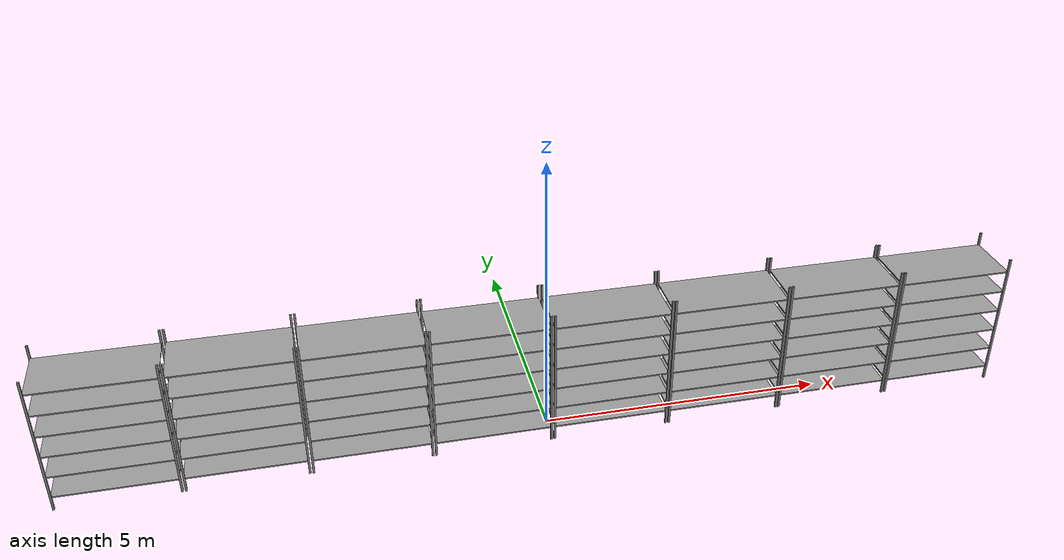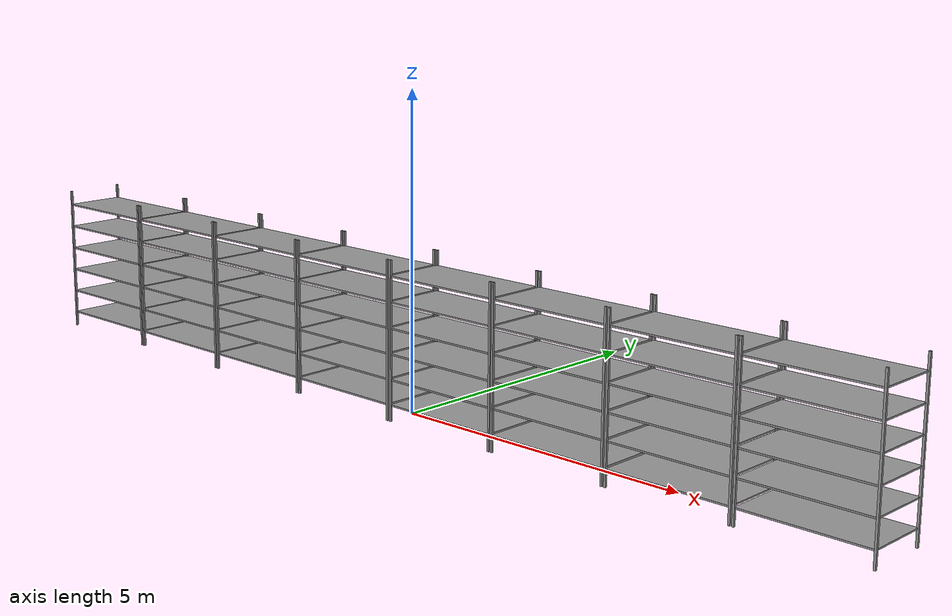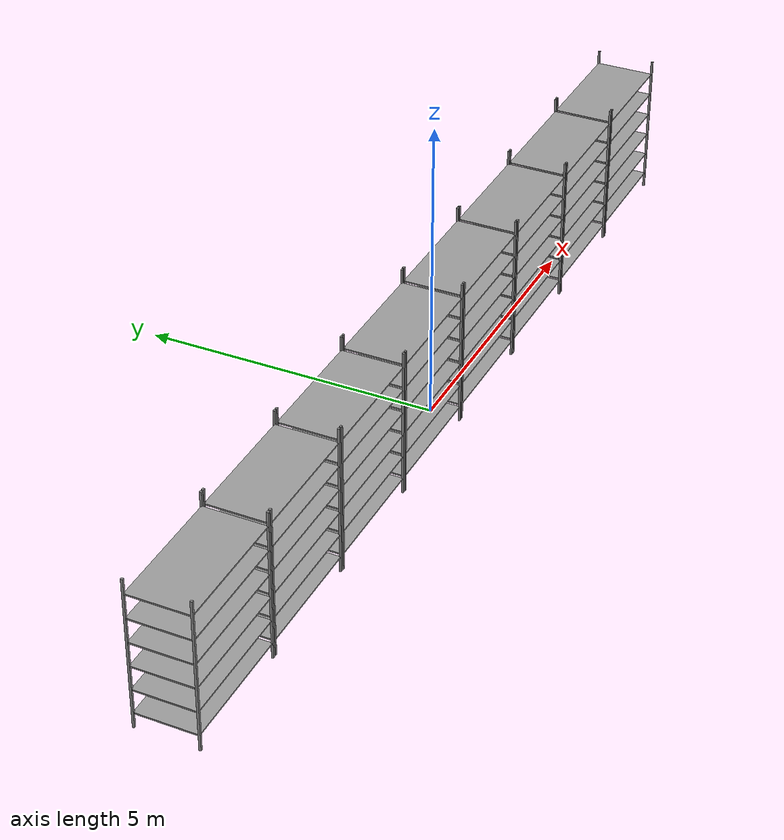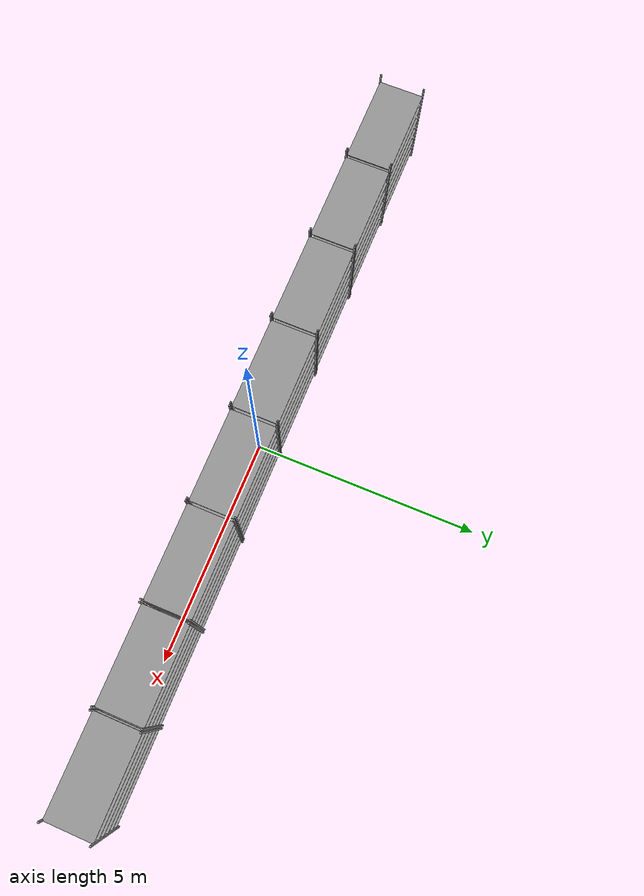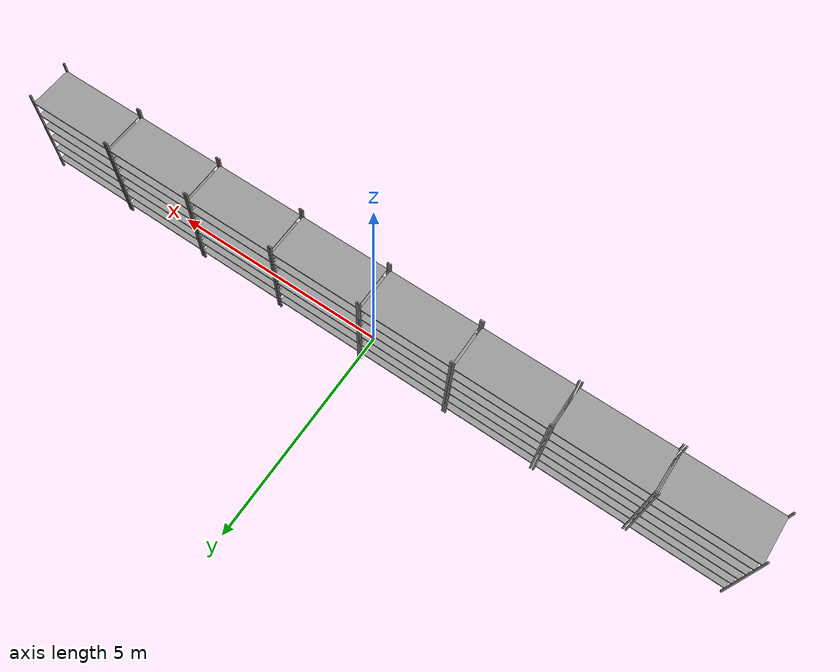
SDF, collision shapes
<?xml version='1.0'?>
<sdf version='1.6'>
  <model name='shelves'>
    <model name='shelf'>
      <link name='link_1'>
        <inertial>
          <mass>1</mass>
          <inertia>
            <ixx>0.166667</ixx>
            <ixy>0</ixy>
            <ixz>0</ixz>
            <iyy>0.166667</iyy>
            <iyz>0</iyz>
            <izz>0.166667</izz>
          </inertia>
          <pose frame=''>0 0 0 0 -0 0</pose>
        </inertial>
        <pose frame=''>0 0 0 0 -0 0</pose>
        <gravity>1</gravity>
        <self_collide>0</self_collide>
        <kinematic>0</kinematic>
        <enable_wind>0</enable_wind>
        <visual name='ModelPreview_2::link_1::visual_6'>
          <pose frame=''>1 0.5 0 0 -0 0</pose>
          <geometry>
            <mesh>
              <uri>model://shelf/model/2-5mDirek.stl</uri>
              <scale>0.001 0.001 0.001</scale>
            </mesh>
          </geometry>
          <material>
            <lighting>1</lighting>
            <script>
              <uri>file://media/materials/scripts/gazebo.material</uri>
              <name>Gazebo/Grey</name>
            </script>
            <shader type='vertex'>
              <normal_map>__default__</normal_map>
            </shader>
            <ambient>0.3 0.3 0.3 1</ambient>
            <diffuse>0.7 0.7 0.7 1</diffuse>
            <specular>0.01 0.01 0.01 1</specular>
            <emissive>0 0 0 1</emissive>
          </material>
          <transparency>0</transparency>
          <cast_shadows>1</cast_shadows>
        </visual>
        <visual name='ModelPreview_2::link_1::visual_7'>
          <pose frame=''>-1 0.5 0 0 -0 0</pose>
          <geometry>
            <mesh>
              <uri>model://shelf/model/2-5mDirek.stl</uri>
              <scale>0.001 0.001 0.001</scale>
            </mesh>
          </geometry>
          <material>
            <lighting>1</lighting>
            <script>
              <uri>file://media/materials/scripts/gazebo.material</uri>
              <name>Gazebo/Grey</name>
            </script>
            <shader type='vertex'>
              <normal_map>__default__</normal_map>
            </shader>
            <ambient>0.3 0.3 0.3 1</ambient>
            <diffuse>0.7 0.7 0.7 1</diffuse>
            <specular>0.01 0.01 0.01 1</specular>
            <emissive>0 0 0 1</emissive>
          </material>
          <transparency>0</transparency>
          <cast_shadows>1</cast_shadows>
        </visual>
        <visual name='ModelPreview_2::link_1::visual_4'>
          <pose frame=''>0 0 1.85 0 -0 0</pose>
          <geometry>
            <box>
              <size>2 1 0.025</size>
            </box>
          </geometry>
          <material>
            <lighting>1</lighting>
            <script>
              <uri>file://media/materials/scripts/gazebo.material</uri>
              <name>Gazebo/WoodFloor</name>
            </script>
            <shader type='vertex'>
              <normal_map>__default__</normal_map>
            </shader>
            <ambient>0.3 0.3 0.3 1</ambient>
            <diffuse>0.7 0.7 0.7 1</diffuse>
            <specular>0.01 0.01 0.01 1</specular>
            <emissive>0 0 0 1</emissive>
          </material>
          <transparency>0</transparency>
          <cast_shadows>1</cast_shadows>
        </visual>
        <visual name='ModelPreview_2::link_1::visual_5'>
          <pose frame=''>0 0 2.25 0 -0 0</pose>
          <geometry>
            <box>
              <size>2 1 0.025</size>
            </box>
          </geometry>
          <material>
            <lighting>1</lighting>
            <script>
              <uri>file://media/materials/scripts/gazebo.material</uri>
              <name>Gazebo/WoodFloor</name>
            </script>
            <shader type='vertex'>
              <normal_map>__default__</normal_map>
            </shader>
            <ambient>0.3 0.3 0.3 1</ambient>
            <diffuse>0.7 0.7 0.7 1</diffuse>
            <specular>0.01 0.01 0.01 1</specular>
            <emissive>0 0 0 1</emissive>
          </material>
          <transparency>0</transparency>
          <cast_shadows>1</cast_shadows>
        </visual>
        <visual name='ModelPreview_2::link_1::visual_3'>
          <pose frame=''>0 0 1.45 0 -0 0</pose>
          <geometry>
            <box>
              <size>2 1 0.025</size>
            </box>
          </geometry>
          <material>
            <lighting>1</lighting>
            <script>
              <uri>file://media/materials/scripts/gazebo.material</uri>
              <name>Gazebo/WoodFloor</name>
            </script>
            <shader type='vertex'>
              <normal_map>__default__</normal_map>
            </shader>
            <ambient>0.3 0.3 0.3 1</ambient>
            <diffuse>0.7 0.7 0.7 1</diffuse>
            <specular>0.01 0.01 0.01 1</specular>
            <emissive>0 0 0 1</emissive>
          </material>
          <transparency>0</transparency>
          <cast_shadows>1</cast_shadows>
        </visual>
        <visual name='ModelPreview_2::link_1::visual_1'>
          <pose frame=''>0 0 0.65 0 -0 0</pose>
          <geometry>
            <box>
              <size>2 1 0.025</size>
            </box>
          </geometry>
          <material>
            <lighting>1</lighting>
            <script>
              <uri>file://media/materials/scripts/gazebo.material</uri>
              <name>Gazebo/WoodFloor</name>
            </script>
            <shader type='vertex'>
              <normal_map>__default__</normal_map>
            </shader>
            <ambient>0.3 0.3 0.3 1</ambient>
            <diffuse>0.7 0.7 0.7 1</diffuse>
            <specular>0.01 0.01 0.01 1</specular>
            <emissive>0 0 0 1</emissive>
          </material>
          <transparency>0</transparency>
          <cast_shadows>1</cast_shadows>
        </visual>
        <visual name='visual'>
          <pose frame=''>0 0 0.25 0 -0 0</pose>
          <geometry>
            <box>
              <size>2 1 0.025</size>
            </box>
          </geometry>
          <material>
            <lighting>1</lighting>
            <script>
              <uri>file://media/materials/scripts/gazebo.material</uri>
              <name>Gazebo/WoodFloor</name>
            </script>
            <shader type='vertex'>
              <normal_map>__default__</normal_map>
            </shader>
            <ambient>0.3 0.3 0.3 1</ambient>
            <diffuse>0.7 0.7 0.7 1</diffuse>
            <specular>0.01 0.01 0.01 1</specular>
            <emissive>0 0 0 1</emissive>
          </material>
          <transparency>0</transparency>
          <cast_shadows>1</cast_shadows>
        </visual>
        <visual name='ModelPreview_2::link_1::visual_2'>
          <pose frame=''>0 0 1.05 0 -0 0</pose>
          <geometry>
            <box>
              <size>2 1 0.025</size>
            </box>
          </geometry>
          <material>
            <lighting>1</lighting>
            <script>
              <uri>file://media/materials/scripts/gazebo.material</uri>
              <name>Gazebo/WoodFloor</name>
            </script>
            <shader type='vertex'>
              <normal_map>__default__</normal_map>
            </shader>
            <ambient>0.3 0.3 0.3 1</ambient>
            <diffuse>0.7 0.7 0.7 1</diffuse>
            <specular>0.01 0.01 0.01 1</specular>
            <emissive>0 0 0 1</emissive>
          </material>
          <transparency>0</transparency>
          <cast_shadows>1</cast_shadows>
        </visual>
        <visual name='ModelPreview_2::link_1::visual_8'>
          <pose frame=''>1 -0.5 0 0 -0 0</pose>
          <geometry>
            <mesh>
              <uri>model://shelf/model/2-5mDirek.stl</uri>
              <scale>0.001 0.001 0.001</scale>
            </mesh>
          </geometry>
          <material>
            <lighting>1</lighting>
            <script>
              <uri>file://media/materials/scripts/gazebo.material</uri>
              <name>Gazebo/Grey</name>
            </script>
            <shader type='vertex'>
              <normal_map>__default__</normal_map>
            </shader>
            <ambient>0.3 0.3 0.3 1</ambient>
            <diffuse>0.7 0.7 0.7 1</diffuse>
            <specular>0.01 0.01 0.01 1</specular>
            <emissive>0 0 0 1</emissive>
          </material>
          <transparency>0</transparency>
          <cast_shadows>1</cast_shadows>
        </visual>
        <visual name='ModelPreview_2::link_1::visual_9'>
          <pose frame=''>-1 -0.5 0 0 -0 0</pose>
          <geometry>
            <mesh>
              <uri>model://shelf/model/2-5mDirek.stl</uri>
              <scale>0.001 0.001 0.001</scale>
            </mesh>
          </geometry>
          <material>
            <lighting>1</lighting>
            <script>
              <uri>file://media/materials/scripts/gazebo.material</uri>
              <name>Gazebo/Grey</name>
            </script>
            <shader type='vertex'>
              <normal_map>__default__</normal_map>
            </shader>
            <ambient>0.3 0.3 0.3 1</ambient>
            <diffuse>0.7 0.7 0.7 1</diffuse>
            <specular>0.01 0.01 0.01 1</specular>
            <emissive>0 0 0 1</emissive>
          </material>
          <transparency>0</transparency>
          <cast_shadows>1</cast_shadows>
        </visual>
        <collision name='collision_7'>
          <laser_retro>0</laser_retro>
          <max_contacts>10</max_contacts>
          <pose frame=''>1 -0.5 1.25 0 -0 0</pose>
          <geometry>
            <box>
              <size>0.035 0.035 2.5</size>
            </box>
          </geometry>
          <surface>
            <friction>
              <ode>
                <mu>1</mu>
                <mu2>1</mu2>
                <fdir1>0 0 0</fdir1>
                <slip1>0</slip1>
                <slip2>0</slip2>
              </ode>
              <torsional>
                <coefficient>1</coefficient>
                <patch_radius>0</patch_radius>
                <surface_radius>0</surface_radius>
                <use_patch_radius>1</use_patch_radius>
                <ode>
                  <slip>0</slip>
                </ode>
              </torsional>
            </friction>
            <bounce>
              <restitution_coefficient>0</restitution_coefficient>
              <threshold>1e+06</threshold>
            </bounce>
            <contact>
              <collide_without_contact>0</collide_without_contact>
              <collide_without_contact_bitmask>1</collide_without_contact_bitmask>
              <collide_bitmask>1</collide_bitmask>
              <ode>
                <soft_cfm>0</soft_cfm>
                <soft_erp>0.2</soft_erp>
                <kp>1e+13</kp>
                <kd>1</kd>
                <max_vel>0.01</max_vel>
                <min_depth>0</min_depth>
              </ode>
              <bullet>
                <split_impulse>1</split_impulse>
                <split_impulse_penetration_threshold>-0.01</split_impulse_penetration_threshold>
                <soft_cfm>0</soft_cfm>
                <soft_erp>0.2</soft_erp>
                <kp>1e+13</kp>
                <kd>1</kd>
              </bullet>
            </contact>
          </surface>
        </collision>
        <collision name='collision_6'>
          <laser_retro>0</laser_retro>
          <max_contacts>10</max_contacts>
          <pose frame=''>1 0.5 1.25 0 -0 0</pose>
          <geometry>
            <box>
              <size>0.035 0.035 2.5</size>
            </box>
          </geometry>
          <surface>
            <friction>
              <ode>
                <mu>1</mu>
                <mu2>1</mu2>
                <fdir1>0 0 0</fdir1>
                <slip1>0</slip1>
                <slip2>0</slip2>
              </ode>
              <torsional>
                <coefficient>1</coefficient>
                <patch_radius>0</patch_radius>
                <surface_radius>0</surface_radius>
                <use_patch_radius>1</use_patch_radius>
                <ode>
                  <slip>0</slip>
                </ode>
              </torsional>
            </friction>
            <bounce>
              <restitution_coefficient>0</restitution_coefficient>
              <threshold>1e+06</threshold>
            </bounce>
            <contact>
              <collide_without_contact>0</collide_without_contact>
              <collide_without_contact_bitmask>1</collide_without_contact_bitmask>
              <collide_bitmask>1</collide_bitmask>
              <ode>
                <soft_cfm>0</soft_cfm>
                <soft_erp>0.2</soft_erp>
                <kp>1e+13</kp>
                <kd>1</kd>
                <max_vel>0.01</max_vel>
                <min_depth>0</min_depth>
              </ode>
              <bullet>
                <split_impulse>1</split_impulse>
                <split_impulse_penetration_threshold>-0.01</split_impulse_penetration_threshold>
                <soft_cfm>0</soft_cfm>
                <soft_erp>0.2</soft_erp>
                <kp>1e+13</kp>
                <kd>1</kd>
              </bullet>
            </contact>
          </surface>
        </collision>
        <collision name='collision_2'>
          <laser_retro>0</laser_retro>
          <max_contacts>10</max_contacts>
          <pose frame=''>0 0 1.05 0 -0 0</pose>
          <geometry>
            <box>
              <size>2 1 0.025</size>
            </box>
          </geometry>
          <surface>
            <friction>
              <ode>
                <mu>1</mu>
                <mu2>1</mu2>
                <fdir1>0 0 0</fdir1>
                <slip1>0</slip1>
                <slip2>0</slip2>
              </ode>
              <torsional>
                <coefficient>1</coefficient>
                <patch_radius>0</patch_radius>
                <surface_radius>0</surface_radius>
                <use_patch_radius>1</use_patch_radius>
                <ode>
                  <slip>0</slip>
                </ode>
              </torsional>
            </friction>
            <bounce>
              <restitution_coefficient>0</restitution_coefficient>
              <threshold>1e+06</threshold>
            </bounce>
            <contact>
              <collide_without_contact>0</collide_without_contact>
              <collide_without_contact_bitmask>1</collide_without_contact_bitmask>
              <collide_bitmask>1</collide_bitmask>
              <ode>
                <soft_cfm>0</soft_cfm>
                <soft_erp>0.2</soft_erp>
                <kp>1e+13</kp>
                <kd>1</kd>
                <max_vel>0.01</max_vel>
                <min_depth>0</min_depth>
              </ode>
              <bullet>
                <split_impulse>1</split_impulse>
                <split_impulse_penetration_threshold>-0.01</split_impulse_penetration_threshold>
                <soft_cfm>0</soft_cfm>
                <soft_erp>0.2</soft_erp>
                <kp>1e+13</kp>
                <kd>1</kd>
              </bullet>
            </contact>
          </surface>
        </collision>
        <collision name='collision_8'>
          <laser_retro>0</laser_retro>
          <max_contacts>10</max_contacts>
          <pose frame=''>-1 0.5 1.25 0 -0 0</pose>
          <geometry>
            <box>
              <size>0.035 0.035 2.5</size>
            </box>
          </geometry>
          <surface>
            <friction>
              <ode>
                <mu>1</mu>
                <mu2>1</mu2>
                <fdir1>0 0 0</fdir1>
                <slip1>0</slip1>
                <slip2>0</slip2>
              </ode>
              <torsional>
                <coefficient>1</coefficient>
                <patch_radius>0</patch_radius>
                <surface_radius>0</surface_radius>
                <use_patch_radius>1</use_patch_radius>
                <ode>
                  <slip>0</slip>
                </ode>
              </torsional>
            </friction>
            <bounce>
              <restitution_coefficient>0</restitution_coefficient>
              <threshold>1e+06</threshold>
            </bounce>
            <contact>
              <collide_without_contact>0</collide_without_contact>
              <collide_without_contact_bitmask>1</collide_without_contact_bitmask>
              <collide_bitmask>1</collide_bitmask>
              <ode>
                <soft_cfm>0</soft_cfm>
                <soft_erp>0.2</soft_erp>
                <kp>1e+13</kp>
                <kd>1</kd>
                <max_vel>0.01</max_vel>
                <min_depth>0</min_depth>
              </ode>
              <bullet>
                <split_impulse>1</split_impulse>
                <split_impulse_penetration_threshold>-0.01</split_impulse_penetration_threshold>
                <soft_cfm>0</soft_cfm>
                <soft_erp>0.2</soft_erp>
                <kp>1e+13</kp>
                <kd>1</kd>
              </bullet>
            </contact>
          </surface>
        </collision>
        <collision name='collision_4'>
          <laser_retro>0</laser_retro>
          <max_contacts>10</max_contacts>
          <pose frame=''>0 0 1.85 0 -0 0</pose>
          <geometry>
            <box>
              <size>2 1 0.025</size>
            </box>
          </geometry>
          <surface>
            <friction>
              <ode>
                <mu>1</mu>
                <mu2>1</mu2>
                <fdir1>0 0 0</fdir1>
                <slip1>0</slip1>
                <slip2>0</slip2>
              </ode>
              <torsional>
                <coefficient>1</coefficient>
                <patch_radius>0</patch_radius>
                <surface_radius>0</surface_radius>
                <use_patch_radius>1</use_patch_radius>
                <ode>
                  <slip>0</slip>
                </ode>
              </torsional>
            </friction>
            <bounce>
              <restitution_coefficient>0</restitution_coefficient>
              <threshold>1e+06</threshold>
            </bounce>
            <contact>
              <collide_without_contact>0</collide_without_contact>
              <collide_without_contact_bitmask>1</collide_without_contact_bitmask>
              <collide_bitmask>1</collide_bitmask>
              <ode>
                <soft_cfm>0</soft_cfm>
                <soft_erp>0.2</soft_erp>
                <kp>1e+13</kp>
                <kd>1</kd>
                <max_vel>0.01</max_vel>
                <min_depth>0</min_depth>
              </ode>
              <bullet>
                <split_impulse>1</split_impulse>
                <split_impulse_penetration_threshold>-0.01</split_impulse_penetration_threshold>
                <soft_cfm>0</soft_cfm>
                <soft_erp>0.2</soft_erp>
                <kp>1e+13</kp>
                <kd>1</kd>
              </bullet>
            </contact>
          </surface>
        </collision>
        <collision name='collision_1'>
          <laser_retro>0</laser_retro>
          <max_contacts>10</max_contacts>
          <pose frame=''>0 0 0.65 0 -0 0</pose>
          <geometry>
            <box>
              <size>2 1 0.025</size>
            </box>
          </geometry>
          <surface>
            <friction>
              <ode>
                <mu>1</mu>
                <mu2>1</mu2>
                <fdir1>0 0 0</fdir1>
                <slip1>0</slip1>
                <slip2>0</slip2>
              </ode>
              <torsional>
                <coefficient>1</coefficient>
                <patch_radius>0</patch_radius>
                <surface_radius>0</surface_radius>
                <use_patch_radius>1</use_patch_radius>
                <ode>
                  <slip>0</slip>
                </ode>
              </torsional>
            </friction>
            <bounce>
              <restitution_coefficient>0</restitution_coefficient>
              <threshold>1e+06</threshold>
            </bounce>
            <contact>
              <collide_without_contact>0</collide_without_contact>
              <collide_without_contact_bitmask>1</collide_without_contact_bitmask>
              <collide_bitmask>1</collide_bitmask>
              <ode>
                <soft_cfm>0</soft_cfm>
                <soft_erp>0.2</soft_erp>
                <kp>1e+13</kp>
                <kd>1</kd>
                <max_vel>0.01</max_vel>
                <min_depth>0</min_depth>
              </ode>
              <bullet>
                <split_impulse>1</split_impulse>
                <split_impulse_penetration_threshold>-0.01</split_impulse_penetration_threshold>
                <soft_cfm>0</soft_cfm>
                <soft_erp>0.2</soft_erp>
                <kp>1e+13</kp>
                <kd>1</kd>
              </bullet>
            </contact>
          </surface>
        </collision>
        <collision name='collision_3'>
          <laser_retro>0</laser_retro>
          <max_contacts>10</max_contacts>
          <pose frame=''>0 0 1.45 0 -0 0</pose>
          <geometry>
            <box>
              <size>2 1 0.025</size>
            </box>
          </geometry>
          <surface>
            <friction>
              <ode>
                <mu>1</mu>
                <mu2>1</mu2>
                <fdir1>0 0 0</fdir1>
                <slip1>0</slip1>
                <slip2>0</slip2>
              </ode>
              <torsional>
                <coefficient>1</coefficient>
                <patch_radius>0</patch_radius>
                <surface_radius>0</surface_radius>
                <use_patch_radius>1</use_patch_radius>
                <ode>
                  <slip>0</slip>
                </ode>
              </torsional>
            </friction>
            <bounce>
              <restitution_coefficient>0</restitution_coefficient>
              <threshold>1e+06</threshold>
            </bounce>
            <contact>
              <collide_without_contact>0</collide_without_contact>
              <collide_without_contact_bitmask>1</collide_without_contact_bitmask>
              <collide_bitmask>1</collide_bitmask>
              <ode>
                <soft_cfm>0</soft_cfm>
                <soft_erp>0.2</soft_erp>
                <kp>1e+13</kp>
                <kd>1</kd>
                <max_vel>0.01</max_vel>
                <min_depth>0</min_depth>
              </ode>
              <bullet>
                <split_impulse>1</split_impulse>
                <split_impulse_penetration_threshold>-0.01</split_impulse_penetration_threshold>
                <soft_cfm>0</soft_cfm>
                <soft_erp>0.2</soft_erp>
                <kp>1e+13</kp>
                <kd>1</kd>
              </bullet>
            </contact>
          </surface>
        </collision>
        <collision name='collision_5'>
          <laser_retro>0</laser_retro>
          <max_contacts>10</max_contacts>
          <pose frame=''>0 0 2.25 0 -0 0</pose>
          <geometry>
            <box>
              <size>2 1 0.025</size>
            </box>
          </geometry>
          <surface>
            <friction>
              <ode>
                <mu>1</mu>
                <mu2>1</mu2>
                <fdir1>0 0 0</fdir1>
                <slip1>0</slip1>
                <slip2>0</slip2>
              </ode>
              <torsional>
                <coefficient>1</coefficient>
                <patch_radius>0</patch_radius>
                <surface_radius>0</surface_radius>
                <use_patch_radius>1</use_patch_radius>
                <ode>
                  <slip>0</slip>
                </ode>
              </torsional>
            </friction>
            <bounce>
              <restitution_coefficient>0</restitution_coefficient>
              <threshold>1e+06</threshold>
            </bounce>
            <contact>
              <collide_without_contact>0</collide_without_contact>
              <collide_without_contact_bitmask>1</collide_without_contact_bitmask>
              <collide_bitmask>1</collide_bitmask>
              <ode>
                <soft_cfm>0</soft_cfm>
                <soft_erp>0.2</soft_erp>
                <kp>1e+13</kp>
                <kd>1</kd>
                <max_vel>0.01</max_vel>
                <min_depth>0</min_depth>
              </ode>
              <bullet>
                <split_impulse>1</split_impulse>
                <split_impulse_penetration_threshold>-0.01</split_impulse_penetration_threshold>
                <soft_cfm>0</soft_cfm>
                <soft_erp>0.2</soft_erp>
                <kp>1e+13</kp>
                <kd>1</kd>
              </bullet>
            </contact>
          </surface>
        </collision>
        <collision name='collision'>
          <laser_retro>0</laser_retro>
          <max_contacts>10</max_contacts>
          <pose frame=''>0 0 0.25 0 -0 0</pose>
          <geometry>
            <box>
              <size>2 1 0.025</size>
            </box>
          </geometry>
          <surface>
            <friction>
              <ode>
                <mu>1</mu>
                <mu2>1</mu2>
                <fdir1>0 0 0</fdir1>
                <slip1>0</slip1>
                <slip2>0</slip2>
              </ode>
              <torsional>
                <coefficient>1</coefficient>
                <patch_radius>0</patch_radius>
                <surface_radius>0</surface_radius>
                <use_patch_radius>1</use_patch_radius>
                <ode>
                  <slip>0</slip>
                </ode>
              </torsional>
            </friction>
            <bounce>
              <restitution_coefficient>0</restitution_coefficient>
              <threshold>1e+06</threshold>
            </bounce>
            <contact>
              <collide_without_contact>0</collide_without_contact>
              <collide_without_contact_bitmask>1</collide_without_contact_bitmask>
              <collide_bitmask>1</collide_bitmask>
              <ode>
                <soft_cfm>0</soft_cfm>
                <soft_erp>0.2</soft_erp>
                <kp>1e+13</kp>
                <kd>1</kd>
                <max_vel>0.01</max_vel>
                <min_depth>0</min_depth>
              </ode>
              <bullet>
                <split_impulse>1</split_impulse>
                <split_impulse_penetration_threshold>-0.01</split_impulse_penetration_threshold>
                <soft_cfm>0</soft_cfm>
                <soft_erp>0.2</soft_erp>
                <kp>1e+13</kp>
                <kd>1</kd>
              </bullet>
            </contact>
          </surface>
        </collision>
        <collision name='collision_9'>
          <laser_retro>0</laser_retro>
          <max_contacts>10</max_contacts>
          <pose frame=''>-1 -0.5 1.25 0 -0 0</pose>
          <geometry>
            <box>
              <size>0.035 0.035 2.5</size>
            </box>
          </geometry>
          <surface>
            <friction>
              <ode>
                <mu>1</mu>
                <mu2>1</mu2>
                <fdir1>0 0 0</fdir1>
                <slip1>0</slip1>
                <slip2>0</slip2>
              </ode>
              <torsional>
                <coefficient>1</coefficient>
                <patch_radius>0</patch_radius>
                <surface_radius>0</surface_radius>
                <use_patch_radius>1</use_patch_radius>
                <ode>
                  <slip>0</slip>
                </ode>
              </torsional>
            </friction>
            <bounce>
              <restitution_coefficient>0</restitution_coefficient>
              <threshold>1e+06</threshold>
            </bounce>
            <contact>
              <collide_without_contact>0</collide_without_contact>
              <collide_without_contact_bitmask>1</collide_without_contact_bitmask>
              <collide_bitmask>1</collide_bitmask>
              <ode>
                <soft_cfm>0</soft_cfm>
                <soft_erp>0.2</soft_erp>
                <kp>1e+13</kp>
                <kd>1</kd>
                <max_vel>0.01</max_vel>
                <min_depth>0</min_depth>
              </ode>
              <bullet>
                <split_impulse>1</split_impulse>
                <split_impulse_penetration_threshold>-0.01</split_impulse_penetration_threshold>
                <soft_cfm>0</soft_cfm>
                <soft_erp>0.2</soft_erp>
                <kp>1e+13</kp>
                <kd>1</kd>
              </bullet>
            </contact>
          </surface>
        </collision>
      </link>
      <static>1</static>
      <allow_auto_disable>1</allow_auto_disable>
      <pose frame=''>-1.03015 -0.001875 0 0 -0 0</pose>
    </model>
    <model name='shelf_0'>
      <link name='link_1'>
        <inertial>
          <mass>1</mass>
          <inertia>
            <ixx>0.166667</ixx>
            <ixy>0</ixy>
            <ixz>0</ixz>
            <iyy>0.166667</iyy>
            <iyz>0</iyz>
            <izz>0.166667</izz>
          </inertia>
          <pose frame=''>0 0 0 0 -0 0</pose>
        </inertial>
        <pose frame=''>0 0 0 0 -0 0</pose>
        <gravity>1</gravity>
        <self_collide>0</self_collide>
        <kinematic>0</kinematic>
        <enable_wind>0</enable_wind>
        <visual name='ModelPreview_2::link_1::visual_6'>
          <pose frame=''>1 0.5 0 0 -0 0</pose>
          <geometry>
            <mesh>
              <uri>model://shelf/model/2-5mDirek.stl</uri>
              <scale>0.001 0.001 0.001</scale>
            </mesh>
          </geometry>
          <material>
            <lighting>1</lighting>
            <script>
              <uri>file://media/materials/scripts/gazebo.material</uri>
              <name>Gazebo/Grey</name>
            </script>
            <shader type='vertex'>
              <normal_map>__default__</normal_map>
            </shader>
            <ambient>0.3 0.3 0.3 1</ambient>
            <diffuse>0.7 0.7 0.7 1</diffuse>
            <specular>0.01 0.01 0.01 1</specular>
            <emissive>0 0 0 1</emissive>
          </material>
          <transparency>0</transparency>
          <cast_shadows>1</cast_shadows>
        </visual>
        <visual name='ModelPreview_2::link_1::visual_7'>
          <pose frame=''>-1 0.5 0 0 -0 0</pose>
          <geometry>
            <mesh>
              <uri>model://shelf/model/2-5mDirek.stl</uri>
              <scale>0.001 0.001 0.001</scale>
            </mesh>
          </geometry>
          <material>
            <lighting>1</lighting>
            <script>
              <uri>file://media/materials/scripts/gazebo.material</uri>
              <name>Gazebo/Grey</name>
            </script>
            <shader type='vertex'>
              <normal_map>__default__</normal_map>
            </shader>
            <ambient>0.3 0.3 0.3 1</ambient>
            <diffuse>0.7 0.7 0.7 1</diffuse>
            <specular>0.01 0.01 0.01 1</specular>
            <emissive>0 0 0 1</emissive>
          </material>
          <transparency>0</transparency>
          <cast_shadows>1</cast_shadows>
        </visual>
        <visual name='ModelPreview_2::link_1::visual_4'>
          <pose frame=''>0 0 1.85 0 -0 0</pose>
          <geometry>
            <box>
              <size>2 1 0.025</size>
            </box>
          </geometry>
          <material>
            <lighting>1</lighting>
            <script>
              <uri>file://media/materials/scripts/gazebo.material</uri>
              <name>Gazebo/WoodFloor</name>
            </script>
            <shader type='vertex'>
              <normal_map>__default__</normal_map>
            </shader>
            <ambient>0.3 0.3 0.3 1</ambient>
            <diffuse>0.7 0.7 0.7 1</diffuse>
            <specular>0.01 0.01 0.01 1</specular>
            <emissive>0 0 0 1</emissive>
          </material>
          <transparency>0</transparency>
          <cast_shadows>1</cast_shadows>
        </visual>
        <visual name='ModelPreview_2::link_1::visual_5'>
          <pose frame=''>0 0 2.25 0 -0 0</pose>
          <geometry>
            <box>
              <size>2 1 0.025</size>
            </box>
          </geometry>
          <material>
            <lighting>1</lighting>
            <script>
              <uri>file://media/materials/scripts/gazebo.material</uri>
              <name>Gazebo/WoodFloor</name>
            </script>
            <shader type='vertex'>
              <normal_map>__default__</normal_map>
            </shader>
            <ambient>0.3 0.3 0.3 1</ambient>
            <diffuse>0.7 0.7 0.7 1</diffuse>
            <specular>0.01 0.01 0.01 1</specular>
            <emissive>0 0 0 1</emissive>
          </material>
          <transparency>0</transparency>
          <cast_shadows>1</cast_shadows>
        </visual>
        <visual name='ModelPreview_2::link_1::visual_3'>
          <pose frame=''>0 0 1.45 0 -0 0</pose>
          <geometry>
            <box>
              <size>2 1 0.025</size>
            </box>
          </geometry>
          <material>
            <lighting>1</lighting>
            <script>
              <uri>file://media/materials/scripts/gazebo.material</uri>
              <name>Gazebo/WoodFloor</name>
            </script>
            <shader type='vertex'>
              <normal_map>__default__</normal_map>
            </shader>
            <ambient>0.3 0.3 0.3 1</ambient>
            <diffuse>0.7 0.7 0.7 1</diffuse>
            <specular>0.01 0.01 0.01 1</specular>
            <emissive>0 0 0 1</emissive>
          </material>
          <transparency>0</transparency>
          <cast_shadows>1</cast_shadows>
        </visual>
        <visual name='ModelPreview_2::link_1::visual_1'>
          <pose frame=''>0 0 0.65 0 -0 0</pose>
          <geometry>
            <box>
              <size>2 1 0.025</size>
            </box>
          </geometry>
          <material>
            <lighting>1</lighting>
            <script>
              <uri>file://media/materials/scripts/gazebo.material</uri>
              <name>Gazebo/WoodFloor</name>
            </script>
            <shader type='vertex'>
              <normal_map>__default__</normal_map>
            </shader>
            <ambient>0.3 0.3 0.3 1</ambient>
            <diffuse>0.7 0.7 0.7 1</diffuse>
            <specular>0.01 0.01 0.01 1</specular>
            <emissive>0 0 0 1</emissive>
          </material>
          <transparency>0</transparency>
          <cast_shadows>1</cast_shadows>
        </visual>
        <visual name='visual'>
          <pose frame=''>0 0 0.25 0 -0 0</pose>
          <geometry>
            <box>
              <size>2 1 0.025</size>
            </box>
          </geometry>
          <material>
            <lighting>1</lighting>
            <script>
              <uri>file://media/materials/scripts/gazebo.material</uri>
              <name>Gazebo/WoodFloor</name>
            </script>
            <shader type='vertex'>
              <normal_map>__default__</normal_map>
            </shader>
            <ambient>0.3 0.3 0.3 1</ambient>
            <diffuse>0.7 0.7 0.7 1</diffuse>
            <specular>0.01 0.01 0.01 1</specular>
            <emissive>0 0 0 1</emissive>
          </material>
          <transparency>0</transparency>
          <cast_shadows>1</cast_shadows>
        </visual>
        <visual name='ModelPreview_2::link_1::visual_2'>
          <pose frame=''>0 0 1.05 0 -0 0</pose>
          <geometry>
            <box>
              <size>2 1 0.025</size>
            </box>
          </geometry>
          <material>
            <lighting>1</lighting>
            <script>
              <uri>file://media/materials/scripts/gazebo.material</uri>
              <name>Gazebo/WoodFloor</name>
            </script>
            <shader type='vertex'>
              <normal_map>__default__</normal_map>
            </shader>
            <ambient>0.3 0.3 0.3 1</ambient>
            <diffuse>0.7 0.7 0.7 1</diffuse>
            <specular>0.01 0.01 0.01 1</specular>
            <emissive>0 0 0 1</emissive>
          </material>
          <transparency>0</transparency>
          <cast_shadows>1</cast_shadows>
        </visual>
        <visual name='ModelPreview_2::link_1::visual_8'>
          <pose frame=''>1 -0.5 0 0 -0 0</pose>
          <geometry>
            <mesh>
              <uri>model://shelf/model/2-5mDirek.stl</uri>
              <scale>0.001 0.001 0.001</scale>
            </mesh>
          </geometry>
          <material>
            <lighting>1</lighting>
            <script>
              <uri>file://media/materials/scripts/gazebo.material</uri>
              <name>Gazebo/Grey</name>
            </script>
            <shader type='vertex'>
              <normal_map>__default__</normal_map>
            </shader>
            <ambient>0.3 0.3 0.3 1</ambient>
            <diffuse>0.7 0.7 0.7 1</diffuse>
            <specular>0.01 0.01 0.01 1</specular>
            <emissive>0 0 0 1</emissive>
          </material>
          <transparency>0</transparency>
          <cast_shadows>1</cast_shadows>
        </visual>
        <visual name='ModelPreview_2::link_1::visual_9'>
          <pose frame=''>-1 -0.5 0 0 -0 0</pose>
          <geometry>
            <mesh>
              <uri>model://shelf/model/2-5mDirek.stl</uri>
              <scale>0.001 0.001 0.001</scale>
            </mesh>
          </geometry>
          <material>
            <lighting>1</lighting>
            <script>
              <uri>file://media/materials/scripts/gazebo.material</uri>
              <name>Gazebo/Grey</name>
            </script>
            <shader type='vertex'>
              <normal_map>__default__</normal_map>
            </shader>
            <ambient>0.3 0.3 0.3 1</ambient>
            <diffuse>0.7 0.7 0.7 1</diffuse>
            <specular>0.01 0.01 0.01 1</specular>
            <emissive>0 0 0 1</emissive>
          </material>
          <transparency>0</transparency>
          <cast_shadows>1</cast_shadows>
        </visual>
        <collision name='collision_7'>
          <laser_retro>0</laser_retro>
          <max_contacts>10</max_contacts>
          <pose frame=''>1 -0.5 1.25 0 -0 0</pose>
          <geometry>
            <box>
              <size>0.035 0.035 2.5</size>
            </box>
          </geometry>
          <surface>
            <friction>
              <ode>
                <mu>1</mu>
                <mu2>1</mu2>
                <fdir1>0 0 0</fdir1>
                <slip1>0</slip1>
                <slip2>0</slip2>
              </ode>
              <torsional>
                <coefficient>1</coefficient>
                <patch_radius>0</patch_radius>
                <surface_radius>0</surface_radius>
                <use_patch_radius>1</use_patch_radius>
                <ode>
                  <slip>0</slip>
                </ode>
              </torsional>
            </friction>
            <bounce>
              <restitution_coefficient>0</restitution_coefficient>
              <threshold>1e+06</threshold>
            </bounce>
            <contact>
              <collide_without_contact>0</collide_without_contact>
              <collide_without_contact_bitmask>1</collide_without_contact_bitmask>
              <collide_bitmask>1</collide_bitmask>
              <ode>
                <soft_cfm>0</soft_cfm>
                <soft_erp>0.2</soft_erp>
                <kp>1e+13</kp>
                <kd>1</kd>
                <max_vel>0.01</max_vel>
                <min_depth>0</min_depth>
              </ode>
              <bullet>
                <split_impulse>1</split_impulse>
                <split_impulse_penetration_threshold>-0.01</split_impulse_penetration_threshold>
                <soft_cfm>0</soft_cfm>
                <soft_erp>0.2</soft_erp>
                <kp>1e+13</kp>
                <kd>1</kd>
              </bullet>
            </contact>
          </surface>
        </collision>
        <collision name='collision_6'>
          <laser_retro>0</laser_retro>
          <max_contacts>10</max_contacts>
          <pose frame=''>1 0.5 1.25 0 -0 0</pose>
          <geometry>
            <box>
              <size>0.035 0.035 2.5</size>
            </box>
          </geometry>
          <surface>
            <friction>
              <ode>
                <mu>1</mu>
                <mu2>1</mu2>
                <fdir1>0 0 0</fdir1>
                <slip1>0</slip1>
                <slip2>0</slip2>
              </ode>
              <torsional>
                <coefficient>1</coefficient>
                <patch_radius>0</patch_radius>
                <surface_radius>0</surface_radius>
                <use_patch_radius>1</use_patch_radius>
                <ode>
                  <slip>0</slip>
                </ode>
              </torsional>
            </friction>
            <bounce>
              <restitution_coefficient>0</restitution_coefficient>
              <threshold>1e+06</threshold>
            </bounce>
            <contact>
              <collide_without_contact>0</collide_without_contact>
              <collide_without_contact_bitmask>1</collide_without_contact_bitmask>
              <collide_bitmask>1</collide_bitmask>
              <ode>
                <soft_cfm>0</soft_cfm>
                <soft_erp>0.2</soft_erp>
                <kp>1e+13</kp>
                <kd>1</kd>
                <max_vel>0.01</max_vel>
                <min_depth>0</min_depth>
              </ode>
              <bullet>
                <split_impulse>1</split_impulse>
                <split_impulse_penetration_threshold>-0.01</split_impulse_penetration_threshold>
                <soft_cfm>0</soft_cfm>
                <soft_erp>0.2</soft_erp>
                <kp>1e+13</kp>
                <kd>1</kd>
              </bullet>
            </contact>
          </surface>
        </collision>
        <collision name='collision_2'>
          <laser_retro>0</laser_retro>
          <max_contacts>10</max_contacts>
          <pose frame=''>0 0 1.05 0 -0 0</pose>
          <geometry>
            <box>
              <size>2 1 0.025</size>
            </box>
          </geometry>
          <surface>
            <friction>
              <ode>
                <mu>1</mu>
                <mu2>1</mu2>
                <fdir1>0 0 0</fdir1>
                <slip1>0</slip1>
                <slip2>0</slip2>
              </ode>
              <torsional>
                <coefficient>1</coefficient>
                <patch_radius>0</patch_radius>
                <surface_radius>0</surface_radius>
                <use_patch_radius>1</use_patch_radius>
                <ode>
                  <slip>0</slip>
                </ode>
              </torsional>
            </friction>
            <bounce>
              <restitution_coefficient>0</restitution_coefficient>
              <threshold>1e+06</threshold>
            </bounce>
            <contact>
              <collide_without_contact>0</collide_without_contact>
              <collide_without_contact_bitmask>1</collide_without_contact_bitmask>
              <collide_bitmask>1</collide_bitmask>
              <ode>
                <soft_cfm>0</soft_cfm>
                <soft_erp>0.2</soft_erp>
                <kp>1e+13</kp>
                <kd>1</kd>
                <max_vel>0.01</max_vel>
                <min_depth>0</min_depth>
              </ode>
              <bullet>
                <split_impulse>1</split_impulse>
                <split_impulse_penetration_threshold>-0.01</split_impulse_penetration_threshold>
                <soft_cfm>0</soft_cfm>
                <soft_erp>0.2</soft_erp>
                <kp>1e+13</kp>
                <kd>1</kd>
              </bullet>
            </contact>
          </surface>
        </collision>
        <collision name='collision_8'>
          <laser_retro>0</laser_retro>
          <max_contacts>10</max_contacts>
          <pose frame=''>-1 0.5 1.25 0 -0 0</pose>
          <geometry>
            <box>
              <size>0.035 0.035 2.5</size>
            </box>
          </geometry>
          <surface>
            <friction>
              <ode>
                <mu>1</mu>
                <mu2>1</mu2>
                <fdir1>0 0 0</fdir1>
                <slip1>0</slip1>
                <slip2>0</slip2>
              </ode>
              <torsional>
                <coefficient>1</coefficient>
                <patch_radius>0</patch_radius>
                <surface_radius>0</surface_radius>
                <use_patch_radius>1</use_patch_radius>
                <ode>
                  <slip>0</slip>
                </ode>
              </torsional>
            </friction>
            <bounce>
              <restitution_coefficient>0</restitution_coefficient>
              <threshold>1e+06</threshold>
            </bounce>
            <contact>
              <collide_without_contact>0</collide_without_contact>
              <collide_without_contact_bitmask>1</collide_without_contact_bitmask>
              <collide_bitmask>1</collide_bitmask>
              <ode>
                <soft_cfm>0</soft_cfm>
                <soft_erp>0.2</soft_erp>
                <kp>1e+13</kp>
                <kd>1</kd>
                <max_vel>0.01</max_vel>
                <min_depth>0</min_depth>
              </ode>
              <bullet>
                <split_impulse>1</split_impulse>
                <split_impulse_penetration_threshold>-0.01</split_impulse_penetration_threshold>
                <soft_cfm>0</soft_cfm>
                <soft_erp>0.2</soft_erp>
                <kp>1e+13</kp>
                <kd>1</kd>
              </bullet>
            </contact>
          </surface>
        </collision>
        <collision name='collision_4'>
          <laser_retro>0</laser_retro>
          <max_contacts>10</max_contacts>
          <pose frame=''>0 0 1.85 0 -0 0</pose>
          <geometry>
            <box>
              <size>2 1 0.025</size>
            </box>
          </geometry>
          <surface>
            <friction>
              <ode>
                <mu>1</mu>
                <mu2>1</mu2>
                <fdir1>0 0 0</fdir1>
                <slip1>0</slip1>
                <slip2>0</slip2>
              </ode>
              <torsional>
                <coefficient>1</coefficient>
                <patch_radius>0</patch_radius>
                <surface_radius>0</surface_radius>
                <use_patch_radius>1</use_patch_radius>
                <ode>
                  <slip>0</slip>
                </ode>
              </torsional>
            </friction>
            <bounce>
              <restitution_coefficient>0</restitution_coefficient>
              <threshold>1e+06</threshold>
            </bounce>
            <contact>
              <collide_without_contact>0</collide_without_contact>
              <collide_without_contact_bitmask>1</collide_without_contact_bitmask>
              <collide_bitmask>1</collide_bitmask>
              <ode>
                <soft_cfm>0</soft_cfm>
                <soft_erp>0.2</soft_erp>
                <kp>1e+13</kp>
                <kd>1</kd>
                <max_vel>0.01</max_vel>
                <min_depth>0</min_depth>
              </ode>
              <bullet>
                <split_impulse>1</split_impulse>
                <split_impulse_penetration_threshold>-0.01</split_impulse_penetration_threshold>
                <soft_cfm>0</soft_cfm>
                <soft_erp>0.2</soft_erp>
                <kp>1e+13</kp>
                <kd>1</kd>
              </bullet>
            </contact>
          </surface>
        </collision>
        <collision name='collision_1'>
          <laser_retro>0</laser_retro>
          <max_contacts>10</max_contacts>
          <pose frame=''>0 0 0.65 0 -0 0</pose>
          <geometry>
            <box>
              <size>2 1 0.025</size>
            </box>
          </geometry>
          <surface>
            <friction>
              <ode>
                <mu>1</mu>
                <mu2>1</mu2>
                <fdir1>0 0 0</fdir1>
                <slip1>0</slip1>
                <slip2>0</slip2>
              </ode>
              <torsional>
                <coefficient>1</coefficient>
                <patch_radius>0</patch_radius>
                <surface_radius>0</surface_radius>
                <use_patch_radius>1</use_patch_radius>
                <ode>
                  <slip>0</slip>
                </ode>
              </torsional>
            </friction>
            <bounce>
              <restitution_coefficient>0</restitution_coefficient>
              <threshold>1e+06</threshold>
            </bounce>
            <contact>
              <collide_without_contact>0</collide_without_contact>
              <collide_without_contact_bitmask>1</collide_without_contact_bitmask>
              <collide_bitmask>1</collide_bitmask>
              <ode>
                <soft_cfm>0</soft_cfm>
                <soft_erp>0.2</soft_erp>
                <kp>1e+13</kp>
                <kd>1</kd>
                <max_vel>0.01</max_vel>
                <min_depth>0</min_depth>
              </ode>
              <bullet>
                <split_impulse>1</split_impulse>
                <split_impulse_penetration_threshold>-0.01</split_impulse_penetration_threshold>
                <soft_cfm>0</soft_cfm>
                <soft_erp>0.2</soft_erp>
                <kp>1e+13</kp>
                <kd>1</kd>
              </bullet>
            </contact>
          </surface>
        </collision>
        <collision name='collision_3'>
          <laser_retro>0</laser_retro>
          <max_contacts>10</max_contacts>
          <pose frame=''>0 0 1.45 0 -0 0</pose>
          <geometry>
            <box>
              <size>2 1 0.025</size>
            </box>
          </geometry>
          <surface>
            <friction>
              <ode>
                <mu>1</mu>
                <mu2>1</mu2>
                <fdir1>0 0 0</fdir1>
                <slip1>0</slip1>
                <slip2>0</slip2>
              </ode>
              <torsional>
                <coefficient>1</coefficient>
                <patch_radius>0</patch_radius>
                <surface_radius>0</surface_radius>
                <use_patch_radius>1</use_patch_radius>
                <ode>
                  <slip>0</slip>
                </ode>
              </torsional>
            </friction>
            <bounce>
              <restitution_coefficient>0</restitution_coefficient>
              <threshold>1e+06</threshold>
            </bounce>
            <contact>
              <collide_without_contact>0</collide_without_contact>
              <collide_without_contact_bitmask>1</collide_without_contact_bitmask>
              <collide_bitmask>1</collide_bitmask>
              <ode>
                <soft_cfm>0</soft_cfm>
                <soft_erp>0.2</soft_erp>
                <kp>1e+13</kp>
                <kd>1</kd>
                <max_vel>0.01</max_vel>
                <min_depth>0</min_depth>
              </ode>
              <bullet>
                <split_impulse>1</split_impulse>
                <split_impulse_penetration_threshold>-0.01</split_impulse_penetration_threshold>
                <soft_cfm>0</soft_cfm>
                <soft_erp>0.2</soft_erp>
                <kp>1e+13</kp>
                <kd>1</kd>
              </bullet>
            </contact>
          </surface>
        </collision>
        <collision name='collision_5'>
          <laser_retro>0</laser_retro>
          <max_contacts>10</max_contacts>
          <pose frame=''>0 0 2.25 0 -0 0</pose>
          <geometry>
            <box>
              <size>2 1 0.025</size>
            </box>
          </geometry>
          <surface>
            <friction>
              <ode>
                <mu>1</mu>
                <mu2>1</mu2>
                <fdir1>0 0 0</fdir1>
                <slip1>0</slip1>
                <slip2>0</slip2>
              </ode>
              <torsional>
                <coefficient>1</coefficient>
                <patch_radius>0</patch_radius>
                <surface_radius>0</surface_radius>
                <use_patch_radius>1</use_patch_radius>
                <ode>
                  <slip>0</slip>
                </ode>
              </torsional>
            </friction>
            <bounce>
              <restitution_coefficient>0</restitution_coefficient>
              <threshold>1e+06</threshold>
            </bounce>
            <contact>
              <collide_without_contact>0</collide_without_contact>
              <collide_without_contact_bitmask>1</collide_without_contact_bitmask>
              <collide_bitmask>1</collide_bitmask>
              <ode>
                <soft_cfm>0</soft_cfm>
                <soft_erp>0.2</soft_erp>
                <kp>1e+13</kp>
                <kd>1</kd>
                <max_vel>0.01</max_vel>
                <min_depth>0</min_depth>
              </ode>
              <bullet>
                <split_impulse>1</split_impulse>
                <split_impulse_penetration_threshold>-0.01</split_impulse_penetration_threshold>
                <soft_cfm>0</soft_cfm>
                <soft_erp>0.2</soft_erp>
                <kp>1e+13</kp>
                <kd>1</kd>
              </bullet>
            </contact>
          </surface>
        </collision>
        <collision name='collision'>
          <laser_retro>0</laser_retro>
          <max_contacts>10</max_contacts>
          <pose frame=''>0 0 0.25 0 -0 0</pose>
          <geometry>
            <box>
              <size>2 1 0.025</size>
            </box>
          </geometry>
          <surface>
            <friction>
              <ode>
                <mu>1</mu>
                <mu2>1</mu2>
                <fdir1>0 0 0</fdir1>
                <slip1>0</slip1>
                <slip2>0</slip2>
              </ode>
              <torsional>
                <coefficient>1</coefficient>
                <patch_radius>0</patch_radius>
                <surface_radius>0</surface_radius>
                <use_patch_radius>1</use_patch_radius>
                <ode>
                  <slip>0</slip>
                </ode>
              </torsional>
            </friction>
            <bounce>
              <restitution_coefficient>0</restitution_coefficient>
              <threshold>1e+06</threshold>
            </bounce>
            <contact>
              <collide_without_contact>0</collide_without_contact>
              <collide_without_contact_bitmask>1</collide_without_contact_bitmask>
              <collide_bitmask>1</collide_bitmask>
              <ode>
                <soft_cfm>0</soft_cfm>
                <soft_erp>0.2</soft_erp>
                <kp>1e+13</kp>
                <kd>1</kd>
                <max_vel>0.01</max_vel>
                <min_depth>0</min_depth>
              </ode>
              <bullet>
                <split_impulse>1</split_impulse>
                <split_impulse_penetration_threshold>-0.01</split_impulse_penetration_threshold>
                <soft_cfm>0</soft_cfm>
                <soft_erp>0.2</soft_erp>
                <kp>1e+13</kp>
                <kd>1</kd>
              </bullet>
            </contact>
          </surface>
        </collision>
        <collision name='collision_9'>
          <laser_retro>0</laser_retro>
          <max_contacts>10</max_contacts>
          <pose frame=''>-1 -0.5 1.25 0 -0 0</pose>
          <geometry>
            <box>
              <size>0.035 0.035 2.5</size>
            </box>
          </geometry>
          <surface>
            <friction>
              <ode>
                <mu>1</mu>
                <mu2>1</mu2>
                <fdir1>0 0 0</fdir1>
                <slip1>0</slip1>
                <slip2>0</slip2>
              </ode>
              <torsional>
                <coefficient>1</coefficient>
                <patch_radius>0</patch_radius>
                <surface_radius>0</surface_radius>
                <use_patch_radius>1</use_patch_radius>
                <ode>
                  <slip>0</slip>
                </ode>
              </torsional>
            </friction>
            <bounce>
              <restitution_coefficient>0</restitution_coefficient>
              <threshold>1e+06</threshold>
            </bounce>
            <contact>
              <collide_without_contact>0</collide_without_contact>
              <collide_without_contact_bitmask>1</collide_without_contact_bitmask>
              <collide_bitmask>1</collide_bitmask>
              <ode>
                <soft_cfm>0</soft_cfm>
                <soft_erp>0.2</soft_erp>
                <kp>1e+13</kp>
                <kd>1</kd>
                <max_vel>0.01</max_vel>
                <min_depth>0</min_depth>
              </ode>
              <bullet>
                <split_impulse>1</split_impulse>
                <split_impulse_penetration_threshold>-0.01</split_impulse_penetration_threshold>
                <soft_cfm>0</soft_cfm>
                <soft_erp>0.2</soft_erp>
                <kp>1e+13</kp>
                <kd>1</kd>
              </bullet>
            </contact>
          </surface>
        </collision>
      </link>
      <static>1</static>
      <allow_auto_disable>1</allow_auto_disable>
      <pose frame=''>-3.09011 -0.000869 0 0 -0 0</pose>
    </model>
    <model name='shelf_1'>
      <link name='link_1'>
        <inertial>
          <mass>1</mass>
          <inertia>
            <ixx>0.166667</ixx>
            <ixy>0</ixy>
            <ixz>0</ixz>
            <iyy>0.166667</iyy>
            <iyz>0</iyz>
            <izz>0.166667</izz>
          </inertia>
          <pose frame=''>0 0 0 0 -0 0</pose>
        </inertial>
        <pose frame=''>0 0 0 0 -0 0</pose>
        <gravity>1</gravity>
        <self_collide>0</self_collide>
        <kinematic>0</kinematic>
        <enable_wind>0</enable_wind>
        <visual name='ModelPreview_2::link_1::visual_6'>
          <pose frame=''>1 0.5 0 0 -0 0</pose>
          <geometry>
            <mesh>
              <uri>model://shelf/model/2-5mDirek.stl</uri>
              <scale>0.001 0.001 0.001</scale>
            </mesh>
          </geometry>
          <material>
            <lighting>1</lighting>
            <script>
              <uri>file://media/materials/scripts/gazebo.material</uri>
              <name>Gazebo/Grey</name>
            </script>
            <shader type='vertex'>
              <normal_map>__default__</normal_map>
            </shader>
            <ambient>0.3 0.3 0.3 1</ambient>
            <diffuse>0.7 0.7 0.7 1</diffuse>
            <specular>0.01 0.01 0.01 1</specular>
            <emissive>0 0 0 1</emissive>
          </material>
          <transparency>0</transparency>
          <cast_shadows>1</cast_shadows>
        </visual>
        <visual name='ModelPreview_2::link_1::visual_7'>
          <pose frame=''>-1 0.5 0 0 -0 0</pose>
          <geometry>
            <mesh>
              <uri>model://shelf/model/2-5mDirek.stl</uri>
              <scale>0.001 0.001 0.001</scale>
            </mesh>
          </geometry>
          <material>
            <lighting>1</lighting>
            <script>
              <uri>file://media/materials/scripts/gazebo.material</uri>
              <name>Gazebo/Grey</name>
            </script>
            <shader type='vertex'>
              <normal_map>__default__</normal_map>
            </shader>
            <ambient>0.3 0.3 0.3 1</ambient>
            <diffuse>0.7 0.7 0.7 1</diffuse>
            <specular>0.01 0.01 0.01 1</specular>
            <emissive>0 0 0 1</emissive>
          </material>
          <transparency>0</transparency>
          <cast_shadows>1</cast_shadows>
        </visual>
        <visual name='ModelPreview_2::link_1::visual_4'>
          <pose frame=''>0 0 1.85 0 -0 0</pose>
          <geometry>
            <box>
              <size>2 1 0.025</size>
            </box>
          </geometry>
          <material>
            <lighting>1</lighting>
            <script>
              <uri>file://media/materials/scripts/gazebo.material</uri>
              <name>Gazebo/WoodFloor</name>
            </script>
            <shader type='vertex'>
              <normal_map>__default__</normal_map>
            </shader>
            <ambient>0.3 0.3 0.3 1</ambient>
            <diffuse>0.7 0.7 0.7 1</diffuse>
            <specular>0.01 0.01 0.01 1</specular>
            <emissive>0 0 0 1</emissive>
          </material>
          <transparency>0</transparency>
          <cast_shadows>1</cast_shadows>
        </visual>
        <visual name='ModelPreview_2::link_1::visual_5'>
          <pose frame=''>0 0 2.25 0 -0 0</pose>
          <geometry>
            <box>
              <size>2 1 0.025</size>
            </box>
          </geometry>
          <material>
            <lighting>1</lighting>
            <script>
              <uri>file://media/materials/scripts/gazebo.material</uri>
              <name>Gazebo/WoodFloor</name>
            </script>
            <shader type='vertex'>
              <normal_map>__default__</normal_map>
            </shader>
            <ambient>0.3 0.3 0.3 1</ambient>
            <diffuse>0.7 0.7 0.7 1</diffuse>
            <specular>0.01 0.01 0.01 1</specular>
            <emissive>0 0 0 1</emissive>
          </material>
          <transparency>0</transparency>
          <cast_shadows>1</cast_shadows>
        </visual>
        <visual name='ModelPreview_2::link_1::visual_3'>
          <pose frame=''>0 0 1.45 0 -0 0</pose>
          <geometry>
            <box>
              <size>2 1 0.025</size>
            </box>
          </geometry>
          <material>
            <lighting>1</lighting>
            <script>
              <uri>file://media/materials/scripts/gazebo.material</uri>
              <name>Gazebo/WoodFloor</name>
            </script>
            <shader type='vertex'>
              <normal_map>__default__</normal_map>
            </shader>
            <ambient>0.3 0.3 0.3 1</ambient>
            <diffuse>0.7 0.7 0.7 1</diffuse>
            <specular>0.01 0.01 0.01 1</specular>
            <emissive>0 0 0 1</emissive>
          </material>
          <transparency>0</transparency>
          <cast_shadows>1</cast_shadows>
        </visual>
        <visual name='ModelPreview_2::link_1::visual_1'>
          <pose frame=''>0 0 0.65 0 -0 0</pose>
          <geometry>
            <box>
              <size>2 1 0.025</size>
            </box>
          </geometry>
          <material>
            <lighting>1</lighting>
            <script>
              <uri>file://media/materials/scripts/gazebo.material</uri>
              <name>Gazebo/WoodFloor</name>
            </script>
            <shader type='vertex'>
              <normal_map>__default__</normal_map>
            </shader>
            <ambient>0.3 0.3 0.3 1</ambient>
            <diffuse>0.7 0.7 0.7 1</diffuse>
            <specular>0.01 0.01 0.01 1</specular>
            <emissive>0 0 0 1</emissive>
          </material>
          <transparency>0</transparency>
          <cast_shadows>1</cast_shadows>
        </visual>
        <visual name='visual'>
          <pose frame=''>0 0 0.25 0 -0 0</pose>
          <geometry>
            <box>
              <size>2 1 0.025</size>
            </box>
          </geometry>
          <material>
            <lighting>1</lighting>
            <script>
              <uri>file://media/materials/scripts/gazebo.material</uri>
              <name>Gazebo/WoodFloor</name>
            </script>
            <shader type='vertex'>
              <normal_map>__default__</normal_map>
            </shader>
            <ambient>0.3 0.3 0.3 1</ambient>
            <diffuse>0.7 0.7 0.7 1</diffuse>
            <specular>0.01 0.01 0.01 1</specular>
            <emissive>0 0 0 1</emissive>
          </material>
          <transparency>0</transparency>
          <cast_shadows>1</cast_shadows>
        </visual>
        <visual name='ModelPreview_2::link_1::visual_2'>
          <pose frame=''>0 0 1.05 0 -0 0</pose>
          <geometry>
            <box>
              <size>2 1 0.025</size>
            </box>
          </geometry>
          <material>
            <lighting>1</lighting>
            <script>
              <uri>file://media/materials/scripts/gazebo.material</uri>
              <name>Gazebo/WoodFloor</name>
            </script>
            <shader type='vertex'>
              <normal_map>__default__</normal_map>
            </shader>
            <ambient>0.3 0.3 0.3 1</ambient>
            <diffuse>0.7 0.7 0.7 1</diffuse>
            <specular>0.01 0.01 0.01 1</specular>
            <emissive>0 0 0 1</emissive>
          </material>
          <transparency>0</transparency>
          <cast_shadows>1</cast_shadows>
        </visual>
        <visual name='ModelPreview_2::link_1::visual_8'>
          <pose frame=''>1 -0.5 0 0 -0 0</pose>
          <geometry>
            <mesh>
              <uri>model://shelf/model/2-5mDirek.stl</uri>
              <scale>0.001 0.001 0.001</scale>
            </mesh>
          </geometry>
          <material>
            <lighting>1</lighting>
            <script>
              <uri>file://media/materials/scripts/gazebo.material</uri>
              <name>Gazebo/Grey</name>
            </script>
            <shader type='vertex'>
              <normal_map>__default__</normal_map>
            </shader>
            <ambient>0.3 0.3 0.3 1</ambient>
            <diffuse>0.7 0.7 0.7 1</diffuse>
            <specular>0.01 0.01 0.01 1</specular>
            <emissive>0 0 0 1</emissive>
          </material>
          <transparency>0</transparency>
          <cast_shadows>1</cast_shadows>
        </visual>
        <visual name='ModelPreview_2::link_1::visual_9'>
          <pose frame=''>-1 -0.5 0 0 -0 0</pose>
          <geometry>
            <mesh>
              <uri>model://shelf/model/2-5mDirek.stl</uri>
              <scale>0.001 0.001 0.001</scale>
            </mesh>
          </geometry>
          <material>
            <lighting>1</lighting>
            <script>
              <uri>file://media/materials/scripts/gazebo.material</uri>
              <name>Gazebo/Grey</name>
            </script>
            <shader type='vertex'>
              <normal_map>__default__</normal_map>
            </shader>
            <ambient>0.3 0.3 0.3 1</ambient>
            <diffuse>0.7 0.7 0.7 1</diffuse>
            <specular>0.01 0.01 0.01 1</specular>
            <emissive>0 0 0 1</emissive>
          </material>
          <transparency>0</transparency>
          <cast_shadows>1</cast_shadows>
        </visual>
        <collision name='collision_7'>
          <laser_retro>0</laser_retro>
          <max_contacts>10</max_contacts>
          <pose frame=''>1 -0.5 1.25 0 -0 0</pose>
          <geometry>
            <box>
              <size>0.035 0.035 2.5</size>
            </box>
          </geometry>
          <surface>
            <friction>
              <ode>
                <mu>1</mu>
                <mu2>1</mu2>
                <fdir1>0 0 0</fdir1>
                <slip1>0</slip1>
                <slip2>0</slip2>
              </ode>
              <torsional>
                <coefficient>1</coefficient>
                <patch_radius>0</patch_radius>
                <surface_radius>0</surface_radius>
                <use_patch_radius>1</use_patch_radius>
                <ode>
                  <slip>0</slip>
                </ode>
              </torsional>
            </friction>
            <bounce>
              <restitution_coefficient>0</restitution_coefficient>
              <threshold>1e+06</threshold>
            </bounce>
            <contact>
              <collide_without_contact>0</collide_without_contact>
              <collide_without_contact_bitmask>1</collide_without_contact_bitmask>
              <collide_bitmask>1</collide_bitmask>
              <ode>
                <soft_cfm>0</soft_cfm>
                <soft_erp>0.2</soft_erp>
                <kp>1e+13</kp>
                <kd>1</kd>
                <max_vel>0.01</max_vel>
                <min_depth>0</min_depth>
              </ode>
              <bullet>
                <split_impulse>1</split_impulse>
                <split_impulse_penetration_threshold>-0.01</split_impulse_penetration_threshold>
                <soft_cfm>0</soft_cfm>
                <soft_erp>0.2</soft_erp>
                <kp>1e+13</kp>
                <kd>1</kd>
              </bullet>
            </contact>
          </surface>
        </collision>
        <collision name='collision_6'>
          <laser_retro>0</laser_retro>
          <max_contacts>10</max_contacts>
          <pose frame=''>1 0.5 1.25 0 -0 0</pose>
          <geometry>
            <box>
              <size>0.035 0.035 2.5</size>
            </box>
          </geometry>
          <surface>
            <friction>
              <ode>
                <mu>1</mu>
                <mu2>1</mu2>
                <fdir1>0 0 0</fdir1>
                <slip1>0</slip1>
                <slip2>0</slip2>
              </ode>
              <torsional>
                <coefficient>1</coefficient>
                <patch_radius>0</patch_radius>
                <surface_radius>0</surface_radius>
                <use_patch_radius>1</use_patch_radius>
                <ode>
                  <slip>0</slip>
                </ode>
              </torsional>
            </friction>
            <bounce>
              <restitution_coefficient>0</restitution_coefficient>
              <threshold>1e+06</threshold>
            </bounce>
            <contact>
              <collide_without_contact>0</collide_without_contact>
              <collide_without_contact_bitmask>1</collide_without_contact_bitmask>
              <collide_bitmask>1</collide_bitmask>
              <ode>
                <soft_cfm>0</soft_cfm>
                <soft_erp>0.2</soft_erp>
                <kp>1e+13</kp>
                <kd>1</kd>
                <max_vel>0.01</max_vel>
                <min_depth>0</min_depth>
              </ode>
              <bullet>
                <split_impulse>1</split_impulse>
                <split_impulse_penetration_threshold>-0.01</split_impulse_penetration_threshold>
                <soft_cfm>0</soft_cfm>
                <soft_erp>0.2</soft_erp>
                <kp>1e+13</kp>
                <kd>1</kd>
              </bullet>
            </contact>
          </surface>
        </collision>
        <collision name='collision_2'>
          <laser_retro>0</laser_retro>
          <max_contacts>10</max_contacts>
          <pose frame=''>0 0 1.05 0 -0 0</pose>
          <geometry>
            <box>
              <size>2 1 0.025</size>
            </box>
          </geometry>
          <surface>
            <friction>
              <ode>
                <mu>1</mu>
                <mu2>1</mu2>
                <fdir1>0 0 0</fdir1>
                <slip1>0</slip1>
                <slip2>0</slip2>
              </ode>
              <torsional>
                <coefficient>1</coefficient>
                <patch_radius>0</patch_radius>
                <surface_radius>0</surface_radius>
                <use_patch_radius>1</use_patch_radius>
                <ode>
                  <slip>0</slip>
                </ode>
              </torsional>
            </friction>
            <bounce>
              <restitution_coefficient>0</restitution_coefficient>
              <threshold>1e+06</threshold>
            </bounce>
            <contact>
              <collide_without_contact>0</collide_without_contact>
              <collide_without_contact_bitmask>1</collide_without_contact_bitmask>
              <collide_bitmask>1</collide_bitmask>
              <ode>
                <soft_cfm>0</soft_cfm>
                <soft_erp>0.2</soft_erp>
                <kp>1e+13</kp>
                <kd>1</kd>
                <max_vel>0.01</max_vel>
                <min_depth>0</min_depth>
              </ode>
              <bullet>
                <split_impulse>1</split_impulse>
                <split_impulse_penetration_threshold>-0.01</split_impulse_penetration_threshold>
                <soft_cfm>0</soft_cfm>
                <soft_erp>0.2</soft_erp>
                <kp>1e+13</kp>
                <kd>1</kd>
              </bullet>
            </contact>
          </surface>
        </collision>
        <collision name='collision_8'>
          <laser_retro>0</laser_retro>
          <max_contacts>10</max_contacts>
          <pose frame=''>-1 0.5 1.25 0 -0 0</pose>
          <geometry>
            <box>
              <size>0.035 0.035 2.5</size>
            </box>
          </geometry>
          <surface>
            <friction>
              <ode>
                <mu>1</mu>
                <mu2>1</mu2>
                <fdir1>0 0 0</fdir1>
                <slip1>0</slip1>
                <slip2>0</slip2>
              </ode>
              <torsional>
                <coefficient>1</coefficient>
                <patch_radius>0</patch_radius>
                <surface_radius>0</surface_radius>
                <use_patch_radius>1</use_patch_radius>
                <ode>
                  <slip>0</slip>
                </ode>
              </torsional>
            </friction>
            <bounce>
              <restitution_coefficient>0</restitution_coefficient>
              <threshold>1e+06</threshold>
            </bounce>
            <contact>
              <collide_without_contact>0</collide_without_contact>
              <collide_without_contact_bitmask>1</collide_without_contact_bitmask>
              <collide_bitmask>1</collide_bitmask>
              <ode>
                <soft_cfm>0</soft_cfm>
                <soft_erp>0.2</soft_erp>
                <kp>1e+13</kp>
                <kd>1</kd>
                <max_vel>0.01</max_vel>
                <min_depth>0</min_depth>
              </ode>
              <bullet>
                <split_impulse>1</split_impulse>
                <split_impulse_penetration_threshold>-0.01</split_impulse_penetration_threshold>
                <soft_cfm>0</soft_cfm>
                <soft_erp>0.2</soft_erp>
                <kp>1e+13</kp>
                <kd>1</kd>
              </bullet>
            </contact>
          </surface>
        </collision>
        <collision name='collision_4'>
          <laser_retro>0</laser_retro>
          <max_contacts>10</max_contacts>
          <pose frame=''>0 0 1.85 0 -0 0</pose>
          <geometry>
            <box>
              <size>2 1 0.025</size>
            </box>
          </geometry>
          <surface>
            <friction>
              <ode>
                <mu>1</mu>
                <mu2>1</mu2>
                <fdir1>0 0 0</fdir1>
                <slip1>0</slip1>
                <slip2>0</slip2>
              </ode>
              <torsional>
                <coefficient>1</coefficient>
                <patch_radius>0</patch_radius>
                <surface_radius>0</surface_radius>
                <use_patch_radius>1</use_patch_radius>
                <ode>
                  <slip>0</slip>
                </ode>
              </torsional>
            </friction>
            <bounce>
              <restitution_coefficient>0</restitution_coefficient>
              <threshold>1e+06</threshold>
            </bounce>
            <contact>
              <collide_without_contact>0</collide_without_contact>
              <collide_without_contact_bitmask>1</collide_without_contact_bitmask>
              <collide_bitmask>1</collide_bitmask>
              <ode>
                <soft_cfm>0</soft_cfm>
                <soft_erp>0.2</soft_erp>
                <kp>1e+13</kp>
                <kd>1</kd>
                <max_vel>0.01</max_vel>
                <min_depth>0</min_depth>
              </ode>
              <bullet>
                <split_impulse>1</split_impulse>
                <split_impulse_penetration_threshold>-0.01</split_impulse_penetration_threshold>
                <soft_cfm>0</soft_cfm>
                <soft_erp>0.2</soft_erp>
                <kp>1e+13</kp>
                <kd>1</kd>
              </bullet>
            </contact>
          </surface>
        </collision>
        <collision name='collision_1'>
          <laser_retro>0</laser_retro>
          <max_contacts>10</max_contacts>
          <pose frame=''>0 0 0.65 0 -0 0</pose>
          <geometry>
            <box>
              <size>2 1 0.025</size>
            </box>
          </geometry>
          <surface>
            <friction>
              <ode>
                <mu>1</mu>
                <mu2>1</mu2>
                <fdir1>0 0 0</fdir1>
                <slip1>0</slip1>
                <slip2>0</slip2>
              </ode>
              <torsional>
                <coefficient>1</coefficient>
                <patch_radius>0</patch_radius>
                <surface_radius>0</surface_radius>
                <use_patch_radius>1</use_patch_radius>
                <ode>
                  <slip>0</slip>
                </ode>
              </torsional>
            </friction>
            <bounce>
              <restitution_coefficient>0</restitution_coefficient>
              <threshold>1e+06</threshold>
            </bounce>
            <contact>
              <collide_without_contact>0</collide_without_contact>
              <collide_without_contact_bitmask>1</collide_without_contact_bitmask>
              <collide_bitmask>1</collide_bitmask>
              <ode>
                <soft_cfm>0</soft_cfm>
                <soft_erp>0.2</soft_erp>
                <kp>1e+13</kp>
                <kd>1</kd>
                <max_vel>0.01</max_vel>
                <min_depth>0</min_depth>
              </ode>
              <bullet>
                <split_impulse>1</split_impulse>
                <split_impulse_penetration_threshold>-0.01</split_impulse_penetration_threshold>
                <soft_cfm>0</soft_cfm>
                <soft_erp>0.2</soft_erp>
                <kp>1e+13</kp>
                <kd>1</kd>
              </bullet>
            </contact>
          </surface>
        </collision>
        <collision name='collision_3'>
          <laser_retro>0</laser_retro>
          <max_contacts>10</max_contacts>
          <pose frame=''>0 0 1.45 0 -0 0</pose>
          <geometry>
            <box>
              <size>2 1 0.025</size>
            </box>
          </geometry>
          <surface>
            <friction>
              <ode>
                <mu>1</mu>
                <mu2>1</mu2>
                <fdir1>0 0 0</fdir1>
                <slip1>0</slip1>
                <slip2>0</slip2>
              </ode>
              <torsional>
                <coefficient>1</coefficient>
                <patch_radius>0</patch_radius>
                <surface_radius>0</surface_radius>
                <use_patch_radius>1</use_patch_radius>
                <ode>
                  <slip>0</slip>
                </ode>
              </torsional>
            </friction>
            <bounce>
              <restitution_coefficient>0</restitution_coefficient>
              <threshold>1e+06</threshold>
            </bounce>
            <contact>
              <collide_without_contact>0</collide_without_contact>
              <collide_without_contact_bitmask>1</collide_without_contact_bitmask>
              <collide_bitmask>1</collide_bitmask>
              <ode>
                <soft_cfm>0</soft_cfm>
                <soft_erp>0.2</soft_erp>
                <kp>1e+13</kp>
                <kd>1</kd>
                <max_vel>0.01</max_vel>
                <min_depth>0</min_depth>
              </ode>
              <bullet>
                <split_impulse>1</split_impulse>
                <split_impulse_penetration_threshold>-0.01</split_impulse_penetration_threshold>
                <soft_cfm>0</soft_cfm>
                <soft_erp>0.2</soft_erp>
                <kp>1e+13</kp>
                <kd>1</kd>
              </bullet>
            </contact>
          </surface>
        </collision>
        <collision name='collision_5'>
          <laser_retro>0</laser_retro>
          <max_contacts>10</max_contacts>
          <pose frame=''>0 0 2.25 0 -0 0</pose>
          <geometry>
            <box>
              <size>2 1 0.025</size>
            </box>
          </geometry>
          <surface>
            <friction>
              <ode>
                <mu>1</mu>
                <mu2>1</mu2>
                <fdir1>0 0 0</fdir1>
                <slip1>0</slip1>
                <slip2>0</slip2>
              </ode>
              <torsional>
                <coefficient>1</coefficient>
                <patch_radius>0</patch_radius>
                <surface_radius>0</surface_radius>
                <use_patch_radius>1</use_patch_radius>
                <ode>
                  <slip>0</slip>
                </ode>
              </torsional>
            </friction>
            <bounce>
              <restitution_coefficient>0</restitution_coefficient>
              <threshold>1e+06</threshold>
            </bounce>
            <contact>
              <collide_without_contact>0</collide_without_contact>
              <collide_without_contact_bitmask>1</collide_without_contact_bitmask>
              <collide_bitmask>1</collide_bitmask>
              <ode>
                <soft_cfm>0</soft_cfm>
                <soft_erp>0.2</soft_erp>
                <kp>1e+13</kp>
                <kd>1</kd>
                <max_vel>0.01</max_vel>
                <min_depth>0</min_depth>
              </ode>
              <bullet>
                <split_impulse>1</split_impulse>
                <split_impulse_penetration_threshold>-0.01</split_impulse_penetration_threshold>
                <soft_cfm>0</soft_cfm>
                <soft_erp>0.2</soft_erp>
                <kp>1e+13</kp>
                <kd>1</kd>
              </bullet>
            </contact>
          </surface>
        </collision>
        <collision name='collision'>
          <laser_retro>0</laser_retro>
          <max_contacts>10</max_contacts>
          <pose frame=''>0 0 0.25 0 -0 0</pose>
          <geometry>
            <box>
              <size>2 1 0.025</size>
            </box>
          </geometry>
          <surface>
            <friction>
              <ode>
                <mu>1</mu>
                <mu2>1</mu2>
                <fdir1>0 0 0</fdir1>
                <slip1>0</slip1>
                <slip2>0</slip2>
              </ode>
              <torsional>
                <coefficient>1</coefficient>
                <patch_radius>0</patch_radius>
                <surface_radius>0</surface_radius>
                <use_patch_radius>1</use_patch_radius>
                <ode>
                  <slip>0</slip>
                </ode>
              </torsional>
            </friction>
            <bounce>
              <restitution_coefficient>0</restitution_coefficient>
              <threshold>1e+06</threshold>
            </bounce>
            <contact>
              <collide_without_contact>0</collide_without_contact>
              <collide_without_contact_bitmask>1</collide_without_contact_bitmask>
              <collide_bitmask>1</collide_bitmask>
              <ode>
                <soft_cfm>0</soft_cfm>
                <soft_erp>0.2</soft_erp>
                <kp>1e+13</kp>
                <kd>1</kd>
                <max_vel>0.01</max_vel>
                <min_depth>0</min_depth>
              </ode>
              <bullet>
                <split_impulse>1</split_impulse>
                <split_impulse_penetration_threshold>-0.01</split_impulse_penetration_threshold>
                <soft_cfm>0</soft_cfm>
                <soft_erp>0.2</soft_erp>
                <kp>1e+13</kp>
                <kd>1</kd>
              </bullet>
            </contact>
          </surface>
        </collision>
        <collision name='collision_9'>
          <laser_retro>0</laser_retro>
          <max_contacts>10</max_contacts>
          <pose frame=''>-1 -0.5 1.25 0 -0 0</pose>
          <geometry>
            <box>
              <size>0.035 0.035 2.5</size>
            </box>
          </geometry>
          <surface>
            <friction>
              <ode>
                <mu>1</mu>
                <mu2>1</mu2>
                <fdir1>0 0 0</fdir1>
                <slip1>0</slip1>
                <slip2>0</slip2>
              </ode>
              <torsional>
                <coefficient>1</coefficient>
                <patch_radius>0</patch_radius>
                <surface_radius>0</surface_radius>
                <use_patch_radius>1</use_patch_radius>
                <ode>
                  <slip>0</slip>
                </ode>
              </torsional>
            </friction>
            <bounce>
              <restitution_coefficient>0</restitution_coefficient>
              <threshold>1e+06</threshold>
            </bounce>
            <contact>
              <collide_without_contact>0</collide_without_contact>
              <collide_without_contact_bitmask>1</collide_without_contact_bitmask>
              <collide_bitmask>1</collide_bitmask>
              <ode>
                <soft_cfm>0</soft_cfm>
                <soft_erp>0.2</soft_erp>
                <kp>1e+13</kp>
                <kd>1</kd>
                <max_vel>0.01</max_vel>
                <min_depth>0</min_depth>
              </ode>
              <bullet>
                <split_impulse>1</split_impulse>
                <split_impulse_penetration_threshold>-0.01</split_impulse_penetration_threshold>
                <soft_cfm>0</soft_cfm>
                <soft_erp>0.2</soft_erp>
                <kp>1e+13</kp>
                <kd>1</kd>
              </bullet>
            </contact>
          </surface>
        </collision>
      </link>
      <static>1</static>
      <allow_auto_disable>1</allow_auto_disable>
      <pose frame=''>-5.1519 0.002003 0 0 -0 0</pose>
    </model>
    <model name='shelf_2'>
      <link name='link_1'>
        <inertial>
          <mass>1</mass>
          <inertia>
            <ixx>0.166667</ixx>
            <ixy>0</ixy>
            <ixz>0</ixz>
            <iyy>0.166667</iyy>
            <iyz>0</iyz>
            <izz>0.166667</izz>
          </inertia>
          <pose frame=''>0 0 0 0 -0 0</pose>
        </inertial>
        <pose frame=''>0 0 0 0 -0 0</pose>
        <gravity>1</gravity>
        <self_collide>0</self_collide>
        <kinematic>0</kinematic>
        <enable_wind>0</enable_wind>
        <visual name='ModelPreview_2::link_1::visual_6'>
          <pose frame=''>1 0.5 0 0 -0 0</pose>
          <geometry>
            <mesh>
              <uri>model://shelf/model/2-5mDirek.stl</uri>
              <scale>0.001 0.001 0.001</scale>
            </mesh>
          </geometry>
          <material>
            <lighting>1</lighting>
            <script>
              <uri>file://media/materials/scripts/gazebo.material</uri>
              <name>Gazebo/Grey</name>
            </script>
            <shader type='vertex'>
              <normal_map>__default__</normal_map>
            </shader>
            <ambient>0.3 0.3 0.3 1</ambient>
            <diffuse>0.7 0.7 0.7 1</diffuse>
            <specular>0.01 0.01 0.01 1</specular>
            <emissive>0 0 0 1</emissive>
          </material>
          <transparency>0</transparency>
          <cast_shadows>1</cast_shadows>
        </visual>
        <visual name='ModelPreview_2::link_1::visual_7'>
          <pose frame=''>-1 0.5 0 0 -0 0</pose>
          <geometry>
            <mesh>
              <uri>model://shelf/model/2-5mDirek.stl</uri>
              <scale>0.001 0.001 0.001</scale>
            </mesh>
          </geometry>
          <material>
            <lighting>1</lighting>
            <script>
              <uri>file://media/materials/scripts/gazebo.material</uri>
              <name>Gazebo/Grey</name>
            </script>
            <shader type='vertex'>
              <normal_map>__default__</normal_map>
            </shader>
            <ambient>0.3 0.3 0.3 1</ambient>
            <diffuse>0.7 0.7 0.7 1</diffuse>
            <specular>0.01 0.01 0.01 1</specular>
            <emissive>0 0 0 1</emissive>
          </material>
          <transparency>0</transparency>
          <cast_shadows>1</cast_shadows>
        </visual>
        <visual name='ModelPreview_2::link_1::visual_4'>
          <pose frame=''>0 0 1.85 0 -0 0</pose>
          <geometry>
            <box>
              <size>2 1 0.025</size>
            </box>
          </geometry>
          <material>
            <lighting>1</lighting>
            <script>
              <uri>file://media/materials/scripts/gazebo.material</uri>
              <name>Gazebo/WoodFloor</name>
            </script>
            <shader type='vertex'>
              <normal_map>__default__</normal_map>
            </shader>
            <ambient>0.3 0.3 0.3 1</ambient>
            <diffuse>0.7 0.7 0.7 1</diffuse>
            <specular>0.01 0.01 0.01 1</specular>
            <emissive>0 0 0 1</emissive>
          </material>
          <transparency>0</transparency>
          <cast_shadows>1</cast_shadows>
        </visual>
        <visual name='ModelPreview_2::link_1::visual_5'>
          <pose frame=''>0 0 2.25 0 -0 0</pose>
          <geometry>
            <box>
              <size>2 1 0.025</size>
            </box>
          </geometry>
          <material>
            <lighting>1</lighting>
            <script>
              <uri>file://media/materials/scripts/gazebo.material</uri>
              <name>Gazebo/WoodFloor</name>
            </script>
            <shader type='vertex'>
              <normal_map>__default__</normal_map>
            </shader>
            <ambient>0.3 0.3 0.3 1</ambient>
            <diffuse>0.7 0.7 0.7 1</diffuse>
            <specular>0.01 0.01 0.01 1</specular>
            <emissive>0 0 0 1</emissive>
          </material>
          <transparency>0</transparency>
          <cast_shadows>1</cast_shadows>
        </visual>
        <visual name='ModelPreview_2::link_1::visual_3'>
          <pose frame=''>0 0 1.45 0 -0 0</pose>
          <geometry>
            <box>
              <size>2 1 0.025</size>
            </box>
          </geometry>
          <material>
            <lighting>1</lighting>
            <script>
              <uri>file://media/materials/scripts/gazebo.material</uri>
              <name>Gazebo/WoodFloor</name>
            </script>
            <shader type='vertex'>
              <normal_map>__default__</normal_map>
            </shader>
            <ambient>0.3 0.3 0.3 1</ambient>
            <diffuse>0.7 0.7 0.7 1</diffuse>
            <specular>0.01 0.01 0.01 1</specular>
            <emissive>0 0 0 1</emissive>
          </material>
          <transparency>0</transparency>
          <cast_shadows>1</cast_shadows>
        </visual>
        <visual name='ModelPreview_2::link_1::visual_1'>
          <pose frame=''>0 0 0.65 0 -0 0</pose>
          <geometry>
            <box>
              <size>2 1 0.025</size>
            </box>
          </geometry>
          <material>
            <lighting>1</lighting>
            <script>
              <uri>file://media/materials/scripts/gazebo.material</uri>
              <name>Gazebo/WoodFloor</name>
            </script>
            <shader type='vertex'>
              <normal_map>__default__</normal_map>
            </shader>
            <ambient>0.3 0.3 0.3 1</ambient>
            <diffuse>0.7 0.7 0.7 1</diffuse>
            <specular>0.01 0.01 0.01 1</specular>
            <emissive>0 0 0 1</emissive>
          </material>
          <transparency>0</transparency>
          <cast_shadows>1</cast_shadows>
        </visual>
        <visual name='visual'>
          <pose frame=''>0 0 0.25 0 -0 0</pose>
          <geometry>
            <box>
              <size>2 1 0.025</size>
            </box>
          </geometry>
          <material>
            <lighting>1</lighting>
            <script>
              <uri>file://media/materials/scripts/gazebo.material</uri>
              <name>Gazebo/WoodFloor</name>
            </script>
            <shader type='vertex'>
              <normal_map>__default__</normal_map>
            </shader>
            <ambient>0.3 0.3 0.3 1</ambient>
            <diffuse>0.7 0.7 0.7 1</diffuse>
            <specular>0.01 0.01 0.01 1</specular>
            <emissive>0 0 0 1</emissive>
          </material>
          <transparency>0</transparency>
          <cast_shadows>1</cast_shadows>
        </visual>
        <visual name='ModelPreview_2::link_1::visual_2'>
          <pose frame=''>0 0 1.05 0 -0 0</pose>
          <geometry>
            <box>
              <size>2 1 0.025</size>
            </box>
          </geometry>
          <material>
            <lighting>1</lighting>
            <script>
              <uri>file://media/materials/scripts/gazebo.material</uri>
              <name>Gazebo/WoodFloor</name>
            </script>
            <shader type='vertex'>
              <normal_map>__default__</normal_map>
            </shader>
            <ambient>0.3 0.3 0.3 1</ambient>
            <diffuse>0.7 0.7 0.7 1</diffuse>
            <specular>0.01 0.01 0.01 1</specular>
            <emissive>0 0 0 1</emissive>
          </material>
          <transparency>0</transparency>
          <cast_shadows>1</cast_shadows>
        </visual>
        <visual name='ModelPreview_2::link_1::visual_8'>
          <pose frame=''>1 -0.5 0 0 -0 0</pose>
          <geometry>
            <mesh>
              <uri>model://shelf/model/2-5mDirek.stl</uri>
              <scale>0.001 0.001 0.001</scale>
            </mesh>
          </geometry>
          <material>
            <lighting>1</lighting>
            <script>
              <uri>file://media/materials/scripts/gazebo.material</uri>
              <name>Gazebo/Grey</name>
            </script>
            <shader type='vertex'>
              <normal_map>__default__</normal_map>
            </shader>
            <ambient>0.3 0.3 0.3 1</ambient>
            <diffuse>0.7 0.7 0.7 1</diffuse>
            <specular>0.01 0.01 0.01 1</specular>
            <emissive>0 0 0 1</emissive>
          </material>
          <transparency>0</transparency>
          <cast_shadows>1</cast_shadows>
        </visual>
        <visual name='ModelPreview_2::link_1::visual_9'>
          <pose frame=''>-1 -0.5 0 0 -0 0</pose>
          <geometry>
            <mesh>
              <uri>model://shelf/model/2-5mDirek.stl</uri>
              <scale>0.001 0.001 0.001</scale>
            </mesh>
          </geometry>
          <material>
            <lighting>1</lighting>
            <script>
              <uri>file://media/materials/scripts/gazebo.material</uri>
              <name>Gazebo/Grey</name>
            </script>
            <shader type='vertex'>
              <normal_map>__default__</normal_map>
            </shader>
            <ambient>0.3 0.3 0.3 1</ambient>
            <diffuse>0.7 0.7 0.7 1</diffuse>
            <specular>0.01 0.01 0.01 1</specular>
            <emissive>0 0 0 1</emissive>
          </material>
          <transparency>0</transparency>
          <cast_shadows>1</cast_shadows>
        </visual>
        <collision name='collision_7'>
          <laser_retro>0</laser_retro>
          <max_contacts>10</max_contacts>
          <pose frame=''>1 -0.5 1.25 0 -0 0</pose>
          <geometry>
            <box>
              <size>0.035 0.035 2.5</size>
            </box>
          </geometry>
          <surface>
            <friction>
              <ode>
                <mu>1</mu>
                <mu2>1</mu2>
                <fdir1>0 0 0</fdir1>
                <slip1>0</slip1>
                <slip2>0</slip2>
              </ode>
              <torsional>
                <coefficient>1</coefficient>
                <patch_radius>0</patch_radius>
                <surface_radius>0</surface_radius>
                <use_patch_radius>1</use_patch_radius>
                <ode>
                  <slip>0</slip>
                </ode>
              </torsional>
            </friction>
            <bounce>
              <restitution_coefficient>0</restitution_coefficient>
              <threshold>1e+06</threshold>
            </bounce>
            <contact>
              <collide_without_contact>0</collide_without_contact>
              <collide_without_contact_bitmask>1</collide_without_contact_bitmask>
              <collide_bitmask>1</collide_bitmask>
              <ode>
                <soft_cfm>0</soft_cfm>
                <soft_erp>0.2</soft_erp>
                <kp>1e+13</kp>
                <kd>1</kd>
                <max_vel>0.01</max_vel>
                <min_depth>0</min_depth>
              </ode>
              <bullet>
                <split_impulse>1</split_impulse>
                <split_impulse_penetration_threshold>-0.01</split_impulse_penetration_threshold>
                <soft_cfm>0</soft_cfm>
                <soft_erp>0.2</soft_erp>
                <kp>1e+13</kp>
                <kd>1</kd>
              </bullet>
            </contact>
          </surface>
        </collision>
        <collision name='collision_6'>
          <laser_retro>0</laser_retro>
          <max_contacts>10</max_contacts>
          <pose frame=''>1 0.5 1.25 0 -0 0</pose>
          <geometry>
            <box>
              <size>0.035 0.035 2.5</size>
            </box>
          </geometry>
          <surface>
            <friction>
              <ode>
                <mu>1</mu>
                <mu2>1</mu2>
                <fdir1>0 0 0</fdir1>
                <slip1>0</slip1>
                <slip2>0</slip2>
              </ode>
              <torsional>
                <coefficient>1</coefficient>
                <patch_radius>0</patch_radius>
                <surface_radius>0</surface_radius>
                <use_patch_radius>1</use_patch_radius>
                <ode>
                  <slip>0</slip>
                </ode>
              </torsional>
            </friction>
            <bounce>
              <restitution_coefficient>0</restitution_coefficient>
              <threshold>1e+06</threshold>
            </bounce>
            <contact>
              <collide_without_contact>0</collide_without_contact>
              <collide_without_contact_bitmask>1</collide_without_contact_bitmask>
              <collide_bitmask>1</collide_bitmask>
              <ode>
                <soft_cfm>0</soft_cfm>
                <soft_erp>0.2</soft_erp>
                <kp>1e+13</kp>
                <kd>1</kd>
                <max_vel>0.01</max_vel>
                <min_depth>0</min_depth>
              </ode>
              <bullet>
                <split_impulse>1</split_impulse>
                <split_impulse_penetration_threshold>-0.01</split_impulse_penetration_threshold>
                <soft_cfm>0</soft_cfm>
                <soft_erp>0.2</soft_erp>
                <kp>1e+13</kp>
                <kd>1</kd>
              </bullet>
            </contact>
          </surface>
        </collision>
        <collision name='collision_2'>
          <laser_retro>0</laser_retro>
          <max_contacts>10</max_contacts>
          <pose frame=''>0 0 1.05 0 -0 0</pose>
          <geometry>
            <box>
              <size>2 1 0.025</size>
            </box>
          </geometry>
          <surface>
            <friction>
              <ode>
                <mu>1</mu>
                <mu2>1</mu2>
                <fdir1>0 0 0</fdir1>
                <slip1>0</slip1>
                <slip2>0</slip2>
              </ode>
              <torsional>
                <coefficient>1</coefficient>
                <patch_radius>0</patch_radius>
                <surface_radius>0</surface_radius>
                <use_patch_radius>1</use_patch_radius>
                <ode>
                  <slip>0</slip>
                </ode>
              </torsional>
            </friction>
            <bounce>
              <restitution_coefficient>0</restitution_coefficient>
              <threshold>1e+06</threshold>
            </bounce>
            <contact>
              <collide_without_contact>0</collide_without_contact>
              <collide_without_contact_bitmask>1</collide_without_contact_bitmask>
              <collide_bitmask>1</collide_bitmask>
              <ode>
                <soft_cfm>0</soft_cfm>
                <soft_erp>0.2</soft_erp>
                <kp>1e+13</kp>
                <kd>1</kd>
                <max_vel>0.01</max_vel>
                <min_depth>0</min_depth>
              </ode>
              <bullet>
                <split_impulse>1</split_impulse>
                <split_impulse_penetration_threshold>-0.01</split_impulse_penetration_threshold>
                <soft_cfm>0</soft_cfm>
                <soft_erp>0.2</soft_erp>
                <kp>1e+13</kp>
                <kd>1</kd>
              </bullet>
            </contact>
          </surface>
        </collision>
        <collision name='collision_8'>
          <laser_retro>0</laser_retro>
          <max_contacts>10</max_contacts>
          <pose frame=''>-1 0.5 1.25 0 -0 0</pose>
          <geometry>
            <box>
              <size>0.035 0.035 2.5</size>
            </box>
          </geometry>
          <surface>
            <friction>
              <ode>
                <mu>1</mu>
                <mu2>1</mu2>
                <fdir1>0 0 0</fdir1>
                <slip1>0</slip1>
                <slip2>0</slip2>
              </ode>
              <torsional>
                <coefficient>1</coefficient>
                <patch_radius>0</patch_radius>
                <surface_radius>0</surface_radius>
                <use_patch_radius>1</use_patch_radius>
                <ode>
                  <slip>0</slip>
                </ode>
              </torsional>
            </friction>
            <bounce>
              <restitution_coefficient>0</restitution_coefficient>
              <threshold>1e+06</threshold>
            </bounce>
            <contact>
              <collide_without_contact>0</collide_without_contact>
              <collide_without_contact_bitmask>1</collide_without_contact_bitmask>
              <collide_bitmask>1</collide_bitmask>
              <ode>
                <soft_cfm>0</soft_cfm>
                <soft_erp>0.2</soft_erp>
                <kp>1e+13</kp>
                <kd>1</kd>
                <max_vel>0.01</max_vel>
                <min_depth>0</min_depth>
              </ode>
              <bullet>
                <split_impulse>1</split_impulse>
                <split_impulse_penetration_threshold>-0.01</split_impulse_penetration_threshold>
                <soft_cfm>0</soft_cfm>
                <soft_erp>0.2</soft_erp>
                <kp>1e+13</kp>
                <kd>1</kd>
              </bullet>
            </contact>
          </surface>
        </collision>
        <collision name='collision_4'>
          <laser_retro>0</laser_retro>
          <max_contacts>10</max_contacts>
          <pose frame=''>0 0 1.85 0 -0 0</pose>
          <geometry>
            <box>
              <size>2 1 0.025</size>
            </box>
          </geometry>
          <surface>
            <friction>
              <ode>
                <mu>1</mu>
                <mu2>1</mu2>
                <fdir1>0 0 0</fdir1>
                <slip1>0</slip1>
                <slip2>0</slip2>
              </ode>
              <torsional>
                <coefficient>1</coefficient>
                <patch_radius>0</patch_radius>
                <surface_radius>0</surface_radius>
                <use_patch_radius>1</use_patch_radius>
                <ode>
                  <slip>0</slip>
                </ode>
              </torsional>
            </friction>
            <bounce>
              <restitution_coefficient>0</restitution_coefficient>
              <threshold>1e+06</threshold>
            </bounce>
            <contact>
              <collide_without_contact>0</collide_without_contact>
              <collide_without_contact_bitmask>1</collide_without_contact_bitmask>
              <collide_bitmask>1</collide_bitmask>
              <ode>
                <soft_cfm>0</soft_cfm>
                <soft_erp>0.2</soft_erp>
                <kp>1e+13</kp>
                <kd>1</kd>
                <max_vel>0.01</max_vel>
                <min_depth>0</min_depth>
              </ode>
              <bullet>
                <split_impulse>1</split_impulse>
                <split_impulse_penetration_threshold>-0.01</split_impulse_penetration_threshold>
                <soft_cfm>0</soft_cfm>
                <soft_erp>0.2</soft_erp>
                <kp>1e+13</kp>
                <kd>1</kd>
              </bullet>
            </contact>
          </surface>
        </collision>
        <collision name='collision_1'>
          <laser_retro>0</laser_retro>
          <max_contacts>10</max_contacts>
          <pose frame=''>0 0 0.65 0 -0 0</pose>
          <geometry>
            <box>
              <size>2 1 0.025</size>
            </box>
          </geometry>
          <surface>
            <friction>
              <ode>
                <mu>1</mu>
                <mu2>1</mu2>
                <fdir1>0 0 0</fdir1>
                <slip1>0</slip1>
                <slip2>0</slip2>
              </ode>
              <torsional>
                <coefficient>1</coefficient>
                <patch_radius>0</patch_radius>
                <surface_radius>0</surface_radius>
                <use_patch_radius>1</use_patch_radius>
                <ode>
                  <slip>0</slip>
                </ode>
              </torsional>
            </friction>
            <bounce>
              <restitution_coefficient>0</restitution_coefficient>
              <threshold>1e+06</threshold>
            </bounce>
            <contact>
              <collide_without_contact>0</collide_without_contact>
              <collide_without_contact_bitmask>1</collide_without_contact_bitmask>
              <collide_bitmask>1</collide_bitmask>
              <ode>
                <soft_cfm>0</soft_cfm>
                <soft_erp>0.2</soft_erp>
                <kp>1e+13</kp>
                <kd>1</kd>
                <max_vel>0.01</max_vel>
                <min_depth>0</min_depth>
              </ode>
              <bullet>
                <split_impulse>1</split_impulse>
                <split_impulse_penetration_threshold>-0.01</split_impulse_penetration_threshold>
                <soft_cfm>0</soft_cfm>
                <soft_erp>0.2</soft_erp>
                <kp>1e+13</kp>
                <kd>1</kd>
              </bullet>
            </contact>
          </surface>
        </collision>
        <collision name='collision_3'>
          <laser_retro>0</laser_retro>
          <max_contacts>10</max_contacts>
          <pose frame=''>0 0 1.45 0 -0 0</pose>
          <geometry>
            <box>
              <size>2 1 0.025</size>
            </box>
          </geometry>
          <surface>
            <friction>
              <ode>
                <mu>1</mu>
                <mu2>1</mu2>
                <fdir1>0 0 0</fdir1>
                <slip1>0</slip1>
                <slip2>0</slip2>
              </ode>
              <torsional>
                <coefficient>1</coefficient>
                <patch_radius>0</patch_radius>
                <surface_radius>0</surface_radius>
                <use_patch_radius>1</use_patch_radius>
                <ode>
                  <slip>0</slip>
                </ode>
              </torsional>
            </friction>
            <bounce>
              <restitution_coefficient>0</restitution_coefficient>
              <threshold>1e+06</threshold>
            </bounce>
            <contact>
              <collide_without_contact>0</collide_without_contact>
              <collide_without_contact_bitmask>1</collide_without_contact_bitmask>
              <collide_bitmask>1</collide_bitmask>
              <ode>
                <soft_cfm>0</soft_cfm>
                <soft_erp>0.2</soft_erp>
                <kp>1e+13</kp>
                <kd>1</kd>
                <max_vel>0.01</max_vel>
                <min_depth>0</min_depth>
              </ode>
              <bullet>
                <split_impulse>1</split_impulse>
                <split_impulse_penetration_threshold>-0.01</split_impulse_penetration_threshold>
                <soft_cfm>0</soft_cfm>
                <soft_erp>0.2</soft_erp>
                <kp>1e+13</kp>
                <kd>1</kd>
              </bullet>
            </contact>
          </surface>
        </collision>
        <collision name='collision_5'>
          <laser_retro>0</laser_retro>
          <max_contacts>10</max_contacts>
          <pose frame=''>0 0 2.25 0 -0 0</pose>
          <geometry>
            <box>
              <size>2 1 0.025</size>
            </box>
          </geometry>
          <surface>
            <friction>
              <ode>
                <mu>1</mu>
                <mu2>1</mu2>
                <fdir1>0 0 0</fdir1>
                <slip1>0</slip1>
                <slip2>0</slip2>
              </ode>
              <torsional>
                <coefficient>1</coefficient>
                <patch_radius>0</patch_radius>
                <surface_radius>0</surface_radius>
                <use_patch_radius>1</use_patch_radius>
                <ode>
                  <slip>0</slip>
                </ode>
              </torsional>
            </friction>
            <bounce>
              <restitution_coefficient>0</restitution_coefficient>
              <threshold>1e+06</threshold>
            </bounce>
            <contact>
              <collide_without_contact>0</collide_without_contact>
              <collide_without_contact_bitmask>1</collide_without_contact_bitmask>
              <collide_bitmask>1</collide_bitmask>
              <ode>
                <soft_cfm>0</soft_cfm>
                <soft_erp>0.2</soft_erp>
                <kp>1e+13</kp>
                <kd>1</kd>
                <max_vel>0.01</max_vel>
                <min_depth>0</min_depth>
              </ode>
              <bullet>
                <split_impulse>1</split_impulse>
                <split_impulse_penetration_threshold>-0.01</split_impulse_penetration_threshold>
                <soft_cfm>0</soft_cfm>
                <soft_erp>0.2</soft_erp>
                <kp>1e+13</kp>
                <kd>1</kd>
              </bullet>
            </contact>
          </surface>
        </collision>
        <collision name='collision'>
          <laser_retro>0</laser_retro>
          <max_contacts>10</max_contacts>
          <pose frame=''>0 0 0.25 0 -0 0</pose>
          <geometry>
            <box>
              <size>2 1 0.025</size>
            </box>
          </geometry>
          <surface>
            <friction>
              <ode>
                <mu>1</mu>
                <mu2>1</mu2>
                <fdir1>0 0 0</fdir1>
                <slip1>0</slip1>
                <slip2>0</slip2>
              </ode>
              <torsional>
                <coefficient>1</coefficient>
                <patch_radius>0</patch_radius>
                <surface_radius>0</surface_radius>
                <use_patch_radius>1</use_patch_radius>
                <ode>
                  <slip>0</slip>
                </ode>
              </torsional>
            </friction>
            <bounce>
              <restitution_coefficient>0</restitution_coefficient>
              <threshold>1e+06</threshold>
            </bounce>
            <contact>
              <collide_without_contact>0</collide_without_contact>
              <collide_without_contact_bitmask>1</collide_without_contact_bitmask>
              <collide_bitmask>1</collide_bitmask>
              <ode>
                <soft_cfm>0</soft_cfm>
                <soft_erp>0.2</soft_erp>
                <kp>1e+13</kp>
                <kd>1</kd>
                <max_vel>0.01</max_vel>
                <min_depth>0</min_depth>
              </ode>
              <bullet>
                <split_impulse>1</split_impulse>
                <split_impulse_penetration_threshold>-0.01</split_impulse_penetration_threshold>
                <soft_cfm>0</soft_cfm>
                <soft_erp>0.2</soft_erp>
                <kp>1e+13</kp>
                <kd>1</kd>
              </bullet>
            </contact>
          </surface>
        </collision>
        <collision name='collision_9'>
          <laser_retro>0</laser_retro>
          <max_contacts>10</max_contacts>
          <pose frame=''>-1 -0.5 1.25 0 -0 0</pose>
          <geometry>
            <box>
              <size>0.035 0.035 2.5</size>
            </box>
          </geometry>
          <surface>
            <friction>
              <ode>
                <mu>1</mu>
                <mu2>1</mu2>
                <fdir1>0 0 0</fdir1>
                <slip1>0</slip1>
                <slip2>0</slip2>
              </ode>
              <torsional>
                <coefficient>1</coefficient>
                <patch_radius>0</patch_radius>
                <surface_radius>0</surface_radius>
                <use_patch_radius>1</use_patch_radius>
                <ode>
                  <slip>0</slip>
                </ode>
              </torsional>
            </friction>
            <bounce>
              <restitution_coefficient>0</restitution_coefficient>
              <threshold>1e+06</threshold>
            </bounce>
            <contact>
              <collide_without_contact>0</collide_without_contact>
              <collide_without_contact_bitmask>1</collide_without_contact_bitmask>
              <collide_bitmask>1</collide_bitmask>
              <ode>
                <soft_cfm>0</soft_cfm>
                <soft_erp>0.2</soft_erp>
                <kp>1e+13</kp>
                <kd>1</kd>
                <max_vel>0.01</max_vel>
                <min_depth>0</min_depth>
              </ode>
              <bullet>
                <split_impulse>1</split_impulse>
                <split_impulse_penetration_threshold>-0.01</split_impulse_penetration_threshold>
                <soft_cfm>0</soft_cfm>
                <soft_erp>0.2</soft_erp>
                <kp>1e+13</kp>
                <kd>1</kd>
              </bullet>
            </contact>
          </surface>
        </collision>
      </link>
      <static>1</static>
      <allow_auto_disable>1</allow_auto_disable>
      <pose frame=''>-7.21359 0.00066 -0 0 -0 0</pose>
    </model>
    <model name='shelf_3'>
      <link name='link_1'>
        <inertial>
          <mass>1</mass>
          <inertia>
            <ixx>0.166667</ixx>
            <ixy>0</ixy>
            <ixz>0</ixz>
            <iyy>0.166667</iyy>
            <iyz>0</iyz>
            <izz>0.166667</izz>
          </inertia>
          <pose frame=''>0 0 0 0 -0 0</pose>
        </inertial>
        <pose frame=''>0 0 0 0 -0 0</pose>
        <gravity>1</gravity>
        <self_collide>0</self_collide>
        <kinematic>0</kinematic>
        <enable_wind>0</enable_wind>
        <visual name='ModelPreview_2::link_1::visual_6'>
          <pose frame=''>1 0.5 0 0 -0 0</pose>
          <geometry>
            <mesh>
              <uri>model://shelf/model/2-5mDirek.stl</uri>
              <scale>0.001 0.001 0.001</scale>
            </mesh>
          </geometry>
          <material>
            <lighting>1</lighting>
            <script>
              <uri>file://media/materials/scripts/gazebo.material</uri>
              <name>Gazebo/Grey</name>
            </script>
            <shader type='vertex'>
              <normal_map>__default__</normal_map>
            </shader>
            <ambient>0.3 0.3 0.3 1</ambient>
            <diffuse>0.7 0.7 0.7 1</diffuse>
            <specular>0.01 0.01 0.01 1</specular>
            <emissive>0 0 0 1</emissive>
          </material>
          <transparency>0</transparency>
          <cast_shadows>1</cast_shadows>
        </visual>
        <visual name='ModelPreview_2::link_1::visual_7'>
          <pose frame=''>-1 0.5 0 0 -0 0</pose>
          <geometry>
            <mesh>
              <uri>model://shelf/model/2-5mDirek.stl</uri>
              <scale>0.001 0.001 0.001</scale>
            </mesh>
          </geometry>
          <material>
            <lighting>1</lighting>
            <script>
              <uri>file://media/materials/scripts/gazebo.material</uri>
              <name>Gazebo/Grey</name>
            </script>
            <shader type='vertex'>
              <normal_map>__default__</normal_map>
            </shader>
            <ambient>0.3 0.3 0.3 1</ambient>
            <diffuse>0.7 0.7 0.7 1</diffuse>
            <specular>0.01 0.01 0.01 1</specular>
            <emissive>0 0 0 1</emissive>
          </material>
          <transparency>0</transparency>
          <cast_shadows>1</cast_shadows>
        </visual>
        <visual name='ModelPreview_2::link_1::visual_4'>
          <pose frame=''>0 0 1.85 0 -0 0</pose>
          <geometry>
            <box>
              <size>2 1 0.025</size>
            </box>
          </geometry>
          <material>
            <lighting>1</lighting>
            <script>
              <uri>file://media/materials/scripts/gazebo.material</uri>
              <name>Gazebo/WoodFloor</name>
            </script>
            <shader type='vertex'>
              <normal_map>__default__</normal_map>
            </shader>
            <ambient>0.3 0.3 0.3 1</ambient>
            <diffuse>0.7 0.7 0.7 1</diffuse>
            <specular>0.01 0.01 0.01 1</specular>
            <emissive>0 0 0 1</emissive>
          </material>
          <transparency>0</transparency>
          <cast_shadows>1</cast_shadows>
        </visual>
        <visual name='ModelPreview_2::link_1::visual_5'>
          <pose frame=''>0 0 2.25 0 -0 0</pose>
          <geometry>
            <box>
              <size>2 1 0.025</size>
            </box>
          </geometry>
          <material>
            <lighting>1</lighting>
            <script>
              <uri>file://media/materials/scripts/gazebo.material</uri>
              <name>Gazebo/WoodFloor</name>
            </script>
            <shader type='vertex'>
              <normal_map>__default__</normal_map>
            </shader>
            <ambient>0.3 0.3 0.3 1</ambient>
            <diffuse>0.7 0.7 0.7 1</diffuse>
            <specular>0.01 0.01 0.01 1</specular>
            <emissive>0 0 0 1</emissive>
          </material>
          <transparency>0</transparency>
          <cast_shadows>1</cast_shadows>
        </visual>
        <visual name='ModelPreview_2::link_1::visual_3'>
          <pose frame=''>0 0 1.45 0 -0 0</pose>
          <geometry>
            <box>
              <size>2 1 0.025</size>
            </box>
          </geometry>
          <material>
            <lighting>1</lighting>
            <script>
              <uri>file://media/materials/scripts/gazebo.material</uri>
              <name>Gazebo/WoodFloor</name>
            </script>
            <shader type='vertex'>
              <normal_map>__default__</normal_map>
            </shader>
            <ambient>0.3 0.3 0.3 1</ambient>
            <diffuse>0.7 0.7 0.7 1</diffuse>
            <specular>0.01 0.01 0.01 1</specular>
            <emissive>0 0 0 1</emissive>
          </material>
          <transparency>0</transparency>
          <cast_shadows>1</cast_shadows>
        </visual>
        <visual name='ModelPreview_2::link_1::visual_1'>
          <pose frame=''>0 0 0.65 0 -0 0</pose>
          <geometry>
            <box>
              <size>2 1 0.025</size>
            </box>
          </geometry>
          <material>
            <lighting>1</lighting>
            <script>
              <uri>file://media/materials/scripts/gazebo.material</uri>
              <name>Gazebo/WoodFloor</name>
            </script>
            <shader type='vertex'>
              <normal_map>__default__</normal_map>
            </shader>
            <ambient>0.3 0.3 0.3 1</ambient>
            <diffuse>0.7 0.7 0.7 1</diffuse>
            <specular>0.01 0.01 0.01 1</specular>
            <emissive>0 0 0 1</emissive>
          </material>
          <transparency>0</transparency>
          <cast_shadows>1</cast_shadows>
        </visual>
        <visual name='visual'>
          <pose frame=''>0 0 0.25 0 -0 0</pose>
          <geometry>
            <box>
              <size>2 1 0.025</size>
            </box>
          </geometry>
          <material>
            <lighting>1</lighting>
            <script>
              <uri>file://media/materials/scripts/gazebo.material</uri>
              <name>Gazebo/WoodFloor</name>
            </script>
            <shader type='vertex'>
              <normal_map>__default__</normal_map>
            </shader>
            <ambient>0.3 0.3 0.3 1</ambient>
            <diffuse>0.7 0.7 0.7 1</diffuse>
            <specular>0.01 0.01 0.01 1</specular>
            <emissive>0 0 0 1</emissive>
          </material>
          <transparency>0</transparency>
          <cast_shadows>1</cast_shadows>
        </visual>
        <visual name='ModelPreview_2::link_1::visual_2'>
          <pose frame=''>0 0 1.05 0 -0 0</pose>
          <geometry>
            <box>
              <size>2 1 0.025</size>
            </box>
          </geometry>
          <material>
            <lighting>1</lighting>
            <script>
              <uri>file://media/materials/scripts/gazebo.material</uri>
              <name>Gazebo/WoodFloor</name>
            </script>
            <shader type='vertex'>
              <normal_map>__default__</normal_map>
            </shader>
            <ambient>0.3 0.3 0.3 1</ambient>
            <diffuse>0.7 0.7 0.7 1</diffuse>
            <specular>0.01 0.01 0.01 1</specular>
            <emissive>0 0 0 1</emissive>
          </material>
          <transparency>0</transparency>
          <cast_shadows>1</cast_shadows>
        </visual>
        <visual name='ModelPreview_2::link_1::visual_8'>
          <pose frame=''>1 -0.5 0 0 -0 0</pose>
          <geometry>
            <mesh>
              <uri>model://shelf/model/2-5mDirek.stl</uri>
              <scale>0.001 0.001 0.001</scale>
            </mesh>
          </geometry>
          <material>
            <lighting>1</lighting>
            <script>
              <uri>file://media/materials/scripts/gazebo.material</uri>
              <name>Gazebo/Grey</name>
            </script>
            <shader type='vertex'>
              <normal_map>__default__</normal_map>
            </shader>
            <ambient>0.3 0.3 0.3 1</ambient>
            <diffuse>0.7 0.7 0.7 1</diffuse>
            <specular>0.01 0.01 0.01 1</specular>
            <emissive>0 0 0 1</emissive>
          </material>
          <transparency>0</transparency>
          <cast_shadows>1</cast_shadows>
        </visual>
        <visual name='ModelPreview_2::link_1::visual_9'>
          <pose frame=''>-1 -0.5 0 0 -0 0</pose>
          <geometry>
            <mesh>
              <uri>model://shelf/model/2-5mDirek.stl</uri>
              <scale>0.001 0.001 0.001</scale>
            </mesh>
          </geometry>
          <material>
            <lighting>1</lighting>
            <script>
              <uri>file://media/materials/scripts/gazebo.material</uri>
              <name>Gazebo/Grey</name>
            </script>
            <shader type='vertex'>
              <normal_map>__default__</normal_map>
            </shader>
            <ambient>0.3 0.3 0.3 1</ambient>
            <diffuse>0.7 0.7 0.7 1</diffuse>
            <specular>0.01 0.01 0.01 1</specular>
            <emissive>0 0 0 1</emissive>
          </material>
          <transparency>0</transparency>
          <cast_shadows>1</cast_shadows>
        </visual>
        <collision name='collision_7'>
          <laser_retro>0</laser_retro>
          <max_contacts>10</max_contacts>
          <pose frame=''>1 -0.5 1.25 0 -0 0</pose>
          <geometry>
            <box>
              <size>0.035 0.035 2.5</size>
            </box>
          </geometry>
          <surface>
            <friction>
              <ode>
                <mu>1</mu>
                <mu2>1</mu2>
                <fdir1>0 0 0</fdir1>
                <slip1>0</slip1>
                <slip2>0</slip2>
              </ode>
              <torsional>
                <coefficient>1</coefficient>
                <patch_radius>0</patch_radius>
                <surface_radius>0</surface_radius>
                <use_patch_radius>1</use_patch_radius>
                <ode>
                  <slip>0</slip>
                </ode>
              </torsional>
            </friction>
            <bounce>
              <restitution_coefficient>0</restitution_coefficient>
              <threshold>1e+06</threshold>
            </bounce>
            <contact>
              <collide_without_contact>0</collide_without_contact>
              <collide_without_contact_bitmask>1</collide_without_contact_bitmask>
              <collide_bitmask>1</collide_bitmask>
              <ode>
                <soft_cfm>0</soft_cfm>
                <soft_erp>0.2</soft_erp>
                <kp>1e+13</kp>
                <kd>1</kd>
                <max_vel>0.01</max_vel>
                <min_depth>0</min_depth>
              </ode>
              <bullet>
                <split_impulse>1</split_impulse>
                <split_impulse_penetration_threshold>-0.01</split_impulse_penetration_threshold>
                <soft_cfm>0</soft_cfm>
                <soft_erp>0.2</soft_erp>
                <kp>1e+13</kp>
                <kd>1</kd>
              </bullet>
            </contact>
          </surface>
        </collision>
        <collision name='collision_6'>
          <laser_retro>0</laser_retro>
          <max_contacts>10</max_contacts>
          <pose frame=''>1 0.5 1.25 0 -0 0</pose>
          <geometry>
            <box>
              <size>0.035 0.035 2.5</size>
            </box>
          </geometry>
          <surface>
            <friction>
              <ode>
                <mu>1</mu>
                <mu2>1</mu2>
                <fdir1>0 0 0</fdir1>
                <slip1>0</slip1>
                <slip2>0</slip2>
              </ode>
              <torsional>
                <coefficient>1</coefficient>
                <patch_radius>0</patch_radius>
                <surface_radius>0</surface_radius>
                <use_patch_radius>1</use_patch_radius>
                <ode>
                  <slip>0</slip>
                </ode>
              </torsional>
            </friction>
            <bounce>
              <restitution_coefficient>0</restitution_coefficient>
              <threshold>1e+06</threshold>
            </bounce>
            <contact>
              <collide_without_contact>0</collide_without_contact>
              <collide_without_contact_bitmask>1</collide_without_contact_bitmask>
              <collide_bitmask>1</collide_bitmask>
              <ode>
                <soft_cfm>0</soft_cfm>
                <soft_erp>0.2</soft_erp>
                <kp>1e+13</kp>
                <kd>1</kd>
                <max_vel>0.01</max_vel>
                <min_depth>0</min_depth>
              </ode>
              <bullet>
                <split_impulse>1</split_impulse>
                <split_impulse_penetration_threshold>-0.01</split_impulse_penetration_threshold>
                <soft_cfm>0</soft_cfm>
                <soft_erp>0.2</soft_erp>
                <kp>1e+13</kp>
                <kd>1</kd>
              </bullet>
            </contact>
          </surface>
        </collision>
        <collision name='collision_2'>
          <laser_retro>0</laser_retro>
          <max_contacts>10</max_contacts>
          <pose frame=''>0 0 1.05 0 -0 0</pose>
          <geometry>
            <box>
              <size>2 1 0.025</size>
            </box>
          </geometry>
          <surface>
            <friction>
              <ode>
                <mu>1</mu>
                <mu2>1</mu2>
                <fdir1>0 0 0</fdir1>
                <slip1>0</slip1>
                <slip2>0</slip2>
              </ode>
              <torsional>
                <coefficient>1</coefficient>
                <patch_radius>0</patch_radius>
                <surface_radius>0</surface_radius>
                <use_patch_radius>1</use_patch_radius>
                <ode>
                  <slip>0</slip>
                </ode>
              </torsional>
            </friction>
            <bounce>
              <restitution_coefficient>0</restitution_coefficient>
              <threshold>1e+06</threshold>
            </bounce>
            <contact>
              <collide_without_contact>0</collide_without_contact>
              <collide_without_contact_bitmask>1</collide_without_contact_bitmask>
              <collide_bitmask>1</collide_bitmask>
              <ode>
                <soft_cfm>0</soft_cfm>
                <soft_erp>0.2</soft_erp>
                <kp>1e+13</kp>
                <kd>1</kd>
                <max_vel>0.01</max_vel>
                <min_depth>0</min_depth>
              </ode>
              <bullet>
                <split_impulse>1</split_impulse>
                <split_impulse_penetration_threshold>-0.01</split_impulse_penetration_threshold>
                <soft_cfm>0</soft_cfm>
                <soft_erp>0.2</soft_erp>
                <kp>1e+13</kp>
                <kd>1</kd>
              </bullet>
            </contact>
          </surface>
        </collision>
        <collision name='collision_8'>
          <laser_retro>0</laser_retro>
          <max_contacts>10</max_contacts>
          <pose frame=''>-1 0.5 1.25 0 -0 0</pose>
          <geometry>
            <box>
              <size>0.035 0.035 2.5</size>
            </box>
          </geometry>
          <surface>
            <friction>
              <ode>
                <mu>1</mu>
                <mu2>1</mu2>
                <fdir1>0 0 0</fdir1>
                <slip1>0</slip1>
                <slip2>0</slip2>
              </ode>
              <torsional>
                <coefficient>1</coefficient>
                <patch_radius>0</patch_radius>
                <surface_radius>0</surface_radius>
                <use_patch_radius>1</use_patch_radius>
                <ode>
                  <slip>0</slip>
                </ode>
              </torsional>
            </friction>
            <bounce>
              <restitution_coefficient>0</restitution_coefficient>
              <threshold>1e+06</threshold>
            </bounce>
            <contact>
              <collide_without_contact>0</collide_without_contact>
              <collide_without_contact_bitmask>1</collide_without_contact_bitmask>
              <collide_bitmask>1</collide_bitmask>
              <ode>
                <soft_cfm>0</soft_cfm>
                <soft_erp>0.2</soft_erp>
                <kp>1e+13</kp>
                <kd>1</kd>
                <max_vel>0.01</max_vel>
                <min_depth>0</min_depth>
              </ode>
              <bullet>
                <split_impulse>1</split_impulse>
                <split_impulse_penetration_threshold>-0.01</split_impulse_penetration_threshold>
                <soft_cfm>0</soft_cfm>
                <soft_erp>0.2</soft_erp>
                <kp>1e+13</kp>
                <kd>1</kd>
              </bullet>
            </contact>
          </surface>
        </collision>
        <collision name='collision_4'>
          <laser_retro>0</laser_retro>
          <max_contacts>10</max_contacts>
          <pose frame=''>0 0 1.85 0 -0 0</pose>
          <geometry>
            <box>
              <size>2 1 0.025</size>
            </box>
          </geometry>
          <surface>
            <friction>
              <ode>
                <mu>1</mu>
                <mu2>1</mu2>
                <fdir1>0 0 0</fdir1>
                <slip1>0</slip1>
                <slip2>0</slip2>
              </ode>
              <torsional>
                <coefficient>1</coefficient>
                <patch_radius>0</patch_radius>
                <surface_radius>0</surface_radius>
                <use_patch_radius>1</use_patch_radius>
                <ode>
                  <slip>0</slip>
                </ode>
              </torsional>
            </friction>
            <bounce>
              <restitution_coefficient>0</restitution_coefficient>
              <threshold>1e+06</threshold>
            </bounce>
            <contact>
              <collide_without_contact>0</collide_without_contact>
              <collide_without_contact_bitmask>1</collide_without_contact_bitmask>
              <collide_bitmask>1</collide_bitmask>
              <ode>
                <soft_cfm>0</soft_cfm>
                <soft_erp>0.2</soft_erp>
                <kp>1e+13</kp>
                <kd>1</kd>
                <max_vel>0.01</max_vel>
                <min_depth>0</min_depth>
              </ode>
              <bullet>
                <split_impulse>1</split_impulse>
                <split_impulse_penetration_threshold>-0.01</split_impulse_penetration_threshold>
                <soft_cfm>0</soft_cfm>
                <soft_erp>0.2</soft_erp>
                <kp>1e+13</kp>
                <kd>1</kd>
              </bullet>
            </contact>
          </surface>
        </collision>
        <collision name='collision_1'>
          <laser_retro>0</laser_retro>
          <max_contacts>10</max_contacts>
          <pose frame=''>0 0 0.65 0 -0 0</pose>
          <geometry>
            <box>
              <size>2 1 0.025</size>
            </box>
          </geometry>
          <surface>
            <friction>
              <ode>
                <mu>1</mu>
                <mu2>1</mu2>
                <fdir1>0 0 0</fdir1>
                <slip1>0</slip1>
                <slip2>0</slip2>
              </ode>
              <torsional>
                <coefficient>1</coefficient>
                <patch_radius>0</patch_radius>
                <surface_radius>0</surface_radius>
                <use_patch_radius>1</use_patch_radius>
                <ode>
                  <slip>0</slip>
                </ode>
              </torsional>
            </friction>
            <bounce>
              <restitution_coefficient>0</restitution_coefficient>
              <threshold>1e+06</threshold>
            </bounce>
            <contact>
              <collide_without_contact>0</collide_without_contact>
              <collide_without_contact_bitmask>1</collide_without_contact_bitmask>
              <collide_bitmask>1</collide_bitmask>
              <ode>
                <soft_cfm>0</soft_cfm>
                <soft_erp>0.2</soft_erp>
                <kp>1e+13</kp>
                <kd>1</kd>
                <max_vel>0.01</max_vel>
                <min_depth>0</min_depth>
              </ode>
              <bullet>
                <split_impulse>1</split_impulse>
                <split_impulse_penetration_threshold>-0.01</split_impulse_penetration_threshold>
                <soft_cfm>0</soft_cfm>
                <soft_erp>0.2</soft_erp>
                <kp>1e+13</kp>
                <kd>1</kd>
              </bullet>
            </contact>
          </surface>
        </collision>
        <collision name='collision_3'>
          <laser_retro>0</laser_retro>
          <max_contacts>10</max_contacts>
          <pose frame=''>0 0 1.45 0 -0 0</pose>
          <geometry>
            <box>
              <size>2 1 0.025</size>
            </box>
          </geometry>
          <surface>
            <friction>
              <ode>
                <mu>1</mu>
                <mu2>1</mu2>
                <fdir1>0 0 0</fdir1>
                <slip1>0</slip1>
                <slip2>0</slip2>
              </ode>
              <torsional>
                <coefficient>1</coefficient>
                <patch_radius>0</patch_radius>
                <surface_radius>0</surface_radius>
                <use_patch_radius>1</use_patch_radius>
                <ode>
                  <slip>0</slip>
                </ode>
              </torsional>
            </friction>
            <bounce>
              <restitution_coefficient>0</restitution_coefficient>
              <threshold>1e+06</threshold>
            </bounce>
            <contact>
              <collide_without_contact>0</collide_without_contact>
              <collide_without_contact_bitmask>1</collide_without_contact_bitmask>
              <collide_bitmask>1</collide_bitmask>
              <ode>
                <soft_cfm>0</soft_cfm>
                <soft_erp>0.2</soft_erp>
                <kp>1e+13</kp>
                <kd>1</kd>
                <max_vel>0.01</max_vel>
                <min_depth>0</min_depth>
              </ode>
              <bullet>
                <split_impulse>1</split_impulse>
                <split_impulse_penetration_threshold>-0.01</split_impulse_penetration_threshold>
                <soft_cfm>0</soft_cfm>
                <soft_erp>0.2</soft_erp>
                <kp>1e+13</kp>
                <kd>1</kd>
              </bullet>
            </contact>
          </surface>
        </collision>
        <collision name='collision_5'>
          <laser_retro>0</laser_retro>
          <max_contacts>10</max_contacts>
          <pose frame=''>0 0 2.25 0 -0 0</pose>
          <geometry>
            <box>
              <size>2 1 0.025</size>
            </box>
          </geometry>
          <surface>
            <friction>
              <ode>
                <mu>1</mu>
                <mu2>1</mu2>
                <fdir1>0 0 0</fdir1>
                <slip1>0</slip1>
                <slip2>0</slip2>
              </ode>
              <torsional>
                <coefficient>1</coefficient>
                <patch_radius>0</patch_radius>
                <surface_radius>0</surface_radius>
                <use_patch_radius>1</use_patch_radius>
                <ode>
                  <slip>0</slip>
                </ode>
              </torsional>
            </friction>
            <bounce>
              <restitution_coefficient>0</restitution_coefficient>
              <threshold>1e+06</threshold>
            </bounce>
            <contact>
              <collide_without_contact>0</collide_without_contact>
              <collide_without_contact_bitmask>1</collide_without_contact_bitmask>
              <collide_bitmask>1</collide_bitmask>
              <ode>
                <soft_cfm>0</soft_cfm>
                <soft_erp>0.2</soft_erp>
                <kp>1e+13</kp>
                <kd>1</kd>
                <max_vel>0.01</max_vel>
                <min_depth>0</min_depth>
              </ode>
              <bullet>
                <split_impulse>1</split_impulse>
                <split_impulse_penetration_threshold>-0.01</split_impulse_penetration_threshold>
                <soft_cfm>0</soft_cfm>
                <soft_erp>0.2</soft_erp>
                <kp>1e+13</kp>
                <kd>1</kd>
              </bullet>
            </contact>
          </surface>
        </collision>
        <collision name='collision'>
          <laser_retro>0</laser_retro>
          <max_contacts>10</max_contacts>
          <pose frame=''>0 0 0.25 0 -0 0</pose>
          <geometry>
            <box>
              <size>2 1 0.025</size>
            </box>
          </geometry>
          <surface>
            <friction>
              <ode>
                <mu>1</mu>
                <mu2>1</mu2>
                <fdir1>0 0 0</fdir1>
                <slip1>0</slip1>
                <slip2>0</slip2>
              </ode>
              <torsional>
                <coefficient>1</coefficient>
                <patch_radius>0</patch_radius>
                <surface_radius>0</surface_radius>
                <use_patch_radius>1</use_patch_radius>
                <ode>
                  <slip>0</slip>
                </ode>
              </torsional>
            </friction>
            <bounce>
              <restitution_coefficient>0</restitution_coefficient>
              <threshold>1e+06</threshold>
            </bounce>
            <contact>
              <collide_without_contact>0</collide_without_contact>
              <collide_without_contact_bitmask>1</collide_without_contact_bitmask>
              <collide_bitmask>1</collide_bitmask>
              <ode>
                <soft_cfm>0</soft_cfm>
                <soft_erp>0.2</soft_erp>
                <kp>1e+13</kp>
                <kd>1</kd>
                <max_vel>0.01</max_vel>
                <min_depth>0</min_depth>
              </ode>
              <bullet>
                <split_impulse>1</split_impulse>
                <split_impulse_penetration_threshold>-0.01</split_impulse_penetration_threshold>
                <soft_cfm>0</soft_cfm>
                <soft_erp>0.2</soft_erp>
                <kp>1e+13</kp>
                <kd>1</kd>
              </bullet>
            </contact>
          </surface>
        </collision>
        <collision name='collision_9'>
          <laser_retro>0</laser_retro>
          <max_contacts>10</max_contacts>
          <pose frame=''>-1 -0.5 1.25 0 -0 0</pose>
          <geometry>
            <box>
              <size>0.035 0.035 2.5</size>
            </box>
          </geometry>
          <surface>
            <friction>
              <ode>
                <mu>1</mu>
                <mu2>1</mu2>
                <fdir1>0 0 0</fdir1>
                <slip1>0</slip1>
                <slip2>0</slip2>
              </ode>
              <torsional>
                <coefficient>1</coefficient>
                <patch_radius>0</patch_radius>
                <surface_radius>0</surface_radius>
                <use_patch_radius>1</use_patch_radius>
                <ode>
                  <slip>0</slip>
                </ode>
              </torsional>
            </friction>
            <bounce>
              <restitution_coefficient>0</restitution_coefficient>
              <threshold>1e+06</threshold>
            </bounce>
            <contact>
              <collide_without_contact>0</collide_without_contact>
              <collide_without_contact_bitmask>1</collide_without_contact_bitmask>
              <collide_bitmask>1</collide_bitmask>
              <ode>
                <soft_cfm>0</soft_cfm>
                <soft_erp>0.2</soft_erp>
                <kp>1e+13</kp>
                <kd>1</kd>
                <max_vel>0.01</max_vel>
                <min_depth>0</min_depth>
              </ode>
              <bullet>
                <split_impulse>1</split_impulse>
                <split_impulse_penetration_threshold>-0.01</split_impulse_penetration_threshold>
                <soft_cfm>0</soft_cfm>
                <soft_erp>0.2</soft_erp>
                <kp>1e+13</kp>
                <kd>1</kd>
              </bullet>
            </contact>
          </surface>
        </collision>
      </link>
      <static>1</static>
      <allow_auto_disable>1</allow_auto_disable>
      <pose frame=''>1.03411 -0.000474 0 0 -0 0</pose>
    </model>
    <model name='shelf_4'>
      <link name='link_1'>
        <inertial>
          <mass>1</mass>
          <inertia>
            <ixx>0.166667</ixx>
            <ixy>0</ixy>
            <ixz>0</ixz>
            <iyy>0.166667</iyy>
            <iyz>0</iyz>
            <izz>0.166667</izz>
          </inertia>
          <pose frame=''>0 0 0 0 -0 0</pose>
        </inertial>
        <pose frame=''>0 0 0 0 -0 0</pose>
        <gravity>1</gravity>
        <self_collide>0</self_collide>
        <kinematic>0</kinematic>
        <enable_wind>0</enable_wind>
        <visual name='ModelPreview_2::link_1::visual_6'>
          <pose frame=''>1 0.5 0 0 -0 0</pose>
          <geometry>
            <mesh>
              <uri>model://shelf/model/2-5mDirek.stl</uri>
              <scale>0.001 0.001 0.001</scale>
            </mesh>
          </geometry>
          <material>
            <lighting>1</lighting>
            <script>
              <uri>file://media/materials/scripts/gazebo.material</uri>
              <name>Gazebo/Grey</name>
            </script>
            <shader type='vertex'>
              <normal_map>__default__</normal_map>
            </shader>
            <ambient>0.3 0.3 0.3 1</ambient>
            <diffuse>0.7 0.7 0.7 1</diffuse>
            <specular>0.01 0.01 0.01 1</specular>
            <emissive>0 0 0 1</emissive>
          </material>
          <transparency>0</transparency>
          <cast_shadows>1</cast_shadows>
        </visual>
        <visual name='ModelPreview_2::link_1::visual_7'>
          <pose frame=''>-1 0.5 0 0 -0 0</pose>
          <geometry>
            <mesh>
              <uri>model://shelf/model/2-5mDirek.stl</uri>
              <scale>0.001 0.001 0.001</scale>
            </mesh>
          </geometry>
          <material>
            <lighting>1</lighting>
            <script>
              <uri>file://media/materials/scripts/gazebo.material</uri>
              <name>Gazebo/Grey</name>
            </script>
            <shader type='vertex'>
              <normal_map>__default__</normal_map>
            </shader>
            <ambient>0.3 0.3 0.3 1</ambient>
            <diffuse>0.7 0.7 0.7 1</diffuse>
            <specular>0.01 0.01 0.01 1</specular>
            <emissive>0 0 0 1</emissive>
          </material>
          <transparency>0</transparency>
          <cast_shadows>1</cast_shadows>
        </visual>
        <visual name='ModelPreview_2::link_1::visual_4'>
          <pose frame=''>0 0 1.85 0 -0 0</pose>
          <geometry>
            <box>
              <size>2 1 0.025</size>
            </box>
          </geometry>
          <material>
            <lighting>1</lighting>
            <script>
              <uri>file://media/materials/scripts/gazebo.material</uri>
              <name>Gazebo/WoodFloor</name>
            </script>
            <shader type='vertex'>
              <normal_map>__default__</normal_map>
            </shader>
            <ambient>0.3 0.3 0.3 1</ambient>
            <diffuse>0.7 0.7 0.7 1</diffuse>
            <specular>0.01 0.01 0.01 1</specular>
            <emissive>0 0 0 1</emissive>
          </material>
          <transparency>0</transparency>
          <cast_shadows>1</cast_shadows>
        </visual>
        <visual name='ModelPreview_2::link_1::visual_5'>
          <pose frame=''>0 0 2.25 0 -0 0</pose>
          <geometry>
            <box>
              <size>2 1 0.025</size>
            </box>
          </geometry>
          <material>
            <lighting>1</lighting>
            <script>
              <uri>file://media/materials/scripts/gazebo.material</uri>
              <name>Gazebo/WoodFloor</name>
            </script>
            <shader type='vertex'>
              <normal_map>__default__</normal_map>
            </shader>
            <ambient>0.3 0.3 0.3 1</ambient>
            <diffuse>0.7 0.7 0.7 1</diffuse>
            <specular>0.01 0.01 0.01 1</specular>
            <emissive>0 0 0 1</emissive>
          </material>
          <transparency>0</transparency>
          <cast_shadows>1</cast_shadows>
        </visual>
        <visual name='ModelPreview_2::link_1::visual_3'>
          <pose frame=''>0 0 1.45 0 -0 0</pose>
          <geometry>
            <box>
              <size>2 1 0.025</size>
            </box>
          </geometry>
          <material>
            <lighting>1</lighting>
            <script>
              <uri>file://media/materials/scripts/gazebo.material</uri>
              <name>Gazebo/WoodFloor</name>
            </script>
            <shader type='vertex'>
              <normal_map>__default__</normal_map>
            </shader>
            <ambient>0.3 0.3 0.3 1</ambient>
            <diffuse>0.7 0.7 0.7 1</diffuse>
            <specular>0.01 0.01 0.01 1</specular>
            <emissive>0 0 0 1</emissive>
          </material>
          <transparency>0</transparency>
          <cast_shadows>1</cast_shadows>
        </visual>
        <visual name='ModelPreview_2::link_1::visual_1'>
          <pose frame=''>0 0 0.65 0 -0 0</pose>
          <geometry>
            <box>
              <size>2 1 0.025</size>
            </box>
          </geometry>
          <material>
            <lighting>1</lighting>
            <script>
              <uri>file://media/materials/scripts/gazebo.material</uri>
              <name>Gazebo/WoodFloor</name>
            </script>
            <shader type='vertex'>
              <normal_map>__default__</normal_map>
            </shader>
            <ambient>0.3 0.3 0.3 1</ambient>
            <diffuse>0.7 0.7 0.7 1</diffuse>
            <specular>0.01 0.01 0.01 1</specular>
            <emissive>0 0 0 1</emissive>
          </material>
          <transparency>0</transparency>
          <cast_shadows>1</cast_shadows>
        </visual>
        <visual name='visual'>
          <pose frame=''>0 0 0.25 0 -0 0</pose>
          <geometry>
            <box>
              <size>2 1 0.025</size>
            </box>
          </geometry>
          <material>
            <lighting>1</lighting>
            <script>
              <uri>file://media/materials/scripts/gazebo.material</uri>
              <name>Gazebo/WoodFloor</name>
            </script>
            <shader type='vertex'>
              <normal_map>__default__</normal_map>
            </shader>
            <ambient>0.3 0.3 0.3 1</ambient>
            <diffuse>0.7 0.7 0.7 1</diffuse>
            <specular>0.01 0.01 0.01 1</specular>
            <emissive>0 0 0 1</emissive>
          </material>
          <transparency>0</transparency>
          <cast_shadows>1</cast_shadows>
        </visual>
        <visual name='ModelPreview_2::link_1::visual_2'>
          <pose frame=''>0 0 1.05 0 -0 0</pose>
          <geometry>
            <box>
              <size>2 1 0.025</size>
            </box>
          </geometry>
          <material>
            <lighting>1</lighting>
            <script>
              <uri>file://media/materials/scripts/gazebo.material</uri>
              <name>Gazebo/WoodFloor</name>
            </script>
            <shader type='vertex'>
              <normal_map>__default__</normal_map>
            </shader>
            <ambient>0.3 0.3 0.3 1</ambient>
            <diffuse>0.7 0.7 0.7 1</diffuse>
            <specular>0.01 0.01 0.01 1</specular>
            <emissive>0 0 0 1</emissive>
          </material>
          <transparency>0</transparency>
          <cast_shadows>1</cast_shadows>
        </visual>
        <visual name='ModelPreview_2::link_1::visual_8'>
          <pose frame=''>1 -0.5 0 0 -0 0</pose>
          <geometry>
            <mesh>
              <uri>model://shelf/model/2-5mDirek.stl</uri>
              <scale>0.001 0.001 0.001</scale>
            </mesh>
          </geometry>
          <material>
            <lighting>1</lighting>
            <script>
              <uri>file://media/materials/scripts/gazebo.material</uri>
              <name>Gazebo/Grey</name>
            </script>
            <shader type='vertex'>
              <normal_map>__default__</normal_map>
            </shader>
            <ambient>0.3 0.3 0.3 1</ambient>
            <diffuse>0.7 0.7 0.7 1</diffuse>
            <specular>0.01 0.01 0.01 1</specular>
            <emissive>0 0 0 1</emissive>
          </material>
          <transparency>0</transparency>
          <cast_shadows>1</cast_shadows>
        </visual>
        <visual name='ModelPreview_2::link_1::visual_9'>
          <pose frame=''>-1 -0.5 0 0 -0 0</pose>
          <geometry>
            <mesh>
              <uri>model://shelf/model/2-5mDirek.stl</uri>
              <scale>0.001 0.001 0.001</scale>
            </mesh>
          </geometry>
          <material>
            <lighting>1</lighting>
            <script>
              <uri>file://media/materials/scripts/gazebo.material</uri>
              <name>Gazebo/Grey</name>
            </script>
            <shader type='vertex'>
              <normal_map>__default__</normal_map>
            </shader>
            <ambient>0.3 0.3 0.3 1</ambient>
            <diffuse>0.7 0.7 0.7 1</diffuse>
            <specular>0.01 0.01 0.01 1</specular>
            <emissive>0 0 0 1</emissive>
          </material>
          <transparency>0</transparency>
          <cast_shadows>1</cast_shadows>
        </visual>
        <collision name='collision_7'>
          <laser_retro>0</laser_retro>
          <max_contacts>10</max_contacts>
          <pose frame=''>1 -0.5 1.25 0 -0 0</pose>
          <geometry>
            <box>
              <size>0.035 0.035 2.5</size>
            </box>
          </geometry>
          <surface>
            <friction>
              <ode>
                <mu>1</mu>
                <mu2>1</mu2>
                <fdir1>0 0 0</fdir1>
                <slip1>0</slip1>
                <slip2>0</slip2>
              </ode>
              <torsional>
                <coefficient>1</coefficient>
                <patch_radius>0</patch_radius>
                <surface_radius>0</surface_radius>
                <use_patch_radius>1</use_patch_radius>
                <ode>
                  <slip>0</slip>
                </ode>
              </torsional>
            </friction>
            <bounce>
              <restitution_coefficient>0</restitution_coefficient>
              <threshold>1e+06</threshold>
            </bounce>
            <contact>
              <collide_without_contact>0</collide_without_contact>
              <collide_without_contact_bitmask>1</collide_without_contact_bitmask>
              <collide_bitmask>1</collide_bitmask>
              <ode>
                <soft_cfm>0</soft_cfm>
                <soft_erp>0.2</soft_erp>
                <kp>1e+13</kp>
                <kd>1</kd>
                <max_vel>0.01</max_vel>
                <min_depth>0</min_depth>
              </ode>
              <bullet>
                <split_impulse>1</split_impulse>
                <split_impulse_penetration_threshold>-0.01</split_impulse_penetration_threshold>
                <soft_cfm>0</soft_cfm>
                <soft_erp>0.2</soft_erp>
                <kp>1e+13</kp>
                <kd>1</kd>
              </bullet>
            </contact>
          </surface>
        </collision>
        <collision name='collision_6'>
          <laser_retro>0</laser_retro>
          <max_contacts>10</max_contacts>
          <pose frame=''>1 0.5 1.25 0 -0 0</pose>
          <geometry>
            <box>
              <size>0.035 0.035 2.5</size>
            </box>
          </geometry>
          <surface>
            <friction>
              <ode>
                <mu>1</mu>
                <mu2>1</mu2>
                <fdir1>0 0 0</fdir1>
                <slip1>0</slip1>
                <slip2>0</slip2>
              </ode>
              <torsional>
                <coefficient>1</coefficient>
                <patch_radius>0</patch_radius>
                <surface_radius>0</surface_radius>
                <use_patch_radius>1</use_patch_radius>
                <ode>
                  <slip>0</slip>
                </ode>
              </torsional>
            </friction>
            <bounce>
              <restitution_coefficient>0</restitution_coefficient>
              <threshold>1e+06</threshold>
            </bounce>
            <contact>
              <collide_without_contact>0</collide_without_contact>
              <collide_without_contact_bitmask>1</collide_without_contact_bitmask>
              <collide_bitmask>1</collide_bitmask>
              <ode>
                <soft_cfm>0</soft_cfm>
                <soft_erp>0.2</soft_erp>
                <kp>1e+13</kp>
                <kd>1</kd>
                <max_vel>0.01</max_vel>
                <min_depth>0</min_depth>
              </ode>
              <bullet>
                <split_impulse>1</split_impulse>
                <split_impulse_penetration_threshold>-0.01</split_impulse_penetration_threshold>
                <soft_cfm>0</soft_cfm>
                <soft_erp>0.2</soft_erp>
                <kp>1e+13</kp>
                <kd>1</kd>
              </bullet>
            </contact>
          </surface>
        </collision>
        <collision name='collision_2'>
          <laser_retro>0</laser_retro>
          <max_contacts>10</max_contacts>
          <pose frame=''>0 0 1.05 0 -0 0</pose>
          <geometry>
            <box>
              <size>2 1 0.025</size>
            </box>
          </geometry>
          <surface>
            <friction>
              <ode>
                <mu>1</mu>
                <mu2>1</mu2>
                <fdir1>0 0 0</fdir1>
                <slip1>0</slip1>
                <slip2>0</slip2>
              </ode>
              <torsional>
                <coefficient>1</coefficient>
                <patch_radius>0</patch_radius>
                <surface_radius>0</surface_radius>
                <use_patch_radius>1</use_patch_radius>
                <ode>
                  <slip>0</slip>
                </ode>
              </torsional>
            </friction>
            <bounce>
              <restitution_coefficient>0</restitution_coefficient>
              <threshold>1e+06</threshold>
            </bounce>
            <contact>
              <collide_without_contact>0</collide_without_contact>
              <collide_without_contact_bitmask>1</collide_without_contact_bitmask>
              <collide_bitmask>1</collide_bitmask>
              <ode>
                <soft_cfm>0</soft_cfm>
                <soft_erp>0.2</soft_erp>
                <kp>1e+13</kp>
                <kd>1</kd>
                <max_vel>0.01</max_vel>
                <min_depth>0</min_depth>
              </ode>
              <bullet>
                <split_impulse>1</split_impulse>
                <split_impulse_penetration_threshold>-0.01</split_impulse_penetration_threshold>
                <soft_cfm>0</soft_cfm>
                <soft_erp>0.2</soft_erp>
                <kp>1e+13</kp>
                <kd>1</kd>
              </bullet>
            </contact>
          </surface>
        </collision>
        <collision name='collision_8'>
          <laser_retro>0</laser_retro>
          <max_contacts>10</max_contacts>
          <pose frame=''>-1 0.5 1.25 0 -0 0</pose>
          <geometry>
            <box>
              <size>0.035 0.035 2.5</size>
            </box>
          </geometry>
          <surface>
            <friction>
              <ode>
                <mu>1</mu>
                <mu2>1</mu2>
                <fdir1>0 0 0</fdir1>
                <slip1>0</slip1>
                <slip2>0</slip2>
              </ode>
              <torsional>
                <coefficient>1</coefficient>
                <patch_radius>0</patch_radius>
                <surface_radius>0</surface_radius>
                <use_patch_radius>1</use_patch_radius>
                <ode>
                  <slip>0</slip>
                </ode>
              </torsional>
            </friction>
            <bounce>
              <restitution_coefficient>0</restitution_coefficient>
              <threshold>1e+06</threshold>
            </bounce>
            <contact>
              <collide_without_contact>0</collide_without_contact>
              <collide_without_contact_bitmask>1</collide_without_contact_bitmask>
              <collide_bitmask>1</collide_bitmask>
              <ode>
                <soft_cfm>0</soft_cfm>
                <soft_erp>0.2</soft_erp>
                <kp>1e+13</kp>
                <kd>1</kd>
                <max_vel>0.01</max_vel>
                <min_depth>0</min_depth>
              </ode>
              <bullet>
                <split_impulse>1</split_impulse>
                <split_impulse_penetration_threshold>-0.01</split_impulse_penetration_threshold>
                <soft_cfm>0</soft_cfm>
                <soft_erp>0.2</soft_erp>
                <kp>1e+13</kp>
                <kd>1</kd>
              </bullet>
            </contact>
          </surface>
        </collision>
        <collision name='collision_4'>
          <laser_retro>0</laser_retro>
          <max_contacts>10</max_contacts>
          <pose frame=''>0 0 1.85 0 -0 0</pose>
          <geometry>
            <box>
              <size>2 1 0.025</size>
            </box>
          </geometry>
          <surface>
            <friction>
              <ode>
                <mu>1</mu>
                <mu2>1</mu2>
                <fdir1>0 0 0</fdir1>
                <slip1>0</slip1>
                <slip2>0</slip2>
              </ode>
              <torsional>
                <coefficient>1</coefficient>
                <patch_radius>0</patch_radius>
                <surface_radius>0</surface_radius>
                <use_patch_radius>1</use_patch_radius>
                <ode>
                  <slip>0</slip>
                </ode>
              </torsional>
            </friction>
            <bounce>
              <restitution_coefficient>0</restitution_coefficient>
              <threshold>1e+06</threshold>
            </bounce>
            <contact>
              <collide_without_contact>0</collide_without_contact>
              <collide_without_contact_bitmask>1</collide_without_contact_bitmask>
              <collide_bitmask>1</collide_bitmask>
              <ode>
                <soft_cfm>0</soft_cfm>
                <soft_erp>0.2</soft_erp>
                <kp>1e+13</kp>
                <kd>1</kd>
                <max_vel>0.01</max_vel>
                <min_depth>0</min_depth>
              </ode>
              <bullet>
                <split_impulse>1</split_impulse>
                <split_impulse_penetration_threshold>-0.01</split_impulse_penetration_threshold>
                <soft_cfm>0</soft_cfm>
                <soft_erp>0.2</soft_erp>
                <kp>1e+13</kp>
                <kd>1</kd>
              </bullet>
            </contact>
          </surface>
        </collision>
        <collision name='collision_1'>
          <laser_retro>0</laser_retro>
          <max_contacts>10</max_contacts>
          <pose frame=''>0 0 0.65 0 -0 0</pose>
          <geometry>
            <box>
              <size>2 1 0.025</size>
            </box>
          </geometry>
          <surface>
            <friction>
              <ode>
                <mu>1</mu>
                <mu2>1</mu2>
                <fdir1>0 0 0</fdir1>
                <slip1>0</slip1>
                <slip2>0</slip2>
              </ode>
              <torsional>
                <coefficient>1</coefficient>
                <patch_radius>0</patch_radius>
                <surface_radius>0</surface_radius>
                <use_patch_radius>1</use_patch_radius>
                <ode>
                  <slip>0</slip>
                </ode>
              </torsional>
            </friction>
            <bounce>
              <restitution_coefficient>0</restitution_coefficient>
              <threshold>1e+06</threshold>
            </bounce>
            <contact>
              <collide_without_contact>0</collide_without_contact>
              <collide_without_contact_bitmask>1</collide_without_contact_bitmask>
              <collide_bitmask>1</collide_bitmask>
              <ode>
                <soft_cfm>0</soft_cfm>
                <soft_erp>0.2</soft_erp>
                <kp>1e+13</kp>
                <kd>1</kd>
                <max_vel>0.01</max_vel>
                <min_depth>0</min_depth>
              </ode>
              <bullet>
                <split_impulse>1</split_impulse>
                <split_impulse_penetration_threshold>-0.01</split_impulse_penetration_threshold>
                <soft_cfm>0</soft_cfm>
                <soft_erp>0.2</soft_erp>
                <kp>1e+13</kp>
                <kd>1</kd>
              </bullet>
            </contact>
          </surface>
        </collision>
        <collision name='collision_3'>
          <laser_retro>0</laser_retro>
          <max_contacts>10</max_contacts>
          <pose frame=''>0 0 1.45 0 -0 0</pose>
          <geometry>
            <box>
              <size>2 1 0.025</size>
            </box>
          </geometry>
          <surface>
            <friction>
              <ode>
                <mu>1</mu>
                <mu2>1</mu2>
                <fdir1>0 0 0</fdir1>
                <slip1>0</slip1>
                <slip2>0</slip2>
              </ode>
              <torsional>
                <coefficient>1</coefficient>
                <patch_radius>0</patch_radius>
                <surface_radius>0</surface_radius>
                <use_patch_radius>1</use_patch_radius>
                <ode>
                  <slip>0</slip>
                </ode>
              </torsional>
            </friction>
            <bounce>
              <restitution_coefficient>0</restitution_coefficient>
              <threshold>1e+06</threshold>
            </bounce>
            <contact>
              <collide_without_contact>0</collide_without_contact>
              <collide_without_contact_bitmask>1</collide_without_contact_bitmask>
              <collide_bitmask>1</collide_bitmask>
              <ode>
                <soft_cfm>0</soft_cfm>
                <soft_erp>0.2</soft_erp>
                <kp>1e+13</kp>
                <kd>1</kd>
                <max_vel>0.01</max_vel>
                <min_depth>0</min_depth>
              </ode>
              <bullet>
                <split_impulse>1</split_impulse>
                <split_impulse_penetration_threshold>-0.01</split_impulse_penetration_threshold>
                <soft_cfm>0</soft_cfm>
                <soft_erp>0.2</soft_erp>
                <kp>1e+13</kp>
                <kd>1</kd>
              </bullet>
            </contact>
          </surface>
        </collision>
        <collision name='collision_5'>
          <laser_retro>0</laser_retro>
          <max_contacts>10</max_contacts>
          <pose frame=''>0 0 2.25 0 -0 0</pose>
          <geometry>
            <box>
              <size>2 1 0.025</size>
            </box>
          </geometry>
          <surface>
            <friction>
              <ode>
                <mu>1</mu>
                <mu2>1</mu2>
                <fdir1>0 0 0</fdir1>
                <slip1>0</slip1>
                <slip2>0</slip2>
              </ode>
              <torsional>
                <coefficient>1</coefficient>
                <patch_radius>0</patch_radius>
                <surface_radius>0</surface_radius>
                <use_patch_radius>1</use_patch_radius>
                <ode>
                  <slip>0</slip>
                </ode>
              </torsional>
            </friction>
            <bounce>
              <restitution_coefficient>0</restitution_coefficient>
              <threshold>1e+06</threshold>
            </bounce>
            <contact>
              <collide_without_contact>0</collide_without_contact>
              <collide_without_contact_bitmask>1</collide_without_contact_bitmask>
              <collide_bitmask>1</collide_bitmask>
              <ode>
                <soft_cfm>0</soft_cfm>
                <soft_erp>0.2</soft_erp>
                <kp>1e+13</kp>
                <kd>1</kd>
                <max_vel>0.01</max_vel>
                <min_depth>0</min_depth>
              </ode>
              <bullet>
                <split_impulse>1</split_impulse>
                <split_impulse_penetration_threshold>-0.01</split_impulse_penetration_threshold>
                <soft_cfm>0</soft_cfm>
                <soft_erp>0.2</soft_erp>
                <kp>1e+13</kp>
                <kd>1</kd>
              </bullet>
            </contact>
          </surface>
        </collision>
        <collision name='collision'>
          <laser_retro>0</laser_retro>
          <max_contacts>10</max_contacts>
          <pose frame=''>0 0 0.25 0 -0 0</pose>
          <geometry>
            <box>
              <size>2 1 0.025</size>
            </box>
          </geometry>
          <surface>
            <friction>
              <ode>
                <mu>1</mu>
                <mu2>1</mu2>
                <fdir1>0 0 0</fdir1>
                <slip1>0</slip1>
                <slip2>0</slip2>
              </ode>
              <torsional>
                <coefficient>1</coefficient>
                <patch_radius>0</patch_radius>
                <surface_radius>0</surface_radius>
                <use_patch_radius>1</use_patch_radius>
                <ode>
                  <slip>0</slip>
                </ode>
              </torsional>
            </friction>
            <bounce>
              <restitution_coefficient>0</restitution_coefficient>
              <threshold>1e+06</threshold>
            </bounce>
            <contact>
              <collide_without_contact>0</collide_without_contact>
              <collide_without_contact_bitmask>1</collide_without_contact_bitmask>
              <collide_bitmask>1</collide_bitmask>
              <ode>
                <soft_cfm>0</soft_cfm>
                <soft_erp>0.2</soft_erp>
                <kp>1e+13</kp>
                <kd>1</kd>
                <max_vel>0.01</max_vel>
                <min_depth>0</min_depth>
              </ode>
              <bullet>
                <split_impulse>1</split_impulse>
                <split_impulse_penetration_threshold>-0.01</split_impulse_penetration_threshold>
                <soft_cfm>0</soft_cfm>
                <soft_erp>0.2</soft_erp>
                <kp>1e+13</kp>
                <kd>1</kd>
              </bullet>
            </contact>
          </surface>
        </collision>
        <collision name='collision_9'>
          <laser_retro>0</laser_retro>
          <max_contacts>10</max_contacts>
          <pose frame=''>-1 -0.5 1.25 0 -0 0</pose>
          <geometry>
            <box>
              <size>0.035 0.035 2.5</size>
            </box>
          </geometry>
          <surface>
            <friction>
              <ode>
                <mu>1</mu>
                <mu2>1</mu2>
                <fdir1>0 0 0</fdir1>
                <slip1>0</slip1>
                <slip2>0</slip2>
              </ode>
              <torsional>
                <coefficient>1</coefficient>
                <patch_radius>0</patch_radius>
                <surface_radius>0</surface_radius>
                <use_patch_radius>1</use_patch_radius>
                <ode>
                  <slip>0</slip>
                </ode>
              </torsional>
            </friction>
            <bounce>
              <restitution_coefficient>0</restitution_coefficient>
              <threshold>1e+06</threshold>
            </bounce>
            <contact>
              <collide_without_contact>0</collide_without_contact>
              <collide_without_contact_bitmask>1</collide_without_contact_bitmask>
              <collide_bitmask>1</collide_bitmask>
              <ode>
                <soft_cfm>0</soft_cfm>
                <soft_erp>0.2</soft_erp>
                <kp>1e+13</kp>
                <kd>1</kd>
                <max_vel>0.01</max_vel>
                <min_depth>0</min_depth>
              </ode>
              <bullet>
                <split_impulse>1</split_impulse>
                <split_impulse_penetration_threshold>-0.01</split_impulse_penetration_threshold>
                <soft_cfm>0</soft_cfm>
                <soft_erp>0.2</soft_erp>
                <kp>1e+13</kp>
                <kd>1</kd>
              </bullet>
            </contact>
          </surface>
        </collision>
      </link>
      <static>1</static>
      <allow_auto_disable>1</allow_auto_disable>
      <pose frame=''>3.0915 -0.001777 0 0 -0 0</pose>
    </model>
    <model name='shelf_5'>
      <link name='link_1'>
        <inertial>
          <mass>1</mass>
          <inertia>
            <ixx>0.166667</ixx>
            <ixy>0</ixy>
            <ixz>0</ixz>
            <iyy>0.166667</iyy>
            <iyz>0</iyz>
            <izz>0.166667</izz>
          </inertia>
          <pose frame=''>0 0 0 0 -0 0</pose>
        </inertial>
        <pose frame=''>0 0 0 0 -0 0</pose>
        <gravity>1</gravity>
        <self_collide>0</self_collide>
        <kinematic>0</kinematic>
        <enable_wind>0</enable_wind>
        <visual name='ModelPreview_2::link_1::visual_6'>
          <pose frame=''>1 0.5 0 0 -0 0</pose>
          <geometry>
            <mesh>
              <uri>model://shelf/model/2-5mDirek.stl</uri>
              <scale>0.001 0.001 0.001</scale>
            </mesh>
          </geometry>
          <material>
            <lighting>1</lighting>
            <script>
              <uri>file://media/materials/scripts/gazebo.material</uri>
              <name>Gazebo/Grey</name>
            </script>
            <shader type='vertex'>
              <normal_map>__default__</normal_map>
            </shader>
            <ambient>0.3 0.3 0.3 1</ambient>
            <diffuse>0.7 0.7 0.7 1</diffuse>
            <specular>0.01 0.01 0.01 1</specular>
            <emissive>0 0 0 1</emissive>
          </material>
          <transparency>0</transparency>
          <cast_shadows>1</cast_shadows>
        </visual>
        <visual name='ModelPreview_2::link_1::visual_7'>
          <pose frame=''>-1 0.5 0 0 -0 0</pose>
          <geometry>
            <mesh>
              <uri>model://shelf/model/2-5mDirek.stl</uri>
              <scale>0.001 0.001 0.001</scale>
            </mesh>
          </geometry>
          <material>
            <lighting>1</lighting>
            <script>
              <uri>file://media/materials/scripts/gazebo.material</uri>
              <name>Gazebo/Grey</name>
            </script>
            <shader type='vertex'>
              <normal_map>__default__</normal_map>
            </shader>
            <ambient>0.3 0.3 0.3 1</ambient>
            <diffuse>0.7 0.7 0.7 1</diffuse>
            <specular>0.01 0.01 0.01 1</specular>
            <emissive>0 0 0 1</emissive>
          </material>
          <transparency>0</transparency>
          <cast_shadows>1</cast_shadows>
        </visual>
        <visual name='ModelPreview_2::link_1::visual_4'>
          <pose frame=''>0 0 1.85 0 -0 0</pose>
          <geometry>
            <box>
              <size>2 1 0.025</size>
            </box>
          </geometry>
          <material>
            <lighting>1</lighting>
            <script>
              <uri>file://media/materials/scripts/gazebo.material</uri>
              <name>Gazebo/WoodFloor</name>
            </script>
            <shader type='vertex'>
              <normal_map>__default__</normal_map>
            </shader>
            <ambient>0.3 0.3 0.3 1</ambient>
            <diffuse>0.7 0.7 0.7 1</diffuse>
            <specular>0.01 0.01 0.01 1</specular>
            <emissive>0 0 0 1</emissive>
          </material>
          <transparency>0</transparency>
          <cast_shadows>1</cast_shadows>
        </visual>
        <visual name='ModelPreview_2::link_1::visual_5'>
          <pose frame=''>0 0 2.25 0 -0 0</pose>
          <geometry>
            <box>
              <size>2 1 0.025</size>
            </box>
          </geometry>
          <material>
            <lighting>1</lighting>
            <script>
              <uri>file://media/materials/scripts/gazebo.material</uri>
              <name>Gazebo/WoodFloor</name>
            </script>
            <shader type='vertex'>
              <normal_map>__default__</normal_map>
            </shader>
            <ambient>0.3 0.3 0.3 1</ambient>
            <diffuse>0.7 0.7 0.7 1</diffuse>
            <specular>0.01 0.01 0.01 1</specular>
            <emissive>0 0 0 1</emissive>
          </material>
          <transparency>0</transparency>
          <cast_shadows>1</cast_shadows>
        </visual>
        <visual name='ModelPreview_2::link_1::visual_3'>
          <pose frame=''>0 0 1.45 0 -0 0</pose>
          <geometry>
            <box>
              <size>2 1 0.025</size>
            </box>
          </geometry>
          <material>
            <lighting>1</lighting>
            <script>
              <uri>file://media/materials/scripts/gazebo.material</uri>
              <name>Gazebo/WoodFloor</name>
            </script>
            <shader type='vertex'>
              <normal_map>__default__</normal_map>
            </shader>
            <ambient>0.3 0.3 0.3 1</ambient>
            <diffuse>0.7 0.7 0.7 1</diffuse>
            <specular>0.01 0.01 0.01 1</specular>
            <emissive>0 0 0 1</emissive>
          </material>
          <transparency>0</transparency>
          <cast_shadows>1</cast_shadows>
        </visual>
        <visual name='ModelPreview_2::link_1::visual_1'>
          <pose frame=''>0 0 0.65 0 -0 0</pose>
          <geometry>
            <box>
              <size>2 1 0.025</size>
            </box>
          </geometry>
          <material>
            <lighting>1</lighting>
            <script>
              <uri>file://media/materials/scripts/gazebo.material</uri>
              <name>Gazebo/WoodFloor</name>
            </script>
            <shader type='vertex'>
              <normal_map>__default__</normal_map>
            </shader>
            <ambient>0.3 0.3 0.3 1</ambient>
            <diffuse>0.7 0.7 0.7 1</diffuse>
            <specular>0.01 0.01 0.01 1</specular>
            <emissive>0 0 0 1</emissive>
          </material>
          <transparency>0</transparency>
          <cast_shadows>1</cast_shadows>
        </visual>
        <visual name='visual'>
          <pose frame=''>0 0 0.25 0 -0 0</pose>
          <geometry>
            <box>
              <size>2 1 0.025</size>
            </box>
          </geometry>
          <material>
            <lighting>1</lighting>
            <script>
              <uri>file://media/materials/scripts/gazebo.material</uri>
              <name>Gazebo/WoodFloor</name>
            </script>
            <shader type='vertex'>
              <normal_map>__default__</normal_map>
            </shader>
            <ambient>0.3 0.3 0.3 1</ambient>
            <diffuse>0.7 0.7 0.7 1</diffuse>
            <specular>0.01 0.01 0.01 1</specular>
            <emissive>0 0 0 1</emissive>
          </material>
          <transparency>0</transparency>
          <cast_shadows>1</cast_shadows>
        </visual>
        <visual name='ModelPreview_2::link_1::visual_2'>
          <pose frame=''>0 0 1.05 0 -0 0</pose>
          <geometry>
            <box>
              <size>2 1 0.025</size>
            </box>
          </geometry>
          <material>
            <lighting>1</lighting>
            <script>
              <uri>file://media/materials/scripts/gazebo.material</uri>
              <name>Gazebo/WoodFloor</name>
            </script>
            <shader type='vertex'>
              <normal_map>__default__</normal_map>
            </shader>
            <ambient>0.3 0.3 0.3 1</ambient>
            <diffuse>0.7 0.7 0.7 1</diffuse>
            <specular>0.01 0.01 0.01 1</specular>
            <emissive>0 0 0 1</emissive>
          </material>
          <transparency>0</transparency>
          <cast_shadows>1</cast_shadows>
        </visual>
        <visual name='ModelPreview_2::link_1::visual_8'>
          <pose frame=''>1 -0.5 0 0 -0 0</pose>
          <geometry>
            <mesh>
              <uri>model://shelf/model/2-5mDirek.stl</uri>
              <scale>0.001 0.001 0.001</scale>
            </mesh>
          </geometry>
          <material>
            <lighting>1</lighting>
            <script>
              <uri>file://media/materials/scripts/gazebo.material</uri>
              <name>Gazebo/Grey</name>
            </script>
            <shader type='vertex'>
              <normal_map>__default__</normal_map>
            </shader>
            <ambient>0.3 0.3 0.3 1</ambient>
            <diffuse>0.7 0.7 0.7 1</diffuse>
            <specular>0.01 0.01 0.01 1</specular>
            <emissive>0 0 0 1</emissive>
          </material>
          <transparency>0</transparency>
          <cast_shadows>1</cast_shadows>
        </visual>
        <visual name='ModelPreview_2::link_1::visual_9'>
          <pose frame=''>-1 -0.5 0 0 -0 0</pose>
          <geometry>
            <mesh>
              <uri>model://shelf/model/2-5mDirek.stl</uri>
              <scale>0.001 0.001 0.001</scale>
            </mesh>
          </geometry>
          <material>
            <lighting>1</lighting>
            <script>
              <uri>file://media/materials/scripts/gazebo.material</uri>
              <name>Gazebo/Grey</name>
            </script>
            <shader type='vertex'>
              <normal_map>__default__</normal_map>
            </shader>
            <ambient>0.3 0.3 0.3 1</ambient>
            <diffuse>0.7 0.7 0.7 1</diffuse>
            <specular>0.01 0.01 0.01 1</specular>
            <emissive>0 0 0 1</emissive>
          </material>
          <transparency>0</transparency>
          <cast_shadows>1</cast_shadows>
        </visual>
        <collision name='collision_7'>
          <laser_retro>0</laser_retro>
          <max_contacts>10</max_contacts>
          <pose frame=''>1 -0.5 1.25 0 -0 0</pose>
          <geometry>
            <box>
              <size>0.035 0.035 2.5</size>
            </box>
          </geometry>
          <surface>
            <friction>
              <ode>
                <mu>1</mu>
                <mu2>1</mu2>
                <fdir1>0 0 0</fdir1>
                <slip1>0</slip1>
                <slip2>0</slip2>
              </ode>
              <torsional>
                <coefficient>1</coefficient>
                <patch_radius>0</patch_radius>
                <surface_radius>0</surface_radius>
                <use_patch_radius>1</use_patch_radius>
                <ode>
                  <slip>0</slip>
                </ode>
              </torsional>
            </friction>
            <bounce>
              <restitution_coefficient>0</restitution_coefficient>
              <threshold>1e+06</threshold>
            </bounce>
            <contact>
              <collide_without_contact>0</collide_without_contact>
              <collide_without_contact_bitmask>1</collide_without_contact_bitmask>
              <collide_bitmask>1</collide_bitmask>
              <ode>
                <soft_cfm>0</soft_cfm>
                <soft_erp>0.2</soft_erp>
                <kp>1e+13</kp>
                <kd>1</kd>
                <max_vel>0.01</max_vel>
                <min_depth>0</min_depth>
              </ode>
              <bullet>
                <split_impulse>1</split_impulse>
                <split_impulse_penetration_threshold>-0.01</split_impulse_penetration_threshold>
                <soft_cfm>0</soft_cfm>
                <soft_erp>0.2</soft_erp>
                <kp>1e+13</kp>
                <kd>1</kd>
              </bullet>
            </contact>
          </surface>
        </collision>
        <collision name='collision_6'>
          <laser_retro>0</laser_retro>
          <max_contacts>10</max_contacts>
          <pose frame=''>1 0.5 1.25 0 -0 0</pose>
          <geometry>
            <box>
              <size>0.035 0.035 2.5</size>
            </box>
          </geometry>
          <surface>
            <friction>
              <ode>
                <mu>1</mu>
                <mu2>1</mu2>
                <fdir1>0 0 0</fdir1>
                <slip1>0</slip1>
                <slip2>0</slip2>
              </ode>
              <torsional>
                <coefficient>1</coefficient>
                <patch_radius>0</patch_radius>
                <surface_radius>0</surface_radius>
                <use_patch_radius>1</use_patch_radius>
                <ode>
                  <slip>0</slip>
                </ode>
              </torsional>
            </friction>
            <bounce>
              <restitution_coefficient>0</restitution_coefficient>
              <threshold>1e+06</threshold>
            </bounce>
            <contact>
              <collide_without_contact>0</collide_without_contact>
              <collide_without_contact_bitmask>1</collide_without_contact_bitmask>
              <collide_bitmask>1</collide_bitmask>
              <ode>
                <soft_cfm>0</soft_cfm>
                <soft_erp>0.2</soft_erp>
                <kp>1e+13</kp>
                <kd>1</kd>
                <max_vel>0.01</max_vel>
                <min_depth>0</min_depth>
              </ode>
              <bullet>
                <split_impulse>1</split_impulse>
                <split_impulse_penetration_threshold>-0.01</split_impulse_penetration_threshold>
                <soft_cfm>0</soft_cfm>
                <soft_erp>0.2</soft_erp>
                <kp>1e+13</kp>
                <kd>1</kd>
              </bullet>
            </contact>
          </surface>
        </collision>
        <collision name='collision_2'>
          <laser_retro>0</laser_retro>
          <max_contacts>10</max_contacts>
          <pose frame=''>0 0 1.05 0 -0 0</pose>
          <geometry>
            <box>
              <size>2 1 0.025</size>
            </box>
          </geometry>
          <surface>
            <friction>
              <ode>
                <mu>1</mu>
                <mu2>1</mu2>
                <fdir1>0 0 0</fdir1>
                <slip1>0</slip1>
                <slip2>0</slip2>
              </ode>
              <torsional>
                <coefficient>1</coefficient>
                <patch_radius>0</patch_radius>
                <surface_radius>0</surface_radius>
                <use_patch_radius>1</use_patch_radius>
                <ode>
                  <slip>0</slip>
                </ode>
              </torsional>
            </friction>
            <bounce>
              <restitution_coefficient>0</restitution_coefficient>
              <threshold>1e+06</threshold>
            </bounce>
            <contact>
              <collide_without_contact>0</collide_without_contact>
              <collide_without_contact_bitmask>1</collide_without_contact_bitmask>
              <collide_bitmask>1</collide_bitmask>
              <ode>
                <soft_cfm>0</soft_cfm>
                <soft_erp>0.2</soft_erp>
                <kp>1e+13</kp>
                <kd>1</kd>
                <max_vel>0.01</max_vel>
                <min_depth>0</min_depth>
              </ode>
              <bullet>
                <split_impulse>1</split_impulse>
                <split_impulse_penetration_threshold>-0.01</split_impulse_penetration_threshold>
                <soft_cfm>0</soft_cfm>
                <soft_erp>0.2</soft_erp>
                <kp>1e+13</kp>
                <kd>1</kd>
              </bullet>
            </contact>
          </surface>
        </collision>
        <collision name='collision_8'>
          <laser_retro>0</laser_retro>
          <max_contacts>10</max_contacts>
          <pose frame=''>-1 0.5 1.25 0 -0 0</pose>
          <geometry>
            <box>
              <size>0.035 0.035 2.5</size>
            </box>
          </geometry>
          <surface>
            <friction>
              <ode>
                <mu>1</mu>
                <mu2>1</mu2>
                <fdir1>0 0 0</fdir1>
                <slip1>0</slip1>
                <slip2>0</slip2>
              </ode>
              <torsional>
                <coefficient>1</coefficient>
                <patch_radius>0</patch_radius>
                <surface_radius>0</surface_radius>
                <use_patch_radius>1</use_patch_radius>
                <ode>
                  <slip>0</slip>
                </ode>
              </torsional>
            </friction>
            <bounce>
              <restitution_coefficient>0</restitution_coefficient>
              <threshold>1e+06</threshold>
            </bounce>
            <contact>
              <collide_without_contact>0</collide_without_contact>
              <collide_without_contact_bitmask>1</collide_without_contact_bitmask>
              <collide_bitmask>1</collide_bitmask>
              <ode>
                <soft_cfm>0</soft_cfm>
                <soft_erp>0.2</soft_erp>
                <kp>1e+13</kp>
                <kd>1</kd>
                <max_vel>0.01</max_vel>
                <min_depth>0</min_depth>
              </ode>
              <bullet>
                <split_impulse>1</split_impulse>
                <split_impulse_penetration_threshold>-0.01</split_impulse_penetration_threshold>
                <soft_cfm>0</soft_cfm>
                <soft_erp>0.2</soft_erp>
                <kp>1e+13</kp>
                <kd>1</kd>
              </bullet>
            </contact>
          </surface>
        </collision>
        <collision name='collision_4'>
          <laser_retro>0</laser_retro>
          <max_contacts>10</max_contacts>
          <pose frame=''>0 0 1.85 0 -0 0</pose>
          <geometry>
            <box>
              <size>2 1 0.025</size>
            </box>
          </geometry>
          <surface>
            <friction>
              <ode>
                <mu>1</mu>
                <mu2>1</mu2>
                <fdir1>0 0 0</fdir1>
                <slip1>0</slip1>
                <slip2>0</slip2>
              </ode>
              <torsional>
                <coefficient>1</coefficient>
                <patch_radius>0</patch_radius>
                <surface_radius>0</surface_radius>
                <use_patch_radius>1</use_patch_radius>
                <ode>
                  <slip>0</slip>
                </ode>
              </torsional>
            </friction>
            <bounce>
              <restitution_coefficient>0</restitution_coefficient>
              <threshold>1e+06</threshold>
            </bounce>
            <contact>
              <collide_without_contact>0</collide_without_contact>
              <collide_without_contact_bitmask>1</collide_without_contact_bitmask>
              <collide_bitmask>1</collide_bitmask>
              <ode>
                <soft_cfm>0</soft_cfm>
                <soft_erp>0.2</soft_erp>
                <kp>1e+13</kp>
                <kd>1</kd>
                <max_vel>0.01</max_vel>
                <min_depth>0</min_depth>
              </ode>
              <bullet>
                <split_impulse>1</split_impulse>
                <split_impulse_penetration_threshold>-0.01</split_impulse_penetration_threshold>
                <soft_cfm>0</soft_cfm>
                <soft_erp>0.2</soft_erp>
                <kp>1e+13</kp>
                <kd>1</kd>
              </bullet>
            </contact>
          </surface>
        </collision>
        <collision name='collision_1'>
          <laser_retro>0</laser_retro>
          <max_contacts>10</max_contacts>
          <pose frame=''>0 0 0.65 0 -0 0</pose>
          <geometry>
            <box>
              <size>2 1 0.025</size>
            </box>
          </geometry>
          <surface>
            <friction>
              <ode>
                <mu>1</mu>
                <mu2>1</mu2>
                <fdir1>0 0 0</fdir1>
                <slip1>0</slip1>
                <slip2>0</slip2>
              </ode>
              <torsional>
                <coefficient>1</coefficient>
                <patch_radius>0</patch_radius>
                <surface_radius>0</surface_radius>
                <use_patch_radius>1</use_patch_radius>
                <ode>
                  <slip>0</slip>
                </ode>
              </torsional>
            </friction>
            <bounce>
              <restitution_coefficient>0</restitution_coefficient>
              <threshold>1e+06</threshold>
            </bounce>
            <contact>
              <collide_without_contact>0</collide_without_contact>
              <collide_without_contact_bitmask>1</collide_without_contact_bitmask>
              <collide_bitmask>1</collide_bitmask>
              <ode>
                <soft_cfm>0</soft_cfm>
                <soft_erp>0.2</soft_erp>
                <kp>1e+13</kp>
                <kd>1</kd>
                <max_vel>0.01</max_vel>
                <min_depth>0</min_depth>
              </ode>
              <bullet>
                <split_impulse>1</split_impulse>
                <split_impulse_penetration_threshold>-0.01</split_impulse_penetration_threshold>
                <soft_cfm>0</soft_cfm>
                <soft_erp>0.2</soft_erp>
                <kp>1e+13</kp>
                <kd>1</kd>
              </bullet>
            </contact>
          </surface>
        </collision>
        <collision name='collision_3'>
          <laser_retro>0</laser_retro>
          <max_contacts>10</max_contacts>
          <pose frame=''>0 0 1.45 0 -0 0</pose>
          <geometry>
            <box>
              <size>2 1 0.025</size>
            </box>
          </geometry>
          <surface>
            <friction>
              <ode>
                <mu>1</mu>
                <mu2>1</mu2>
                <fdir1>0 0 0</fdir1>
                <slip1>0</slip1>
                <slip2>0</slip2>
              </ode>
              <torsional>
                <coefficient>1</coefficient>
                <patch_radius>0</patch_radius>
                <surface_radius>0</surface_radius>
                <use_patch_radius>1</use_patch_radius>
                <ode>
                  <slip>0</slip>
                </ode>
              </torsional>
            </friction>
            <bounce>
              <restitution_coefficient>0</restitution_coefficient>
              <threshold>1e+06</threshold>
            </bounce>
            <contact>
              <collide_without_contact>0</collide_without_contact>
              <collide_without_contact_bitmask>1</collide_without_contact_bitmask>
              <collide_bitmask>1</collide_bitmask>
              <ode>
                <soft_cfm>0</soft_cfm>
                <soft_erp>0.2</soft_erp>
                <kp>1e+13</kp>
                <kd>1</kd>
                <max_vel>0.01</max_vel>
                <min_depth>0</min_depth>
              </ode>
              <bullet>
                <split_impulse>1</split_impulse>
                <split_impulse_penetration_threshold>-0.01</split_impulse_penetration_threshold>
                <soft_cfm>0</soft_cfm>
                <soft_erp>0.2</soft_erp>
                <kp>1e+13</kp>
                <kd>1</kd>
              </bullet>
            </contact>
          </surface>
        </collision>
        <collision name='collision_5'>
          <laser_retro>0</laser_retro>
          <max_contacts>10</max_contacts>
          <pose frame=''>0 0 2.25 0 -0 0</pose>
          <geometry>
            <box>
              <size>2 1 0.025</size>
            </box>
          </geometry>
          <surface>
            <friction>
              <ode>
                <mu>1</mu>
                <mu2>1</mu2>
                <fdir1>0 0 0</fdir1>
                <slip1>0</slip1>
                <slip2>0</slip2>
              </ode>
              <torsional>
                <coefficient>1</coefficient>
                <patch_radius>0</patch_radius>
                <surface_radius>0</surface_radius>
                <use_patch_radius>1</use_patch_radius>
                <ode>
                  <slip>0</slip>
                </ode>
              </torsional>
            </friction>
            <bounce>
              <restitution_coefficient>0</restitution_coefficient>
              <threshold>1e+06</threshold>
            </bounce>
            <contact>
              <collide_without_contact>0</collide_without_contact>
              <collide_without_contact_bitmask>1</collide_without_contact_bitmask>
              <collide_bitmask>1</collide_bitmask>
              <ode>
                <soft_cfm>0</soft_cfm>
                <soft_erp>0.2</soft_erp>
                <kp>1e+13</kp>
                <kd>1</kd>
                <max_vel>0.01</max_vel>
                <min_depth>0</min_depth>
              </ode>
              <bullet>
                <split_impulse>1</split_impulse>
                <split_impulse_penetration_threshold>-0.01</split_impulse_penetration_threshold>
                <soft_cfm>0</soft_cfm>
                <soft_erp>0.2</soft_erp>
                <kp>1e+13</kp>
                <kd>1</kd>
              </bullet>
            </contact>
          </surface>
        </collision>
        <collision name='collision'>
          <laser_retro>0</laser_retro>
          <max_contacts>10</max_contacts>
          <pose frame=''>0 0 0.25 0 -0 0</pose>
          <geometry>
            <box>
              <size>2 1 0.025</size>
            </box>
          </geometry>
          <surface>
            <friction>
              <ode>
                <mu>1</mu>
                <mu2>1</mu2>
                <fdir1>0 0 0</fdir1>
                <slip1>0</slip1>
                <slip2>0</slip2>
              </ode>
              <torsional>
                <coefficient>1</coefficient>
                <patch_radius>0</patch_radius>
                <surface_radius>0</surface_radius>
                <use_patch_radius>1</use_patch_radius>
                <ode>
                  <slip>0</slip>
                </ode>
              </torsional>
            </friction>
            <bounce>
              <restitution_coefficient>0</restitution_coefficient>
              <threshold>1e+06</threshold>
            </bounce>
            <contact>
              <collide_without_contact>0</collide_without_contact>
              <collide_without_contact_bitmask>1</collide_without_contact_bitmask>
              <collide_bitmask>1</collide_bitmask>
              <ode>
                <soft_cfm>0</soft_cfm>
                <soft_erp>0.2</soft_erp>
                <kp>1e+13</kp>
                <kd>1</kd>
                <max_vel>0.01</max_vel>
                <min_depth>0</min_depth>
              </ode>
              <bullet>
                <split_impulse>1</split_impulse>
                <split_impulse_penetration_threshold>-0.01</split_impulse_penetration_threshold>
                <soft_cfm>0</soft_cfm>
                <soft_erp>0.2</soft_erp>
                <kp>1e+13</kp>
                <kd>1</kd>
              </bullet>
            </contact>
          </surface>
        </collision>
        <collision name='collision_9'>
          <laser_retro>0</laser_retro>
          <max_contacts>10</max_contacts>
          <pose frame=''>-1 -0.5 1.25 0 -0 0</pose>
          <geometry>
            <box>
              <size>0.035 0.035 2.5</size>
            </box>
          </geometry>
          <surface>
            <friction>
              <ode>
                <mu>1</mu>
                <mu2>1</mu2>
                <fdir1>0 0 0</fdir1>
                <slip1>0</slip1>
                <slip2>0</slip2>
              </ode>
              <torsional>
                <coefficient>1</coefficient>
                <patch_radius>0</patch_radius>
                <surface_radius>0</surface_radius>
                <use_patch_radius>1</use_patch_radius>
                <ode>
                  <slip>0</slip>
                </ode>
              </torsional>
            </friction>
            <bounce>
              <restitution_coefficient>0</restitution_coefficient>
              <threshold>1e+06</threshold>
            </bounce>
            <contact>
              <collide_without_contact>0</collide_without_contact>
              <collide_without_contact_bitmask>1</collide_without_contact_bitmask>
              <collide_bitmask>1</collide_bitmask>
              <ode>
                <soft_cfm>0</soft_cfm>
                <soft_erp>0.2</soft_erp>
                <kp>1e+13</kp>
                <kd>1</kd>
                <max_vel>0.01</max_vel>
                <min_depth>0</min_depth>
              </ode>
              <bullet>
                <split_impulse>1</split_impulse>
                <split_impulse_penetration_threshold>-0.01</split_impulse_penetration_threshold>
                <soft_cfm>0</soft_cfm>
                <soft_erp>0.2</soft_erp>
                <kp>1e+13</kp>
                <kd>1</kd>
              </bullet>
            </contact>
          </surface>
        </collision>
      </link>
      <static>1</static>
      <allow_auto_disable>1</allow_auto_disable>
      <pose frame=''>5.15039 0.000698 0 0 -0 0</pose>
    </model>
    <model name='shelf_6'>
      <link name='link_1'>
        <inertial>
          <mass>1</mass>
          <inertia>
            <ixx>0.166667</ixx>
            <ixy>0</ixy>
            <ixz>0</ixz>
            <iyy>0.166667</iyy>
            <iyz>0</iyz>
            <izz>0.166667</izz>
          </inertia>
          <pose frame=''>0 0 0 0 -0 0</pose>
        </inertial>
        <pose frame=''>0 0 0 0 -0 0</pose>
        <gravity>1</gravity>
        <self_collide>0</self_collide>
        <kinematic>0</kinematic>
        <enable_wind>0</enable_wind>
        <visual name='ModelPreview_2::link_1::visual_6'>
          <pose frame=''>1 0.5 0 0 -0 0</pose>
          <geometry>
            <mesh>
              <uri>model://shelf/model/2-5mDirek.stl</uri>
              <scale>0.001 0.001 0.001</scale>
            </mesh>
          </geometry>
          <material>
            <lighting>1</lighting>
            <script>
              <uri>file://media/materials/scripts/gazebo.material</uri>
              <name>Gazebo/Grey</name>
            </script>
            <shader type='vertex'>
              <normal_map>__default__</normal_map>
            </shader>
            <ambient>0.3 0.3 0.3 1</ambient>
            <diffuse>0.7 0.7 0.7 1</diffuse>
            <specular>0.01 0.01 0.01 1</specular>
            <emissive>0 0 0 1</emissive>
          </material>
          <transparency>0</transparency>
          <cast_shadows>1</cast_shadows>
        </visual>
        <visual name='ModelPreview_2::link_1::visual_7'>
          <pose frame=''>-1 0.5 0 0 -0 0</pose>
          <geometry>
            <mesh>
              <uri>model://shelf/model/2-5mDirek.stl</uri>
              <scale>0.001 0.001 0.001</scale>
            </mesh>
          </geometry>
          <material>
            <lighting>1</lighting>
            <script>
              <uri>file://media/materials/scripts/gazebo.material</uri>
              <name>Gazebo/Grey</name>
            </script>
            <shader type='vertex'>
              <normal_map>__default__</normal_map>
            </shader>
            <ambient>0.3 0.3 0.3 1</ambient>
            <diffuse>0.7 0.7 0.7 1</diffuse>
            <specular>0.01 0.01 0.01 1</specular>
            <emissive>0 0 0 1</emissive>
          </material>
          <transparency>0</transparency>
          <cast_shadows>1</cast_shadows>
        </visual>
        <visual name='ModelPreview_2::link_1::visual_4'>
          <pose frame=''>0 0 1.85 0 -0 0</pose>
          <geometry>
            <box>
              <size>2 1 0.025</size>
            </box>
          </geometry>
          <material>
            <lighting>1</lighting>
            <script>
              <uri>file://media/materials/scripts/gazebo.material</uri>
              <name>Gazebo/WoodFloor</name>
            </script>
            <shader type='vertex'>
              <normal_map>__default__</normal_map>
            </shader>
            <ambient>0.3 0.3 0.3 1</ambient>
            <diffuse>0.7 0.7 0.7 1</diffuse>
            <specular>0.01 0.01 0.01 1</specular>
            <emissive>0 0 0 1</emissive>
          </material>
          <transparency>0</transparency>
          <cast_shadows>1</cast_shadows>
        </visual>
        <visual name='ModelPreview_2::link_1::visual_5'>
          <pose frame=''>0 0 2.25 0 -0 0</pose>
          <geometry>
            <box>
              <size>2 1 0.025</size>
            </box>
          </geometry>
          <material>
            <lighting>1</lighting>
            <script>
              <uri>file://media/materials/scripts/gazebo.material</uri>
              <name>Gazebo/WoodFloor</name>
            </script>
            <shader type='vertex'>
              <normal_map>__default__</normal_map>
            </shader>
            <ambient>0.3 0.3 0.3 1</ambient>
            <diffuse>0.7 0.7 0.7 1</diffuse>
            <specular>0.01 0.01 0.01 1</specular>
            <emissive>0 0 0 1</emissive>
          </material>
          <transparency>0</transparency>
          <cast_shadows>1</cast_shadows>
        </visual>
        <visual name='ModelPreview_2::link_1::visual_3'>
          <pose frame=''>0 0 1.45 0 -0 0</pose>
          <geometry>
            <box>
              <size>2 1 0.025</size>
            </box>
          </geometry>
          <material>
            <lighting>1</lighting>
            <script>
              <uri>file://media/materials/scripts/gazebo.material</uri>
              <name>Gazebo/WoodFloor</name>
            </script>
            <shader type='vertex'>
              <normal_map>__default__</normal_map>
            </shader>
            <ambient>0.3 0.3 0.3 1</ambient>
            <diffuse>0.7 0.7 0.7 1</diffuse>
            <specular>0.01 0.01 0.01 1</specular>
            <emissive>0 0 0 1</emissive>
          </material>
          <transparency>0</transparency>
          <cast_shadows>1</cast_shadows>
        </visual>
        <visual name='ModelPreview_2::link_1::visual_1'>
          <pose frame=''>0 0 0.65 0 -0 0</pose>
          <geometry>
            <box>
              <size>2 1 0.025</size>
            </box>
          </geometry>
          <material>
            <lighting>1</lighting>
            <script>
              <uri>file://media/materials/scripts/gazebo.material</uri>
              <name>Gazebo/WoodFloor</name>
            </script>
            <shader type='vertex'>
              <normal_map>__default__</normal_map>
            </shader>
            <ambient>0.3 0.3 0.3 1</ambient>
            <diffuse>0.7 0.7 0.7 1</diffuse>
            <specular>0.01 0.01 0.01 1</specular>
            <emissive>0 0 0 1</emissive>
          </material>
          <transparency>0</transparency>
          <cast_shadows>1</cast_shadows>
        </visual>
        <visual name='visual'>
          <pose frame=''>0 0 0.25 0 -0 0</pose>
          <geometry>
            <box>
              <size>2 1 0.025</size>
            </box>
          </geometry>
          <material>
            <lighting>1</lighting>
            <script>
              <uri>file://media/materials/scripts/gazebo.material</uri>
              <name>Gazebo/WoodFloor</name>
            </script>
            <shader type='vertex'>
              <normal_map>__default__</normal_map>
            </shader>
            <ambient>0.3 0.3 0.3 1</ambient>
            <diffuse>0.7 0.7 0.7 1</diffuse>
            <specular>0.01 0.01 0.01 1</specular>
            <emissive>0 0 0 1</emissive>
          </material>
          <transparency>0</transparency>
          <cast_shadows>1</cast_shadows>
        </visual>
        <visual name='ModelPreview_2::link_1::visual_2'>
          <pose frame=''>0 0 1.05 0 -0 0</pose>
          <geometry>
            <box>
              <size>2 1 0.025</size>
            </box>
          </geometry>
          <material>
            <lighting>1</lighting>
            <script>
              <uri>file://media/materials/scripts/gazebo.material</uri>
              <name>Gazebo/WoodFloor</name>
            </script>
            <shader type='vertex'>
              <normal_map>__default__</normal_map>
            </shader>
            <ambient>0.3 0.3 0.3 1</ambient>
            <diffuse>0.7 0.7 0.7 1</diffuse>
            <specular>0.01 0.01 0.01 1</specular>
            <emissive>0 0 0 1</emissive>
          </material>
          <transparency>0</transparency>
          <cast_shadows>1</cast_shadows>
        </visual>
        <visual name='ModelPreview_2::link_1::visual_8'>
          <pose frame=''>1 -0.5 0 0 -0 0</pose>
          <geometry>
            <mesh>
              <uri>model://shelf/model/2-5mDirek.stl</uri>
              <scale>0.001 0.001 0.001</scale>
            </mesh>
          </geometry>
          <material>
            <lighting>1</lighting>
            <script>
              <uri>file://media/materials/scripts/gazebo.material</uri>
              <name>Gazebo/Grey</name>
            </script>
            <shader type='vertex'>
              <normal_map>__default__</normal_map>
            </shader>
            <ambient>0.3 0.3 0.3 1</ambient>
            <diffuse>0.7 0.7 0.7 1</diffuse>
            <specular>0.01 0.01 0.01 1</specular>
            <emissive>0 0 0 1</emissive>
          </material>
          <transparency>0</transparency>
          <cast_shadows>1</cast_shadows>
        </visual>
        <visual name='ModelPreview_2::link_1::visual_9'>
          <pose frame=''>-1 -0.5 0 0 -0 0</pose>
          <geometry>
            <mesh>
              <uri>model://shelf/model/2-5mDirek.stl</uri>
              <scale>0.001 0.001 0.001</scale>
            </mesh>
          </geometry>
          <material>
            <lighting>1</lighting>
            <script>
              <uri>file://media/materials/scripts/gazebo.material</uri>
              <name>Gazebo/Grey</name>
            </script>
            <shader type='vertex'>
              <normal_map>__default__</normal_map>
            </shader>
            <ambient>0.3 0.3 0.3 1</ambient>
            <diffuse>0.7 0.7 0.7 1</diffuse>
            <specular>0.01 0.01 0.01 1</specular>
            <emissive>0 0 0 1</emissive>
          </material>
          <transparency>0</transparency>
          <cast_shadows>1</cast_shadows>
        </visual>
        <collision name='collision_7'>
          <laser_retro>0</laser_retro>
          <max_contacts>10</max_contacts>
          <pose frame=''>1 -0.5 1.25 0 -0 0</pose>
          <geometry>
            <box>
              <size>0.035 0.035 2.5</size>
            </box>
          </geometry>
          <surface>
            <friction>
              <ode>
                <mu>1</mu>
                <mu2>1</mu2>
                <fdir1>0 0 0</fdir1>
                <slip1>0</slip1>
                <slip2>0</slip2>
              </ode>
              <torsional>
                <coefficient>1</coefficient>
                <patch_radius>0</patch_radius>
                <surface_radius>0</surface_radius>
                <use_patch_radius>1</use_patch_radius>
                <ode>
                  <slip>0</slip>
                </ode>
              </torsional>
            </friction>
            <bounce>
              <restitution_coefficient>0</restitution_coefficient>
              <threshold>1e+06</threshold>
            </bounce>
            <contact>
              <collide_without_contact>0</collide_without_contact>
              <collide_without_contact_bitmask>1</collide_without_contact_bitmask>
              <collide_bitmask>1</collide_bitmask>
              <ode>
                <soft_cfm>0</soft_cfm>
                <soft_erp>0.2</soft_erp>
                <kp>1e+13</kp>
                <kd>1</kd>
                <max_vel>0.01</max_vel>
                <min_depth>0</min_depth>
              </ode>
              <bullet>
                <split_impulse>1</split_impulse>
                <split_impulse_penetration_threshold>-0.01</split_impulse_penetration_threshold>
                <soft_cfm>0</soft_cfm>
                <soft_erp>0.2</soft_erp>
                <kp>1e+13</kp>
                <kd>1</kd>
              </bullet>
            </contact>
          </surface>
        </collision>
        <collision name='collision_6'>
          <laser_retro>0</laser_retro>
          <max_contacts>10</max_contacts>
          <pose frame=''>1 0.5 1.25 0 -0 0</pose>
          <geometry>
            <box>
              <size>0.035 0.035 2.5</size>
            </box>
          </geometry>
          <surface>
            <friction>
              <ode>
                <mu>1</mu>
                <mu2>1</mu2>
                <fdir1>0 0 0</fdir1>
                <slip1>0</slip1>
                <slip2>0</slip2>
              </ode>
              <torsional>
                <coefficient>1</coefficient>
                <patch_radius>0</patch_radius>
                <surface_radius>0</surface_radius>
                <use_patch_radius>1</use_patch_radius>
                <ode>
                  <slip>0</slip>
                </ode>
              </torsional>
            </friction>
            <bounce>
              <restitution_coefficient>0</restitution_coefficient>
              <threshold>1e+06</threshold>
            </bounce>
            <contact>
              <collide_without_contact>0</collide_without_contact>
              <collide_without_contact_bitmask>1</collide_without_contact_bitmask>
              <collide_bitmask>1</collide_bitmask>
              <ode>
                <soft_cfm>0</soft_cfm>
                <soft_erp>0.2</soft_erp>
                <kp>1e+13</kp>
                <kd>1</kd>
                <max_vel>0.01</max_vel>
                <min_depth>0</min_depth>
              </ode>
              <bullet>
                <split_impulse>1</split_impulse>
                <split_impulse_penetration_threshold>-0.01</split_impulse_penetration_threshold>
                <soft_cfm>0</soft_cfm>
                <soft_erp>0.2</soft_erp>
                <kp>1e+13</kp>
                <kd>1</kd>
              </bullet>
            </contact>
          </surface>
        </collision>
        <collision name='collision_2'>
          <laser_retro>0</laser_retro>
          <max_contacts>10</max_contacts>
          <pose frame=''>0 0 1.05 0 -0 0</pose>
          <geometry>
            <box>
              <size>2 1 0.025</size>
            </box>
          </geometry>
          <surface>
            <friction>
              <ode>
                <mu>1</mu>
                <mu2>1</mu2>
                <fdir1>0 0 0</fdir1>
                <slip1>0</slip1>
                <slip2>0</slip2>
              </ode>
              <torsional>
                <coefficient>1</coefficient>
                <patch_radius>0</patch_radius>
                <surface_radius>0</surface_radius>
                <use_patch_radius>1</use_patch_radius>
                <ode>
                  <slip>0</slip>
                </ode>
              </torsional>
            </friction>
            <bounce>
              <restitution_coefficient>0</restitution_coefficient>
              <threshold>1e+06</threshold>
            </bounce>
            <contact>
              <collide_without_contact>0</collide_without_contact>
              <collide_without_contact_bitmask>1</collide_without_contact_bitmask>
              <collide_bitmask>1</collide_bitmask>
              <ode>
                <soft_cfm>0</soft_cfm>
                <soft_erp>0.2</soft_erp>
                <kp>1e+13</kp>
                <kd>1</kd>
                <max_vel>0.01</max_vel>
                <min_depth>0</min_depth>
              </ode>
              <bullet>
                <split_impulse>1</split_impulse>
                <split_impulse_penetration_threshold>-0.01</split_impulse_penetration_threshold>
                <soft_cfm>0</soft_cfm>
                <soft_erp>0.2</soft_erp>
                <kp>1e+13</kp>
                <kd>1</kd>
              </bullet>
            </contact>
          </surface>
        </collision>
        <collision name='collision_8'>
          <laser_retro>0</laser_retro>
          <max_contacts>10</max_contacts>
          <pose frame=''>-1 0.5 1.25 0 -0 0</pose>
          <geometry>
            <box>
              <size>0.035 0.035 2.5</size>
            </box>
          </geometry>
          <surface>
            <friction>
              <ode>
                <mu>1</mu>
                <mu2>1</mu2>
                <fdir1>0 0 0</fdir1>
                <slip1>0</slip1>
                <slip2>0</slip2>
              </ode>
              <torsional>
                <coefficient>1</coefficient>
                <patch_radius>0</patch_radius>
                <surface_radius>0</surface_radius>
                <use_patch_radius>1</use_patch_radius>
                <ode>
                  <slip>0</slip>
                </ode>
              </torsional>
            </friction>
            <bounce>
              <restitution_coefficient>0</restitution_coefficient>
              <threshold>1e+06</threshold>
            </bounce>
            <contact>
              <collide_without_contact>0</collide_without_contact>
              <collide_without_contact_bitmask>1</collide_without_contact_bitmask>
              <collide_bitmask>1</collide_bitmask>
              <ode>
                <soft_cfm>0</soft_cfm>
                <soft_erp>0.2</soft_erp>
                <kp>1e+13</kp>
                <kd>1</kd>
                <max_vel>0.01</max_vel>
                <min_depth>0</min_depth>
              </ode>
              <bullet>
                <split_impulse>1</split_impulse>
                <split_impulse_penetration_threshold>-0.01</split_impulse_penetration_threshold>
                <soft_cfm>0</soft_cfm>
                <soft_erp>0.2</soft_erp>
                <kp>1e+13</kp>
                <kd>1</kd>
              </bullet>
            </contact>
          </surface>
        </collision>
        <collision name='collision_4'>
          <laser_retro>0</laser_retro>
          <max_contacts>10</max_contacts>
          <pose frame=''>0 0 1.85 0 -0 0</pose>
          <geometry>
            <box>
              <size>2 1 0.025</size>
            </box>
          </geometry>
          <surface>
            <friction>
              <ode>
                <mu>1</mu>
                <mu2>1</mu2>
                <fdir1>0 0 0</fdir1>
                <slip1>0</slip1>
                <slip2>0</slip2>
              </ode>
              <torsional>
                <coefficient>1</coefficient>
                <patch_radius>0</patch_radius>
                <surface_radius>0</surface_radius>
                <use_patch_radius>1</use_patch_radius>
                <ode>
                  <slip>0</slip>
                </ode>
              </torsional>
            </friction>
            <bounce>
              <restitution_coefficient>0</restitution_coefficient>
              <threshold>1e+06</threshold>
            </bounce>
            <contact>
              <collide_without_contact>0</collide_without_contact>
              <collide_without_contact_bitmask>1</collide_without_contact_bitmask>
              <collide_bitmask>1</collide_bitmask>
              <ode>
                <soft_cfm>0</soft_cfm>
                <soft_erp>0.2</soft_erp>
                <kp>1e+13</kp>
                <kd>1</kd>
                <max_vel>0.01</max_vel>
                <min_depth>0</min_depth>
              </ode>
              <bullet>
                <split_impulse>1</split_impulse>
                <split_impulse_penetration_threshold>-0.01</split_impulse_penetration_threshold>
                <soft_cfm>0</soft_cfm>
                <soft_erp>0.2</soft_erp>
                <kp>1e+13</kp>
                <kd>1</kd>
              </bullet>
            </contact>
          </surface>
        </collision>
        <collision name='collision_1'>
          <laser_retro>0</laser_retro>
          <max_contacts>10</max_contacts>
          <pose frame=''>0 0 0.65 0 -0 0</pose>
          <geometry>
            <box>
              <size>2 1 0.025</size>
            </box>
          </geometry>
          <surface>
            <friction>
              <ode>
                <mu>1</mu>
                <mu2>1</mu2>
                <fdir1>0 0 0</fdir1>
                <slip1>0</slip1>
                <slip2>0</slip2>
              </ode>
              <torsional>
                <coefficient>1</coefficient>
                <patch_radius>0</patch_radius>
                <surface_radius>0</surface_radius>
                <use_patch_radius>1</use_patch_radius>
                <ode>
                  <slip>0</slip>
                </ode>
              </torsional>
            </friction>
            <bounce>
              <restitution_coefficient>0</restitution_coefficient>
              <threshold>1e+06</threshold>
            </bounce>
            <contact>
              <collide_without_contact>0</collide_without_contact>
              <collide_without_contact_bitmask>1</collide_without_contact_bitmask>
              <collide_bitmask>1</collide_bitmask>
              <ode>
                <soft_cfm>0</soft_cfm>
                <soft_erp>0.2</soft_erp>
                <kp>1e+13</kp>
                <kd>1</kd>
                <max_vel>0.01</max_vel>
                <min_depth>0</min_depth>
              </ode>
              <bullet>
                <split_impulse>1</split_impulse>
                <split_impulse_penetration_threshold>-0.01</split_impulse_penetration_threshold>
                <soft_cfm>0</soft_cfm>
                <soft_erp>0.2</soft_erp>
                <kp>1e+13</kp>
                <kd>1</kd>
              </bullet>
            </contact>
          </surface>
        </collision>
        <collision name='collision_3'>
          <laser_retro>0</laser_retro>
          <max_contacts>10</max_contacts>
          <pose frame=''>0 0 1.45 0 -0 0</pose>
          <geometry>
            <box>
              <size>2 1 0.025</size>
            </box>
          </geometry>
          <surface>
            <friction>
              <ode>
                <mu>1</mu>
                <mu2>1</mu2>
                <fdir1>0 0 0</fdir1>
                <slip1>0</slip1>
                <slip2>0</slip2>
              </ode>
              <torsional>
                <coefficient>1</coefficient>
                <patch_radius>0</patch_radius>
                <surface_radius>0</surface_radius>
                <use_patch_radius>1</use_patch_radius>
                <ode>
                  <slip>0</slip>
                </ode>
              </torsional>
            </friction>
            <bounce>
              <restitution_coefficient>0</restitution_coefficient>
              <threshold>1e+06</threshold>
            </bounce>
            <contact>
              <collide_without_contact>0</collide_without_contact>
              <collide_without_contact_bitmask>1</collide_without_contact_bitmask>
              <collide_bitmask>1</collide_bitmask>
              <ode>
                <soft_cfm>0</soft_cfm>
                <soft_erp>0.2</soft_erp>
                <kp>1e+13</kp>
                <kd>1</kd>
                <max_vel>0.01</max_vel>
                <min_depth>0</min_depth>
              </ode>
              <bullet>
                <split_impulse>1</split_impulse>
                <split_impulse_penetration_threshold>-0.01</split_impulse_penetration_threshold>
                <soft_cfm>0</soft_cfm>
                <soft_erp>0.2</soft_erp>
                <kp>1e+13</kp>
                <kd>1</kd>
              </bullet>
            </contact>
          </surface>
        </collision>
        <collision name='collision_5'>
          <laser_retro>0</laser_retro>
          <max_contacts>10</max_contacts>
          <pose frame=''>0 0 2.25 0 -0 0</pose>
          <geometry>
            <box>
              <size>2 1 0.025</size>
            </box>
          </geometry>
          <surface>
            <friction>
              <ode>
                <mu>1</mu>
                <mu2>1</mu2>
                <fdir1>0 0 0</fdir1>
                <slip1>0</slip1>
                <slip2>0</slip2>
              </ode>
              <torsional>
                <coefficient>1</coefficient>
                <patch_radius>0</patch_radius>
                <surface_radius>0</surface_radius>
                <use_patch_radius>1</use_patch_radius>
                <ode>
                  <slip>0</slip>
                </ode>
              </torsional>
            </friction>
            <bounce>
              <restitution_coefficient>0</restitution_coefficient>
              <threshold>1e+06</threshold>
            </bounce>
            <contact>
              <collide_without_contact>0</collide_without_contact>
              <collide_without_contact_bitmask>1</collide_without_contact_bitmask>
              <collide_bitmask>1</collide_bitmask>
              <ode>
                <soft_cfm>0</soft_cfm>
                <soft_erp>0.2</soft_erp>
                <kp>1e+13</kp>
                <kd>1</kd>
                <max_vel>0.01</max_vel>
                <min_depth>0</min_depth>
              </ode>
              <bullet>
                <split_impulse>1</split_impulse>
                <split_impulse_penetration_threshold>-0.01</split_impulse_penetration_threshold>
                <soft_cfm>0</soft_cfm>
                <soft_erp>0.2</soft_erp>
                <kp>1e+13</kp>
                <kd>1</kd>
              </bullet>
            </contact>
          </surface>
        </collision>
        <collision name='collision'>
          <laser_retro>0</laser_retro>
          <max_contacts>10</max_contacts>
          <pose frame=''>0 0 0.25 0 -0 0</pose>
          <geometry>
            <box>
              <size>2 1 0.025</size>
            </box>
          </geometry>
          <surface>
            <friction>
              <ode>
                <mu>1</mu>
                <mu2>1</mu2>
                <fdir1>0 0 0</fdir1>
                <slip1>0</slip1>
                <slip2>0</slip2>
              </ode>
              <torsional>
                <coefficient>1</coefficient>
                <patch_radius>0</patch_radius>
                <surface_radius>0</surface_radius>
                <use_patch_radius>1</use_patch_radius>
                <ode>
                  <slip>0</slip>
                </ode>
              </torsional>
            </friction>
            <bounce>
              <restitution_coefficient>0</restitution_coefficient>
              <threshold>1e+06</threshold>
            </bounce>
            <contact>
              <collide_without_contact>0</collide_without_contact>
              <collide_without_contact_bitmask>1</collide_without_contact_bitmask>
              <collide_bitmask>1</collide_bitmask>
              <ode>
                <soft_cfm>0</soft_cfm>
                <soft_erp>0.2</soft_erp>
                <kp>1e+13</kp>
                <kd>1</kd>
                <max_vel>0.01</max_vel>
                <min_depth>0</min_depth>
              </ode>
              <bullet>
                <split_impulse>1</split_impulse>
                <split_impulse_penetration_threshold>-0.01</split_impulse_penetration_threshold>
                <soft_cfm>0</soft_cfm>
                <soft_erp>0.2</soft_erp>
                <kp>1e+13</kp>
                <kd>1</kd>
              </bullet>
            </contact>
          </surface>
        </collision>
        <collision name='collision_9'>
          <laser_retro>0</laser_retro>
          <max_contacts>10</max_contacts>
          <pose frame=''>-1 -0.5 1.25 0 -0 0</pose>
          <geometry>
            <box>
              <size>0.035 0.035 2.5</size>
            </box>
          </geometry>
          <surface>
            <friction>
              <ode>
                <mu>1</mu>
                <mu2>1</mu2>
                <fdir1>0 0 0</fdir1>
                <slip1>0</slip1>
                <slip2>0</slip2>
              </ode>
              <torsional>
                <coefficient>1</coefficient>
                <patch_radius>0</patch_radius>
                <surface_radius>0</surface_radius>
                <use_patch_radius>1</use_patch_radius>
                <ode>
                  <slip>0</slip>
                </ode>
              </torsional>
            </friction>
            <bounce>
              <restitution_coefficient>0</restitution_coefficient>
              <threshold>1e+06</threshold>
            </bounce>
            <contact>
              <collide_without_contact>0</collide_without_contact>
              <collide_without_contact_bitmask>1</collide_without_contact_bitmask>
              <collide_bitmask>1</collide_bitmask>
              <ode>
                <soft_cfm>0</soft_cfm>
                <soft_erp>0.2</soft_erp>
                <kp>1e+13</kp>
                <kd>1</kd>
                <max_vel>0.01</max_vel>
                <min_depth>0</min_depth>
              </ode>
              <bullet>
                <split_impulse>1</split_impulse>
                <split_impulse_penetration_threshold>-0.01</split_impulse_penetration_threshold>
                <soft_cfm>0</soft_cfm>
                <soft_erp>0.2</soft_erp>
                <kp>1e+13</kp>
                <kd>1</kd>
              </bullet>
            </contact>
          </surface>
        </collision>
      </link>
      <static>1</static>
      <allow_auto_disable>1</allow_auto_disable>
      <pose frame=''>7.20976 0.001633 0 0 -0 0</pose>
    </model>
    <static>1</static>
    <allow_auto_disable>1</allow_auto_disable>
  </model>
</sdf>
